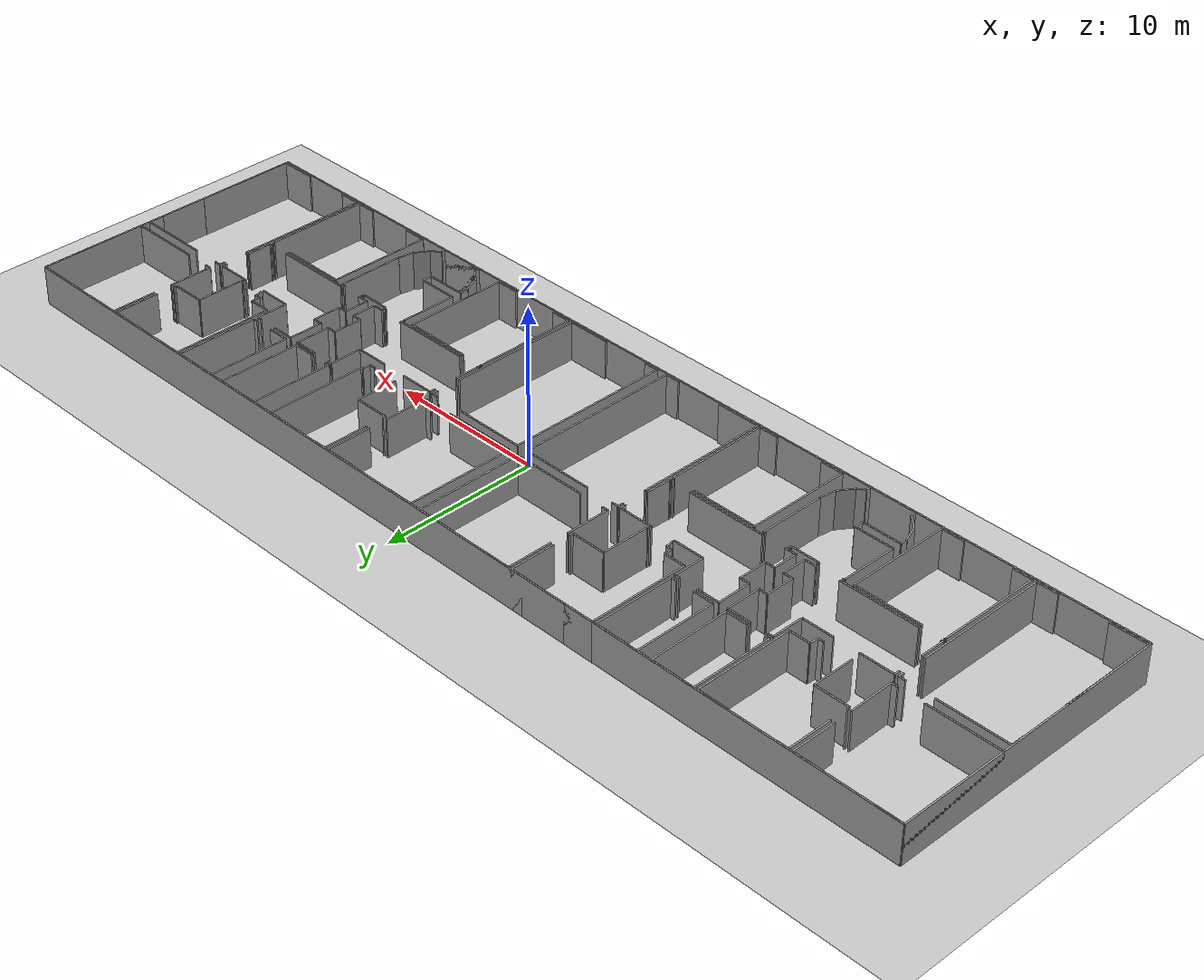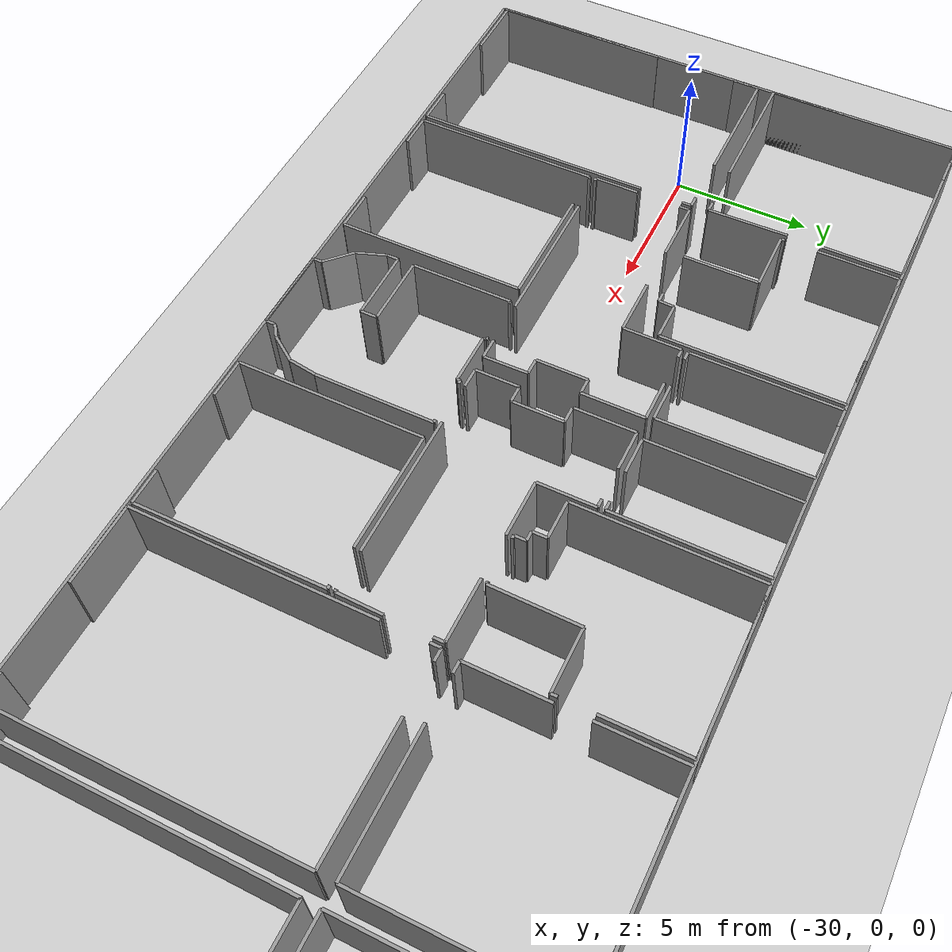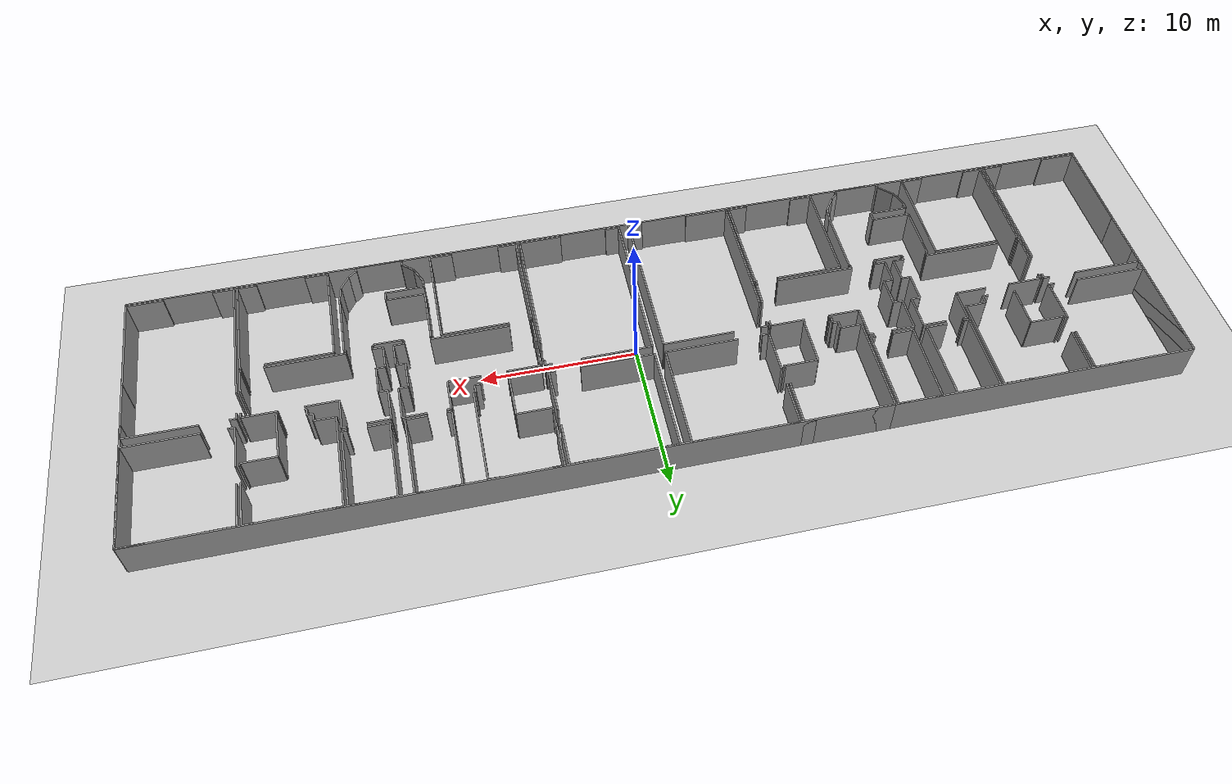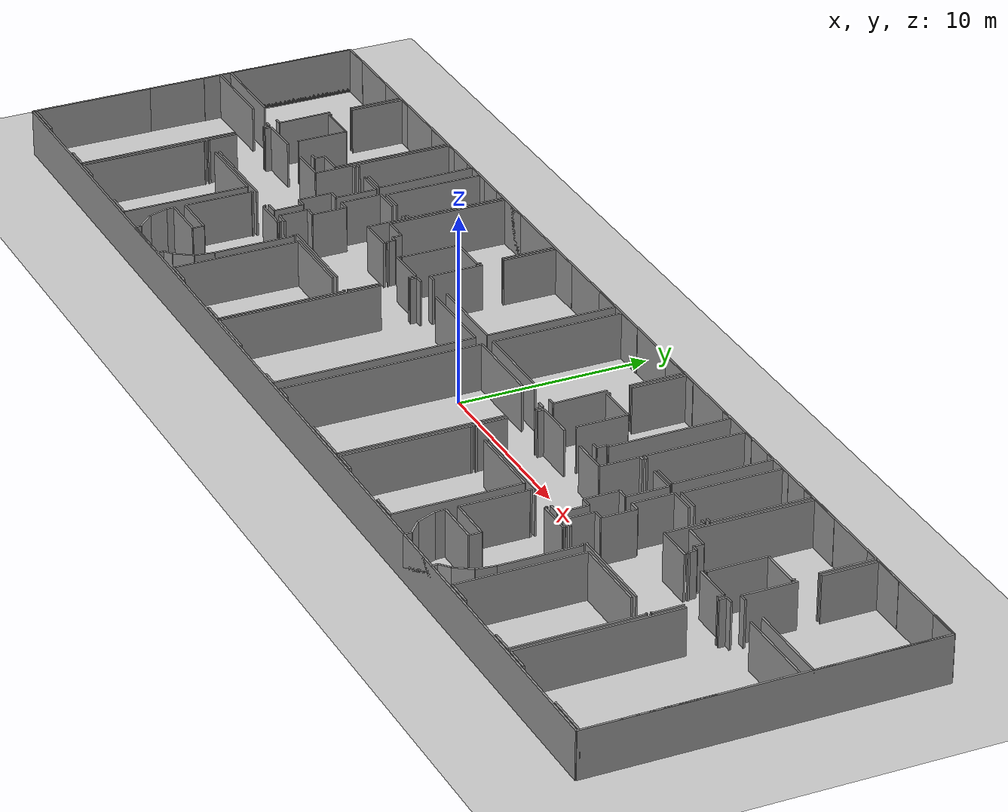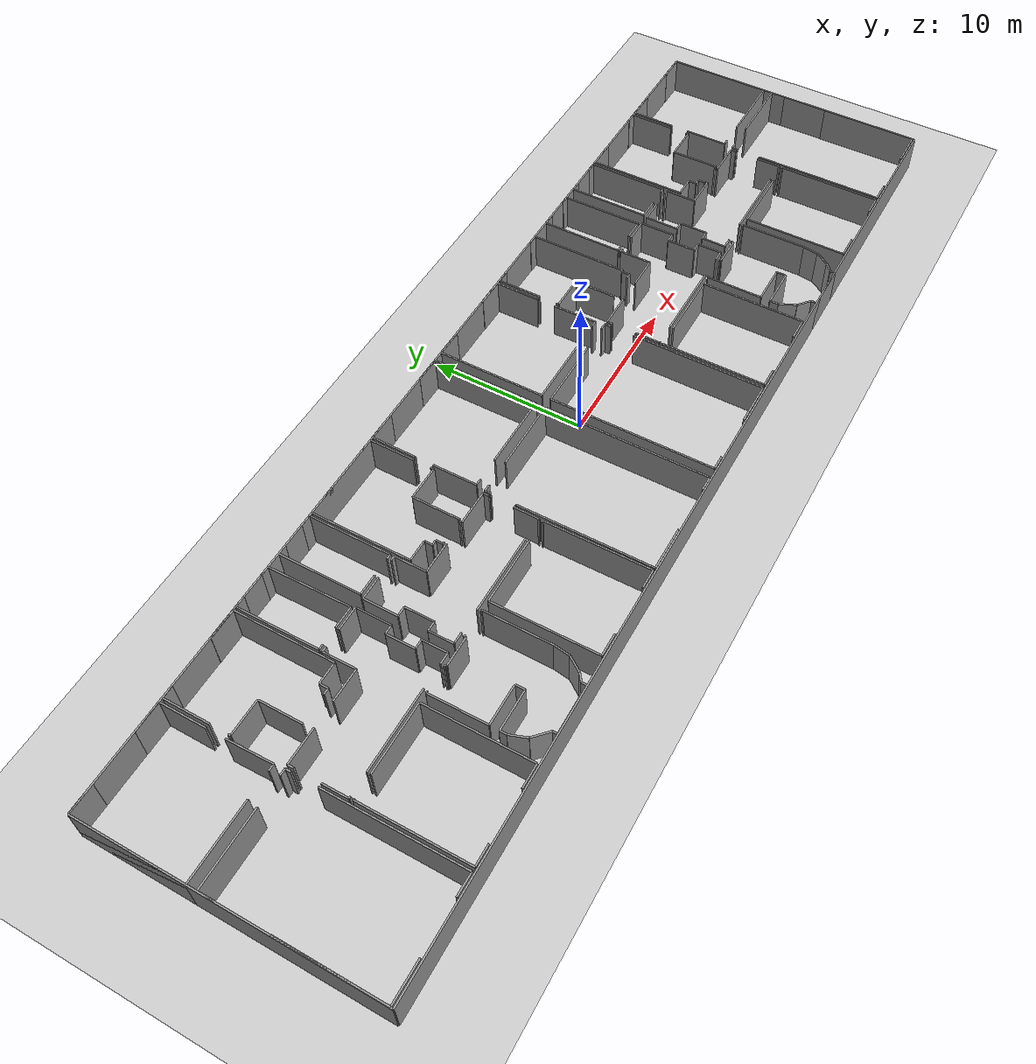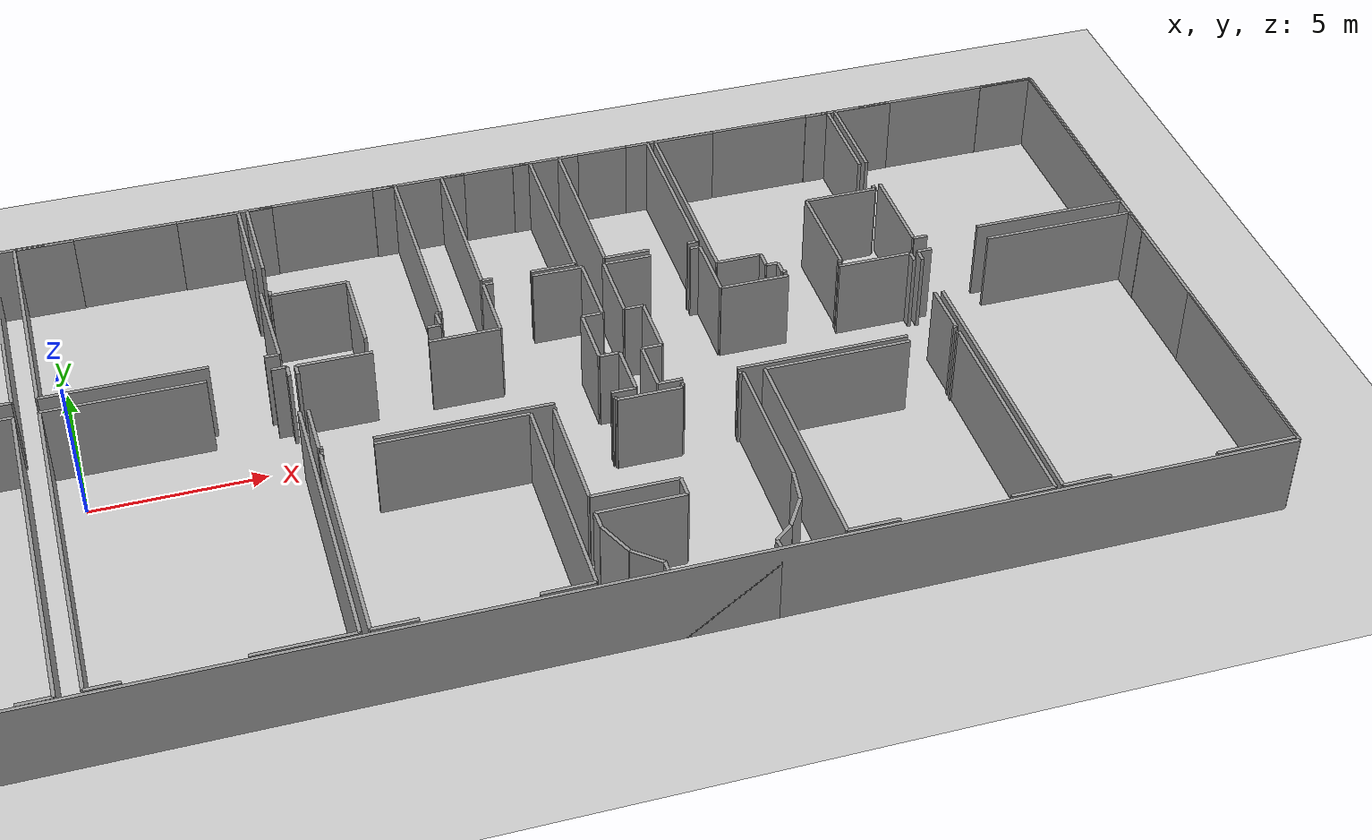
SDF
<sdf version="1.6">
  <world name="default">
    <light name="sun" type="directional">
      <cast_shadows>1</cast_shadows>
      <pose frame="">0 0 10 0 -0 0</pose>
      <diffuse>0.8 0.8 0.8 1</diffuse>
      <specular>0.1 0.1 0.1 1</specular>
      <attenuation>
        <range>1000</range>
        <constant>0.9</constant>
        <linear>0.01</linear>
        <quadratic>0.001</quadratic>
      </attenuation>
      <direction>-0.5 0.5 -1</direction>
    </light>
    <model name="ground_plane">
      <static>1</static>
      <link name="link">
        <collision name="collision">
          <geometry>
            <plane>
              <normal>0 0 1</normal>
              <size>100 100</size>
            </plane>
          </geometry>
          <surface>
            <friction>
              <ode>
                <mu>100</mu>
                <mu2>50</mu2>
              </ode>
              <torsional>
                <ode />
              </torsional>
            </friction>
            <contact>
              <ode />
            </contact>
            <bounce />
          </surface>
          <max_contacts>10</max_contacts>
        </collision>
        <visual name="visual">
          <cast_shadows>0</cast_shadows>
          <geometry>
            <plane>
              <normal>0 0 1</normal>
              <size>100 100</size>
            </plane>
          </geometry>
          <material>
            <script>
              <uri>file://media/materials/scripts/gazebo.material</uri>
              <name>Gazebo/Grey</name>
            </script>
          </material>
        </visual>
        <self_collide>0</self_collide>
        <kinematic>0</kinematic>
        <gravity>1</gravity>
      </link>
    </model>
    <gravity>0 0 -9.8</gravity>
    <magnetic_field>6e-06 2.3e-05 -4.2e-05</magnetic_field>
    <atmosphere type="adiabatic" />
    <physics default="0" name="default_physics" type="ode">
      <max_step_size>0.001</max_step_size>
      <real_time_factor>1</real_time_factor>
      <real_time_update_rate>1000</real_time_update_rate>
    </physics>
    <scene>
      <ambient>0.4 0.4 0.4 1</ambient>
      <background>0.7 0.7 0.7 1</background>
      <shadows>1</shadows>
    </scene>
    <spherical_coordinates>
      <surface_model>EARTH_WGS84</surface_model>
      <latitude_deg>0</latitude_deg>
      <longitude_deg>0</longitude_deg>
      <elevation>0</elevation>
      <heading_deg>0</heading_deg>
    </spherical_coordinates>
  <model name="0510034840_A-40">
		<static>1</static>
		<link name="Wall_0">
			<collision name="Wall_0_Collision">
				<geometry>
					<box>
						<size>0.408471532022 0.1 2.5</size>
					</box>
				</geometry>
				<pose frame="">0.204235766011 0 1.25 0 0 0</pose>
			</collision>
			<visual name="Wall_0_Visual">
				<pose frame="">0.204235766011 0 1.25 0 0 0</pose>
				<geometry>
					<box>
						<size>0.408471532022 0.1 2.5</size>
					</box>
				</geometry>
				<material>
					<script>
						<uri>file://media/materials/scripts/gazebo.material</uri>
						<name>Gazebo/Grey</name>
					</script>
					<ambient>1 1 1 1</ambient>
				</material>
			</visual>
			<pose frame="">6.66679360002 -6.94261977749 0 0 0 3.14159265359</pose>
		</link>
		<link name="Wall_1">
			<collision name="Wall_1_Collision">
				<geometry>
					<box>
						<size>4.6469031435 0.1 2.5</size>
					</box>
				</geometry>
				<pose frame="">2.32345157175 0 1.25 0 0 0</pose>
			</collision>
			<visual name="Wall_1_Visual">
				<pose frame="">2.32345157175 0 1.25 0 0 0</pose>
				<geometry>
					<box>
						<size>4.6469031435 0.1 2.5</size>
					</box>
				</geometry>
				<material>
					<script>
						<uri>file://media/materials/scripts/gazebo.material</uri>
						<name>Gazebo/Grey</name>
					</script>
					<ambient>1 1 1 1</ambient>
				</material>
			</visual>
			<pose frame="">4.6469031435 -6.94261977749 0 0 0 3.14159265359</pose>
		</link>
		<link name="Wall_2">
			<collision name="Wall_2_Collision">
				<geometry>
					<box>
						<size>6.9379232434 0.1 2.5</size>
					</box>
				</geometry>
				<pose frame="">3.4689616217 0 1.25 0 0 0</pose>
			</collision>
			<visual name="Wall_2_Visual">
				<pose frame="">3.4689616217 0 1.25 0 0 0</pose>
				<geometry>
					<box>
						<size>6.9379232434 0.1 2.5</size>
					</box>
				</geometry>
				<material>
					<script>
						<uri>file://media/materials/scripts/gazebo.material</uri>
						<name>Gazebo/Grey</name>
					</script>
					<ambient>1 1 1 1</ambient>
				</material>
			</visual>
			<pose frame="">0.0 -6.94261977749 0 0 0 1.57079632679</pose>
		</link>
		<link name="Wall_3">
			<collision name="Wall_3_Collision">
				<geometry>
					<box>
						<size>1.70877680674 0.1 2.5</size>
					</box>
				</geometry>
				<pose frame="">0.854388403369 0 1.25 0 0 0</pose>
			</collision>
			<visual name="Wall_3_Visual">
				<pose frame="">0.854388403369 0 1.25 0 0 0</pose>
				<geometry>
					<box>
						<size>1.70877680674 0.1 2.5</size>
					</box>
				</geometry>
				<material>
					<script>
						<uri>file://media/materials/scripts/gazebo.material</uri>
						<name>Gazebo/Grey</name>
					</script>
					<ambient>1 1 1 1</ambient>
				</material>
			</visual>
			<pose frame="">0.0 -0.00469653408478 0 0 0 0.0</pose>
		</link>
		<link name="Wall_4">
			<collision name="Wall_4_Collision">
				<geometry>
					<box>
						<size>1.85487709678 0.1 2.5</size>
					</box>
				</geometry>
				<pose frame="">0.92743854839 0 1.25 0 0 0</pose>
			</collision>
			<visual name="Wall_4_Visual">
				<pose frame="">0.92743854839 0 1.25 0 0 0</pose>
				<geometry>
					<box>
						<size>1.85487709678 0.1 2.5</size>
					</box>
				</geometry>
				<material>
					<script>
						<uri>file://media/materials/scripts/gazebo.material</uri>
						<name>Gazebo/Grey</name>
					</script>
					<ambient>1 1 1 1</ambient>
				</material>
			</visual>
			<pose frame="">4.75441569404 -0.00469653408478 0 0 0 0.0</pose>
		</link>
		<link name="Wall_5">
			<collision name="Wall_5_Collision">
				<geometry>
					<box>
						<size>2.89484206317 0.1 2.5</size>
					</box>
				</geometry>
				<pose frame="">1.44742103159 0 1.25 0 0 0</pose>
			</collision>
			<visual name="Wall_5_Visual">
				<pose frame="">1.44742103159 0 1.25 0 0 0</pose>
				<geometry>
					<box>
						<size>2.89484206317 0.1 2.5</size>
					</box>
				</geometry>
				<material>
					<script>
						<uri>file://media/materials/scripts/gazebo.material</uri>
						<name>Gazebo/Grey</name>
					</script>
					<ambient>1 1 1 1</ambient>
				</material>
			</visual>
			<pose frame="">6.60929279082 -0.00469653408478 0 0 0 -1.57079632679</pose>
		</link>
		<link name="Wall_6">
			<collision name="Wall_6_Collision">
				<geometry>
					<box>
						<size>2.86825475186 0.1 2.5</size>
					</box>
				</geometry>
				<pose frame="">1.43412737593 0 1.25 0 0 0</pose>
			</collision>
			<visual name="Wall_6_Visual">
				<pose frame="">1.43412737593 0 1.25 0 0 0</pose>
				<geometry>
					<box>
						<size>2.86825475186 0.1 2.5</size>
					</box>
				</geometry>
				<material>
					<script>
						<uri>file://media/materials/scripts/gazebo.material</uri>
						<name>Gazebo/Grey</name>
					</script>
					<ambient>1 1 1 1</ambient>
				</material>
			</visual>
			<pose frame="">6.60929279082 -4.07494145199 0 0 0 -1.5507476678</pose>
		</link>
		<link name="Wall_7">
			<collision name="Wall_7_Collision">
				<geometry>
					<box>
						<size>0.373184059709 0.1 2.5</size>
					</box>
				</geometry>
				<pose frame="">0.186592029855 0 1.25 0 0 0</pose>
			</collision>
			<visual name="Wall_7_Visual">
				<pose frame="">0.186592029855 0 1.25 0 0 0</pose>
				<geometry>
					<box>
						<size>0.373184059709 0.1 2.5</size>
					</box>
				</geometry>
				<material>
					<script>
						<uri>file://media/materials/scripts/gazebo.material</uri>
						<name>Gazebo/Grey</name>
					</script>
					<ambient>1 1 1 1</ambient>
				</material>
			</visual>
			<pose frame="">11.2253511294 -6.92053337395 0 0 0 3.14159265359</pose>
		</link>
		<link name="Wall_8">
			<collision name="Wall_8_Collision">
				<geometry>
					<box>
						<size>2.704188166 0.1 2.5</size>
					</box>
				</geometry>
				<pose frame="">1.352094083 0 1.25 0 0 0</pose>
			</collision>
			<visual name="Wall_8_Visual">
				<pose frame="">1.352094083 0 1.25 0 0 0</pose>
				<geometry>
					<box>
						<size>2.704188166 0.1 2.5</size>
					</box>
				</geometry>
				<material>
					<script>
						<uri>file://media/materials/scripts/gazebo.material</uri>
						<name>Gazebo/Grey</name>
					</script>
					<ambient>1 1 1 1</ambient>
				</material>
			</visual>
			<pose frame="">9.05085584814 -6.92053337395 0 0 0 1.57079632679</pose>
		</link>
		<link name="Wall_9">
			<collision name="Wall_9_Collision">
				<geometry>
					<box>
						<size>2.1902350171 0.1 2.5</size>
					</box>
				</geometry>
				<pose frame="">1.09511750855 0 1.25 0 0 0</pose>
			</collision>
			<visual name="Wall_9_Visual">
				<pose frame="">1.09511750855 0 1.25 0 0 0</pose>
				<geometry>
					<box>
						<size>2.1902350171 0.1 2.5</size>
					</box>
				</geometry>
				<material>
					<script>
						<uri>file://media/materials/scripts/gazebo.material</uri>
						<name>Gazebo/Grey</name>
					</script>
					<ambient>1 1 1 1</ambient>
				</material>
			</visual>
			<pose frame="">9.05085584814 -4.21634520795 0 0 0 3.14159265359</pose>
		</link>
		<link name="Wall_10">
			<collision name="Wall_10_Collision">
				<geometry>
					<box>
						<size>0.148385090408 0.1 2.5</size>
					</box>
				</geometry>
				<pose frame="">0.0741925452041 0 1.25 0 0 0</pose>
			</collision>
			<visual name="Wall_10_Visual">
				<pose frame="">0.0741925452041 0 1.25 0 0 0</pose>
				<geometry>
					<box>
						<size>0.148385090408 0.1 2.5</size>
					</box>
				</geometry>
				<material>
					<script>
						<uri>file://media/materials/scripts/gazebo.material</uri>
						<name>Gazebo/Grey</name>
					</script>
					<ambient>1 1 1 1</ambient>
				</material>
			</visual>
			<pose frame="">6.86062083103 -4.21634520795 0 0 0 1.57079632679</pose>
		</link>
		<link name="Wall_11">
			<collision name="Wall_11_Collision">
				<geometry>
					<box>
						<size>2.89573059665 0.1 2.5</size>
					</box>
				</geometry>
				<pose frame="">1.44786529833 0 1.25 0 0 0</pose>
			</collision>
			<visual name="Wall_11_Visual">
				<pose frame="">1.44786529833 0 1.25 0 0 0</pose>
				<geometry>
					<box>
						<size>2.89573059665 0.1 2.5</size>
					</box>
				</geometry>
				<material>
					<script>
						<uri>file://media/materials/scripts/gazebo.material</uri>
						<name>Gazebo/Grey</name>
					</script>
					<ambient>1 1 1 1</ambient>
				</material>
			</visual>
			<pose frame="">6.86062083103 -2.91400899957 0 0 0 1.57079632679</pose>
		</link>
		<link name="Wall_12">
			<collision name="Wall_12_Collision">
				<geometry>
					<box>
						<size>0.747510519602 0.1 2.5</size>
					</box>
				</geometry>
				<pose frame="">0.373755259801 0 1.25 0 0 0</pose>
			</collision>
			<visual name="Wall_12_Visual">
				<pose frame="">0.373755259801 0 1.25 0 0 0</pose>
				<geometry>
					<box>
						<size>0.747510519602 0.1 2.5</size>
					</box>
				</geometry>
				<material>
					<script>
						<uri>file://media/materials/scripts/gazebo.material</uri>
						<name>Gazebo/Grey</name>
					</script>
					<ambient>1 1 1 1</ambient>
				</material>
			</visual>
			<pose frame="">6.86062083103 -0.0182784029245 0 0 0 0.0</pose>
		</link>
		<link name="Wall_13">
			<collision name="Wall_13_Collision">
				<geometry>
					<box>
						<size>1.91072777238 0.1 2.5</size>
					</box>
				</geometry>
				<pose frame="">0.955363886192 0 1.25 0 0 0</pose>
			</collision>
			<visual name="Wall_13_Visual">
				<pose frame="">0.955363886192 0 1.25 0 0 0</pose>
				<geometry>
					<box>
						<size>1.91072777238 0.1 2.5</size>
					</box>
				</geometry>
				<material>
					<script>
						<uri>file://media/materials/scripts/gazebo.material</uri>
						<name>Gazebo/Grey</name>
					</script>
					<ambient>1 1 1 1</ambient>
				</material>
			</visual>
			<pose frame="">10.6707793073 -0.0182784029245 0 0 0 0.0</pose>
		</link>
		<link name="Wall_14">
			<collision name="Wall_14_Collision">
				<geometry>
					<box>
						<size>6.35098341616 0.1 2.5</size>
					</box>
				</geometry>
				<pose frame="">3.17549170808 0 1.25 0 0 0</pose>
			</collision>
			<visual name="Wall_14_Visual">
				<pose frame="">3.17549170808 0 1.25 0 0 0</pose>
				<geometry>
					<box>
						<size>6.35098341616 0.1 2.5</size>
					</box>
				</geometry>
				<material>
					<script>
						<uri>file://media/materials/scripts/gazebo.material</uri>
						<name>Gazebo/Grey</name>
					</script>
					<ambient>1 1 1 1</ambient>
				</material>
			</visual>
			<pose frame="">12.5815070797 -0.0182784029245 0 0 0 -1.57079632679</pose>
		</link>
		<link name="Wall_15">
			<collision name="Wall_15_Collision">
				<geometry>
					<box>
						<size>1.33736981398 0.1 2.5</size>
					</box>
				</geometry>
				<pose frame="">0.66868490699 0 1.25 0 0 0</pose>
			</collision>
			<visual name="Wall_15_Visual">
				<pose frame="">0.66868490699 0 1.25 0 0 0</pose>
				<geometry>
					<box>
						<size>1.33736981398 0.1 2.5</size>
					</box>
				</geometry>
				<material>
					<script>
						<uri>file://media/materials/scripts/gazebo.material</uri>
						<name>Gazebo/Grey</name>
					</script>
					<ambient>1 1 1 1</ambient>
				</material>
			</visual>
			<pose frame="">12.5815070797 -6.36926181908 0 0 0 3.14159265359</pose>
		</link>
		<link name="Wall_16">
			<collision name="Wall_16_Collision">
				<geometry>
					<box>
						<size>0.551591557339 0.1 2.5</size>
					</box>
				</geometry>
				<pose frame="">0.275795778669 0 1.25 0 0 0</pose>
			</collision>
			<visual name="Wall_16_Visual">
				<pose frame="">0.275795778669 0 1.25 0 0 0</pose>
				<geometry>
					<box>
						<size>0.551591557339 0.1 2.5</size>
					</box>
				</geometry>
				<material>
					<script>
						<uri>file://media/materials/scripts/gazebo.material</uri>
						<name>Gazebo/Grey</name>
					</script>
					<ambient>1 1 1 1</ambient>
				</material>
			</visual>
			<pose frame="">11.2441372657 -6.36926181908 0 0 0 -1.60486097086</pose>
		</link>
		<link name="Wall_17">
			<collision name="Wall_17_Collision">
				<geometry>
					<box>
						<size>1.34346261495 0.1 2.5</size>
					</box>
				</geometry>
				<pose frame="">0.671731307477 0 1.25 0 0 0</pose>
			</collision>
			<visual name="Wall_17_Visual">
				<pose frame="">0.671731307477 0 1.25 0 0 0</pose>
				<geometry>
					<box>
						<size>1.34346261495 0.1 2.5</size>
					</box>
				</geometry>
				<material>
					<script>
						<uri>file://media/materials/scripts/gazebo.material</uri>
						<name>Gazebo/Grey</name>
					</script>
					<ambient>1 1 1 1</ambient>
				</material>
			</visual>
			<pose frame="">6.74600001269 -18.0086695481 0 0 0 3.14159265359</pose>
		</link>
		<link name="Wall_18">
			<collision name="Wall_18_Collision">
				<geometry>
					<box>
						<size>2.34293584154 0.1 2.5</size>
					</box>
				</geometry>
				<pose frame="">1.17146792077 0 1.25 0 0 0</pose>
			</collision>
			<visual name="Wall_18_Visual">
				<pose frame="">1.17146792077 0 1.25 0 0 0</pose>
				<geometry>
					<box>
						<size>2.34293584154 0.1 2.5</size>
					</box>
				</geometry>
				<material>
					<script>
						<uri>file://media/materials/scripts/gazebo.material</uri>
						<name>Gazebo/Grey</name>
					</script>
					<ambient>1 1 1 1</ambient>
				</material>
			</visual>
			<pose frame="">2.35981797757 -18.0086695481 0 0 0 3.14159265359</pose>
		</link>
		<link name="Wall_19">
			<collision name="Wall_19_Collision">
				<geometry>
					<box>
						<size>6.40746875853 0.1 2.5</size>
					</box>
				</geometry>
				<pose frame="">3.20373437926 0 1.25 0 0 0</pose>
			</collision>
			<visual name="Wall_19_Visual">
				<pose frame="">3.20373437926 0 1.25 0 0 0</pose>
				<geometry>
					<box>
						<size>6.40746875853 0.1 2.5</size>
					</box>
				</geometry>
				<material>
					<script>
						<uri>file://media/materials/scripts/gazebo.material</uri>
						<name>Gazebo/Grey</name>
					</script>
					<ambient>1 1 1 1</ambient>
				</material>
			</visual>
			<pose frame="">0.0168821360345 -18.0086695481 0 0 0 1.57079632679</pose>
		</link>
		<link name="Wall_20">
			<collision name="Wall_20_Collision">
				<geometry>
					<box>
						<size>0.957966019941 0.1 2.5</size>
					</box>
				</geometry>
				<pose frame="">0.478983009971 0 1.25 0 0 0</pose>
			</collision>
			<visual name="Wall_20_Visual">
				<pose frame="">0.478983009971 0 1.25 0 0 0</pose>
				<geometry>
					<box>
						<size>0.957966019941 0.1 2.5</size>
					</box>
				</geometry>
				<material>
					<script>
						<uri>file://media/materials/scripts/gazebo.material</uri>
						<name>Gazebo/Grey</name>
					</script>
					<ambient>1 1 1 1</ambient>
				</material>
			</visual>
			<pose frame="">0.0168821360345 -8.51684722936 0 0 0 1.57079632679</pose>
		</link>
		<link name="Wall_21">
			<collision name="Wall_21_Collision">
				<geometry>
					<box>
						<size>4.52136605675 0.1 2.5</size>
					</box>
				</geometry>
				<pose frame="">2.26068302838 0 1.25 0 0 0</pose>
			</collision>
			<visual name="Wall_21_Visual">
				<pose frame="">2.26068302838 0 1.25 0 0 0</pose>
				<geometry>
					<box>
						<size>4.52136605675 0.1 2.5</size>
					</box>
				</geometry>
				<material>
					<script>
						<uri>file://media/materials/scripts/gazebo.material</uri>
						<name>Gazebo/Grey</name>
					</script>
					<ambient>1 1 1 1</ambient>
				</material>
			</visual>
			<pose frame="">0.0168821360345 -7.55888120942 0 0 0 0.0</pose>
		</link>
		<link name="Wall_22">
			<collision name="Wall_22_Collision">
				<geometry>
					<box>
						<size>0.420022467204 0.1 2.5</size>
					</box>
				</geometry>
				<pose frame="">0.210011233602 0 1.25 0 0 0</pose>
			</collision>
			<visual name="Wall_22_Visual">
				<pose frame="">0.210011233602 0 1.25 0 0 0</pose>
				<geometry>
					<box>
						<size>0.420022467204 0.1 2.5</size>
					</box>
				</geometry>
				<material>
					<script>
						<uri>file://media/materials/scripts/gazebo.material</uri>
						<name>Gazebo/Grey</name>
					</script>
					<ambient>1 1 1 1</ambient>
				</material>
			</visual>
			<pose frame="">6.31404581025 -7.55888120942 0 0 0 0.0</pose>
		</link>
		<link name="Wall_23">
			<collision name="Wall_23_Collision">
				<geometry>
					<box>
						<size>0.35300165648 0.1 2.5</size>
					</box>
				</geometry>
				<pose frame="">0.17650082824 0 1.25 0 0 0</pose>
			</collision>
			<visual name="Wall_23_Visual">
				<pose frame="">0.17650082824 0 1.25 0 0 0</pose>
				<geometry>
					<box>
						<size>0.35300165648 0.1 2.5</size>
					</box>
				</geometry>
				<material>
					<script>
						<uri>file://media/materials/scripts/gazebo.material</uri>
						<name>Gazebo/Grey</name>
					</script>
					<ambient>1 1 1 1</ambient>
				</material>
			</visual>
			<pose frame="">6.73406827745 -7.55888120942 0 0 0 -1.57079632679</pose>
		</link>
		<link name="Wall_24">
			<collision name="Wall_24_Collision">
				<geometry>
					<box>
						<size>8.53386464001 0.1 2.5</size>
					</box>
				</geometry>
				<pose frame="">4.26693232001 0 1.25 0 0 0</pose>
			</collision>
			<visual name="Wall_24_Visual">
				<pose frame="">4.26693232001 0 1.25 0 0 0</pose>
				<geometry>
					<box>
						<size>8.53386464001 0.1 2.5</size>
					</box>
				</geometry>
				<material>
					<script>
						<uri>file://media/materials/scripts/gazebo.material</uri>
						<name>Gazebo/Grey</name>
					</script>
					<ambient>1 1 1 1</ambient>
				</material>
			</visual>
			<pose frame="">6.73406827745 -9.4748132493 0 0 0 -1.56939816317</pose>
		</link>
		<link name="Wall_25">
			<collision name="Wall_25_Collision">
				<geometry>
					<box>
						<size>1.45211756567 0.1 2.5</size>
					</box>
				</geometry>
				<pose frame="">0.726058782836 0 1.25 0 0 0</pose>
			</collision>
			<visual name="Wall_25_Visual">
				<pose frame="">0.726058782836 0 1.25 0 0 0</pose>
				<geometry>
					<box>
						<size>1.45211756567 0.1 2.5</size>
					</box>
				</geometry>
				<material>
					<script>
						<uri>file://media/materials/scripts/gazebo.material</uri>
						<name>Gazebo/Grey</name>
					</script>
					<ambient>1 1 1 1</ambient>
				</material>
			</visual>
			<pose frame="">12.754263374 -18.0183164829 0 0 0 3.14159265359</pose>
		</link>
		<link name="Wall_26">
			<collision name="Wall_26_Collision">
				<geometry>
					<box>
						<size>1.2406465985 0.1 2.5</size>
					</box>
				</geometry>
				<pose frame="">0.620323299252 0 1.25 0 0 0</pose>
			</collision>
			<visual name="Wall_26_Visual">
				<pose frame="">0.620323299252 0 1.25 0 0 0</pose>
				<geometry>
					<box>
						<size>1.2406465985 0.1 2.5</size>
					</box>
				</geometry>
				<material>
					<script>
						<uri>file://media/materials/scripts/gazebo.material</uri>
						<name>Gazebo/Grey</name>
					</script>
					<ambient>1 1 1 1</ambient>
				</material>
			</visual>
			<pose frame="">8.23403971745 -18.0183164829 0 0 0 3.14159265359</pose>
		</link>
		<link name="Wall_27">
			<collision name="Wall_27_Collision">
				<geometry>
					<box>
						<size>6.70487360611 0.1 2.5</size>
					</box>
				</geometry>
				<pose frame="">3.35243680306 0 1.25 0 0 0</pose>
			</collision>
			<visual name="Wall_27_Visual">
				<pose frame="">3.35243680306 0 1.25 0 0 0</pose>
				<geometry>
					<box>
						<size>6.70487360611 0.1 2.5</size>
					</box>
				</geometry>
				<material>
					<script>
						<uri>file://media/materials/scripts/gazebo.material</uri>
						<name>Gazebo/Grey</name>
					</script>
					<ambient>1 1 1 1</ambient>
				</material>
			</visual>
			<pose frame="">6.99339311894 -18.0183164829 0 0 0 1.57079632679</pose>
		</link>
		<link name="Wall_28">
			<collision name="Wall_28_Collision">
				<geometry>
					<box>
						<size>0.0878378807207 0.1 2.5</size>
					</box>
				</geometry>
				<pose frame="">0.0439189403604 0 1.25 0 0 0</pose>
			</collision>
			<visual name="Wall_28_Visual">
				<pose frame="">0.0439189403604 0 1.25 0 0 0</pose>
				<geometry>
					<box>
						<size>0.0878378807207 0.1 2.5</size>
					</box>
				</geometry>
				<material>
					<script>
						<uri>file://media/materials/scripts/gazebo.material</uri>
						<name>Gazebo/Grey</name>
					</script>
					<ambient>1 1 1 1</ambient>
				</material>
			</visual>
			<pose frame="">6.99339311894 -11.3134428768 0 0 0 0.0</pose>
		</link>
		<link name="Wall_29">
			<collision name="Wall_29_Collision">
				<geometry>
					<box>
						<size>4.3191612244 0.1 2.5</size>
					</box>
				</geometry>
				<pose frame="">2.1595806122 0 1.25 0 0 0</pose>
			</collision>
			<visual name="Wall_29_Visual">
				<pose frame="">2.1595806122 0 1.25 0 0 0</pose>
				<geometry>
					<box>
						<size>4.3191612244 0.1 2.5</size>
					</box>
				</geometry>
				<material>
					<script>
						<uri>file://media/materials/scripts/gazebo.material</uri>
						<name>Gazebo/Grey</name>
					</script>
					<ambient>1 1 1 1</ambient>
				</material>
			</visual>
			<pose frame="">8.44474908449 -11.3134428768 0 0 0 0.0</pose>
		</link>
		<link name="Wall_30">
			<collision name="Wall_30_Collision">
				<geometry>
					<box>
						<size>6.70488054609 0.1 2.5</size>
					</box>
				</geometry>
				<pose frame="">3.35244027304 0 1.25 0 0 0</pose>
			</collision>
			<visual name="Wall_30_Visual">
				<pose frame="">3.35244027304 0 1.25 0 0 0</pose>
				<geometry>
					<box>
						<size>6.70488054609 0.1 2.5</size>
					</box>
				</geometry>
				<material>
					<script>
						<uri>file://media/materials/scripts/gazebo.material</uri>
						<name>Gazebo/Grey</name>
					</script>
					<ambient>1 1 1 1</ambient>
				</material>
			</visual>
			<pose frame="">12.7639103089 -11.3134428768 0 0 0 -1.57223512024</pose>
		</link>
		<link name="Wall_31">
			<collision name="Wall_31_Collision">
				<geometry>
					<box>
						<size>0.741671585334 0.1 2.5</size>
					</box>
				</geometry>
				<pose frame="">0.370835792667 0 1.25 0 0 0</pose>
			</collision>
			<visual name="Wall_31_Visual">
				<pose frame="">0.370835792667 0 1.25 0 0 0</pose>
				<geometry>
					<box>
						<size>0.741671585334 0.1 2.5</size>
					</box>
				</geometry>
				<material>
					<script>
						<uri>file://media/materials/scripts/gazebo.material</uri>
						<name>Gazebo/Grey</name>
					</script>
					<ambient>1 1 1 1</ambient>
				</material>
			</visual>
			<pose frame="">15.8059950623 -11.0928327082 0 0 0 3.14159265359</pose>
		</link>
		<link name="Wall_32">
			<collision name="Wall_32_Collision">
				<geometry>
					<box>
						<size>5.05715174248 0.1 2.5</size>
					</box>
				</geometry>
				<pose frame="">2.52857587124 0 1.25 0 0 0</pose>
			</collision>
			<visual name="Wall_32_Visual">
				<pose frame="">2.52857587124 0 1.25 0 0 0</pose>
				<geometry>
					<box>
						<size>5.05715174248 0.1 2.5</size>
					</box>
				</geometry>
				<material>
					<script>
						<uri>file://media/materials/scripts/gazebo.material</uri>
						<name>Gazebo/Grey</name>
					</script>
					<ambient>1 1 1 1</ambient>
				</material>
			</visual>
			<pose frame="">13.5057088276 -11.0928327082 0 0 0 3.14159265359</pose>
		</link>
		<link name="Wall_33">
			<collision name="Wall_33_Collision">
				<geometry>
					<box>
						<size>0.126933353643 0.1 2.5</size>
					</box>
				</geometry>
				<pose frame="">0.0634666768213 0 1.25 0 0 0</pose>
			</collision>
			<visual name="Wall_33_Visual">
				<pose frame="">0.0634666768213 0 1.25 0 0 0</pose>
				<geometry>
					<box>
						<size>0.126933353643 0.1 2.5</size>
					</box>
				</geometry>
				<material>
					<script>
						<uri>file://media/materials/scripts/gazebo.material</uri>
						<name>Gazebo/Grey</name>
					</script>
					<ambient>1 1 1 1</ambient>
				</material>
			</visual>
			<pose frame="">7.08288113326 -11.0928327082 0 0 0 3.14159265359</pose>
		</link>
		<link name="Wall_34">
			<collision name="Wall_34_Collision">
				<geometry>
					<box>
						<size>1.58831705413 0.1 2.5</size>
					</box>
				</geometry>
				<pose frame="">0.794158527065 0 1.25 0 0 0</pose>
			</collision>
			<visual name="Wall_34_Visual">
				<pose frame="">0.794158527065 0 1.25 0 0 0</pose>
				<geometry>
					<box>
						<size>1.58831705413 0.1 2.5</size>
					</box>
				</geometry>
				<material>
					<script>
						<uri>file://media/materials/scripts/gazebo.material</uri>
						<name>Gazebo/Grey</name>
					</script>
					<ambient>1 1 1 1</ambient>
				</material>
			</visual>
			<pose frame="">6.95594777962 -11.0928327082 0 0 0 1.57079632679</pose>
		</link>
		<link name="Wall_35">
			<collision name="Wall_35_Collision">
				<geometry>
					<box>
						<size>0.374326459892 0.1 2.5</size>
					</box>
				</geometry>
				<pose frame="">0.187163229946 0 1.25 0 0 0</pose>
			</collision>
			<visual name="Wall_35_Visual">
				<pose frame="">0.187163229946 0 1.25 0 0 0</pose>
				<geometry>
					<box>
						<size>0.374326459892 0.1 2.5</size>
					</box>
				</geometry>
				<material>
					<script>
						<uri>file://media/materials/scripts/gazebo.material</uri>
						<name>Gazebo/Grey</name>
					</script>
					<ambient>1 1 1 1</ambient>
				</material>
			</visual>
			<pose frame="">6.95594777962 -7.91162899919 0 0 0 1.57079632679</pose>
		</link>
		<link name="Wall_36">
			<collision name="Wall_36_Collision">
				<geometry>
					<box>
						<size>2.19912035186 0.1 2.5</size>
					</box>
				</geometry>
				<pose frame="">1.09956017593 0 1.25 0 0 0</pose>
			</collision>
			<visual name="Wall_36_Visual">
				<pose frame="">1.09956017593 0 1.25 0 0 0</pose>
				<geometry>
					<box>
						<size>2.19912035186 0.1 2.5</size>
					</box>
				</geometry>
				<material>
					<script>
						<uri>file://media/materials/scripts/gazebo.material</uri>
						<name>Gazebo/Grey</name>
					</script>
					<ambient>1 1 1 1</ambient>
				</material>
			</visual>
			<pose frame="">6.95594777962 -7.5373025393 0 0 0 0.0</pose>
		</link>
		<link name="Wall_37">
			<collision name="Wall_37_Collision">
				<geometry>
					<box>
						<size>2.02674485761 0.1 2.5</size>
					</box>
				</geometry>
				<pose frame="">1.01337242881 0 1.25 0 0 0</pose>
			</collision>
			<visual name="Wall_37_Visual">
				<pose frame="">1.01337242881 0 1.25 0 0 0</pose>
				<geometry>
					<box>
						<size>2.02674485761 0.1 2.5</size>
					</box>
				</geometry>
				<material>
					<script>
						<uri>file://media/materials/scripts/gazebo.material</uri>
						<name>Gazebo/Grey</name>
					</script>
					<ambient>1 1 1 1</ambient>
				</material>
			</visual>
			<pose frame="">10.7617905219 -7.5373025393 0 0 0 0.0</pose>
		</link>
		<link name="Wall_38">
			<collision name="Wall_38_Collision">
				<geometry>
					<box>
						<size>2.06863286431 0.1 2.5</size>
					</box>
				</geometry>
				<pose frame="">1.03431643216 0 1.25 0 0 0</pose>
			</collision>
			<visual name="Wall_38_Visual">
				<pose frame="">1.03431643216 0 1.25 0 0 0</pose>
				<geometry>
					<box>
						<size>2.06863286431 0.1 2.5</size>
					</box>
				</geometry>
				<material>
					<script>
						<uri>file://media/materials/scripts/gazebo.material</uri>
						<name>Gazebo/Grey</name>
					</script>
					<ambient>1 1 1 1</ambient>
				</material>
			</visual>
			<pose frame="">12.7885353795 -7.5373025393 0 0 0 1.57079632679</pose>
		</link>
		<link name="Wall_39">
			<collision name="Wall_39_Collision">
				<geometry>
					<box>
						<size>0.33383472008 0.1 2.5</size>
					</box>
				</geometry>
				<pose frame="">0.16691736004 0 1.25 0 0 0</pose>
			</collision>
			<visual name="Wall_39_Visual">
				<pose frame="">0.16691736004 0 1.25 0 0 0</pose>
				<geometry>
					<box>
						<size>0.33383472008 0.1 2.5</size>
					</box>
				</geometry>
				<material>
					<script>
						<uri>file://media/materials/scripts/gazebo.material</uri>
						<name>Gazebo/Grey</name>
					</script>
					<ambient>1 1 1 1</ambient>
				</material>
			</visual>
			<pose frame="">12.7885353795 -5.46866967499 0 0 0 0.0</pose>
		</link>
		<link name="Wall_40">
			<collision name="Wall_40_Collision">
				<geometry>
					<box>
						<size>1.50225624036 0.1 2.5</size>
					</box>
				</geometry>
				<pose frame="">0.75112812018 0 1.25 0 0 0</pose>
			</collision>
			<visual name="Wall_40_Visual">
				<pose frame="">0.75112812018 0 1.25 0 0 0</pose>
				<geometry>
					<box>
						<size>1.50225624036 0.1 2.5</size>
					</box>
				</geometry>
				<material>
					<script>
						<uri>file://media/materials/scripts/gazebo.material</uri>
						<name>Gazebo/Grey</name>
					</script>
					<ambient>1 1 1 1</ambient>
				</material>
			</visual>
			<pose frame="">14.2657857492 -5.46866967499 0 0 0 0.0</pose>
		</link>
		<link name="Wall_41">
			<collision name="Wall_41_Collision">
				<geometry>
					<box>
						<size>2.22450702259 0.1 2.5</size>
					</box>
				</geometry>
				<pose frame="">1.11225351129 0 1.25 0 0 0</pose>
			</collision>
			<visual name="Wall_41_Visual">
				<pose frame="">1.11225351129 0 1.25 0 0 0</pose>
				<geometry>
					<box>
						<size>2.22450702259 0.1 2.5</size>
					</box>
				</geometry>
				<material>
					<script>
						<uri>file://media/materials/scripts/gazebo.material</uri>
						<name>Gazebo/Grey</name>
					</script>
					<ambient>1 1 1 1</ambient>
				</material>
			</visual>
			<pose frame="">15.7680419896 -5.46866967499 0 0 0 -1.57079632679</pose>
		</link>
		<link name="Wall_42">
			<collision name="Wall_42_Collision">
				<geometry>
					<box>
						<size>0.569169157734 0.1 2.5</size>
					</box>
				</geometry>
				<pose frame="">0.284584578867 0 1.25 0 0 0</pose>
			</collision>
			<visual name="Wall_42_Visual">
				<pose frame="">0.284584578867 0 1.25 0 0 0</pose>
				<geometry>
					<box>
						<size>0.569169157734 0.1 2.5</size>
					</box>
				</geometry>
				<material>
					<script>
						<uri>file://media/materials/scripts/gazebo.material</uri>
						<name>Gazebo/Grey</name>
					</script>
					<ambient>1 1 1 1</ambient>
				</material>
			</visual>
			<pose frame="">15.7680419896 -7.69317669757 0 0 0 3.14159265359</pose>
		</link>
		<link name="Wall_43">
			<collision name="Wall_43_Collision">
				<geometry>
					<box>
						<size>1.82123975807 0.1 2.5</size>
					</box>
				</geometry>
				<pose frame="">0.910619879033 0 1.25 0 0 0</pose>
			</collision>
			<visual name="Wall_43_Visual">
				<pose frame="">0.910619879033 0 1.25 0 0 0</pose>
				<geometry>
					<box>
						<size>1.82123975807 0.1 2.5</size>
					</box>
				</geometry>
				<material>
					<script>
						<uri>file://media/materials/scripts/gazebo.material</uri>
						<name>Gazebo/Grey</name>
					</script>
					<ambient>1 1 1 1</ambient>
				</material>
			</visual>
			<pose frame="">15.1988728318 -7.69317669757 0 0 0 -1.57079632679</pose>
		</link>
		<link name="Wall_44">
			<collision name="Wall_44_Collision">
				<geometry>
					<box>
						<size>0.585035826939 0.1 2.5</size>
					</box>
				</geometry>
				<pose frame="">0.29251791347 0 1.25 0 0 0</pose>
			</collision>
			<visual name="Wall_44_Visual">
				<pose frame="">0.29251791347 0 1.25 0 0 0</pose>
				<geometry>
					<box>
						<size>0.585035826939 0.1 2.5</size>
					</box>
				</geometry>
				<material>
					<script>
						<uri>file://media/materials/scripts/gazebo.material</uri>
						<name>Gazebo/Grey</name>
					</script>
					<ambient>1 1 1 1</ambient>
				</material>
			</visual>
			<pose frame="">15.1988728318 -9.51441645564 0 0 0 0.0</pose>
		</link>
		<link name="Wall_45">
			<collision name="Wall_45_Collision">
				<geometry>
					<box>
						<size>1.57857076988 0.1 2.5</size>
					</box>
				</geometry>
				<pose frame="">0.789285384941 0 1.25 0 0 0</pose>
			</collision>
			<visual name="Wall_45_Visual">
				<pose frame="">0.789285384941 0 1.25 0 0 0</pose>
				<geometry>
					<box>
						<size>1.57857076988 0.1 2.5</size>
					</box>
				</geometry>
				<material>
					<script>
						<uri>file://media/materials/scripts/gazebo.material</uri>
						<name>Gazebo/Grey</name>
					</script>
					<ambient>1 1 1 1</ambient>
				</material>
			</visual>
			<pose frame="">15.7839086588 -9.51441645564 0 0 0 -1.55680447757</pose>
		</link>
		<link name="Wall_46">
			<collision name="Wall_46_Collision">
				<geometry>
					<box>
						<size>1.38535062166 0.1 2.5</size>
					</box>
				</geometry>
				<pose frame="">0.692675310828 0 1.25 0 0 0</pose>
			</collision>
			<visual name="Wall_46_Visual">
				<pose frame="">0.692675310828 0 1.25 0 0 0</pose>
				<geometry>
					<box>
						<size>1.38535062166 0.1 2.5</size>
					</box>
				</geometry>
				<material>
					<script>
						<uri>file://media/materials/scripts/gazebo.material</uri>
						<name>Gazebo/Grey</name>
					</script>
					<ambient>1 1 1 1</ambient>
				</material>
			</visual>
			<pose frame="">15.6595139722 -5.25174057361 0 0 0 3.14159265359</pose>
		</link>
		<link name="Wall_47">
			<collision name="Wall_47_Collision">
				<geometry>
					<box>
						<size>0.326345652215 0.1 2.5</size>
					</box>
				</geometry>
				<pose frame="">0.163172826108 0 1.25 0 0 0</pose>
			</collision>
			<visual name="Wall_47_Visual">
				<pose frame="">0.163172826108 0 1.25 0 0 0</pose>
				<geometry>
					<box>
						<size>0.326345652215 0.1 2.5</size>
					</box>
				</geometry>
				<material>
					<script>
						<uri>file://media/materials/scripts/gazebo.material</uri>
						<name>Gazebo/Grey</name>
					</script>
					<ambient>1 1 1 1</ambient>
				</material>
			</visual>
			<pose frame="">13.1285898339 -5.25174057361 0 0 0 3.14159265359</pose>
		</link>
		<link name="Wall_48">
			<collision name="Wall_48_Collision">
				<geometry>
					<box>
						<size>5.247932573 0.1 2.5</size>
					</box>
				</geometry>
				<pose frame="">2.6239662865 0 1.25 0 0 0</pose>
			</collision>
			<visual name="Wall_48_Visual">
				<pose frame="">2.6239662865 0 1.25 0 0 0</pose>
				<geometry>
					<box>
						<size>5.247932573 0.1 2.5</size>
					</box>
				</geometry>
				<material>
					<script>
						<uri>file://media/materials/scripts/gazebo.material</uri>
						<name>Gazebo/Grey</name>
					</script>
					<ambient>1 1 1 1</ambient>
				</material>
			</visual>
			<pose frame="">12.8022441817 -5.25174057361 0 0 0 1.57079632679</pose>
		</link>
		<link name="Wall_49">
			<collision name="Wall_49_Collision">
				<geometry>
					<box>
						<size>0.677189441684 0.1 2.5</size>
					</box>
				</geometry>
				<pose frame="">0.338594720842 0 1.25 0 0 0</pose>
			</collision>
			<visual name="Wall_49_Visual">
				<pose frame="">0.338594720842 0 1.25 0 0 0</pose>
				<geometry>
					<box>
						<size>0.677189441684 0.1 2.5</size>
					</box>
				</geometry>
				<material>
					<script>
						<uri>file://media/materials/scripts/gazebo.material</uri>
						<name>Gazebo/Grey</name>
					</script>
					<ambient>1 1 1 1</ambient>
				</material>
			</visual>
			<pose frame="">12.8022441817 -0.00380800060928 0 0 0 0.0</pose>
		</link>
		<link name="Wall_50">
			<collision name="Wall_50_Collision">
				<geometry>
					<box>
						<size>0.577419825721 0.1 2.5</size>
					</box>
				</geometry>
				<pose frame="">0.28870991286 0 1.25 0 0 0</pose>
			</collision>
			<visual name="Wall_50_Visual">
				<pose frame="">0.28870991286 0 1.25 0 0 0</pose>
				<geometry>
					<box>
						<size>0.577419825721 0.1 2.5</size>
					</box>
				</geometry>
				<material>
					<script>
						<uri>file://media/materials/scripts/gazebo.material</uri>
						<name>Gazebo/Grey</name>
					</script>
					<ambient>1 1 1 1</ambient>
				</material>
			</visual>
			<pose frame="">15.010122935 -0.00380800060928 0 0 0 0.0</pose>
		</link>
		<link name="Wall_51">
			<collision name="Wall_51_Collision">
				<geometry>
					<box>
						<size>5.24842606369 0.1 2.5</size>
					</box>
				</geometry>
				<pose frame="">2.62421303185 0 1.25 0 0 0</pose>
			</collision>
			<visual name="Wall_51_Visual">
				<pose frame="">2.62421303185 0 1.25 0 0 0</pose>
				<geometry>
					<box>
						<size>5.24842606369 0.1 2.5</size>
					</box>
				</geometry>
				<material>
					<script>
						<uri>file://media/materials/scripts/gazebo.material</uri>
						<name>Gazebo/Grey</name>
					</script>
					<ambient>1 1 1 1</ambient>
				</material>
			</visual>
			<pose frame="">15.5875427607 -0.00380800060928 0 0 0 -1.5570829837</pose>
		</link>
		<link name="Wall_52">
			<collision name="Wall_52_Collision">
				<geometry>
					<box>
						<size>2.99740421292 0.1 2.5</size>
					</box>
				</geometry>
				<pose frame="">1.49870210646 0 1.25 0 0 0</pose>
			</collision>
			<visual name="Wall_52_Visual">
				<pose frame="">1.49870210646 0 1.25 0 0 0</pose>
				<geometry>
					<box>
						<size>2.99740421292 0.1 2.5</size>
					</box>
				</geometry>
				<material>
					<script>
						<uri>file://media/materials/scripts/gazebo.material</uri>
						<name>Gazebo/Grey</name>
					</script>
					<ambient>1 1 1 1</ambient>
				</material>
			</visual>
			<pose frame="">17.5726534783 -18.1401725024 0 0 0 3.14159265359</pose>
		</link>
		<link name="Wall_53">
			<collision name="Wall_53_Collision">
				<geometry>
					<box>
						<size>0.304766982096 0.1 2.5</size>
					</box>
				</geometry>
				<pose frame="">0.152383491048 0 1.25 0 0 0</pose>
			</collision>
			<visual name="Wall_53_Visual">
				<pose frame="">0.152383491048 0 1.25 0 0 0</pose>
				<geometry>
					<box>
						<size>0.304766982096 0.1 2.5</size>
					</box>
				</geometry>
				<material>
					<script>
						<uri>file://media/materials/scripts/gazebo.material</uri>
						<name>Gazebo/Grey</name>
					</script>
					<ambient>1 1 1 1</ambient>
				</material>
			</visual>
			<pose frame="">14.5752492654 -18.1401725024 0 0 0 1.57079632679</pose>
		</link>
		<link name="Wall_54">
			<collision name="Wall_54_Collision">
				<geometry>
					<box>
						<size>1.1804613671 0.1 2.5</size>
					</box>
				</geometry>
				<pose frame="">0.590230683552 0 1.25 0 0 0</pose>
			</collision>
			<visual name="Wall_54_Visual">
				<pose frame="">0.590230683552 0 1.25 0 0 0</pose>
				<geometry>
					<box>
						<size>1.1804613671 0.1 2.5</size>
					</box>
				</geometry>
				<material>
					<script>
						<uri>file://media/materials/scripts/gazebo.material</uri>
						<name>Gazebo/Grey</name>
					</script>
					<ambient>1 1 1 1</ambient>
				</material>
			</visual>
			<pose frame="">14.5752492654 -17.8354055203 0 0 0 2.37353115612</pose>
		</link>
		<link name="Wall_55">
			<collision name="Wall_55_Collision">
				<geometry>
					<box>
						<size>1.10183731209 0.1 2.5</size>
					</box>
				</geometry>
				<pose frame="">0.550918656043 0 1.25 0 0 0</pose>
			</collision>
			<visual name="Wall_55_Visual">
				<pose frame="">0.550918656043 0 1.25 0 0 0</pose>
				<geometry>
					<box>
						<size>1.10183731209 0.1 2.5</size>
					</box>
				</geometry>
				<material>
					<script>
						<uri>file://media/materials/scripts/gazebo.material</uri>
						<name>Gazebo/Grey</name>
					</script>
					<ambient>1 1 1 1</ambient>
				</material>
			</visual>
			<pose frame="">13.7261920629 -17.0152891224 0 0 0 1.91338630673</pose>
		</link>
		<link name="Wall_56">
			<collision name="Wall_56_Collision">
				<geometry>
					<box>
						<size>0.420911000679 0.1 2.5</size>
					</box>
				</geometry>
				<pose frame="">0.21045550034 0 1.25 0 0 0</pose>
			</collision>
			<visual name="Wall_56_Visual">
				<pose frame="">0.21045550034 0 1.25 0 0 0</pose>
				<geometry>
					<box>
						<size>0.420911000679 0.1 2.5</size>
					</box>
				</geometry>
				<material>
					<script>
						<uri>file://media/materials/scripts/gazebo.material</uri>
						<name>Gazebo/Grey</name>
					</script>
					<ambient>1 1 1 1</ambient>
				</material>
			</visual>
			<pose frame="">13.3560544036 -15.9774820231 0 0 0 1.57079632679</pose>
		</link>
		<link name="Wall_57">
			<collision name="Wall_57_Collision">
				<geometry>
					<box>
						<size>2.51835773627 0.1 2.5</size>
					</box>
				</geometry>
				<pose frame="">1.25917886814 0 1.25 0 0 0</pose>
			</collision>
			<visual name="Wall_57_Visual">
				<pose frame="">1.25917886814 0 1.25 0 0 0</pose>
				<geometry>
					<box>
						<size>2.51835773627 0.1 2.5</size>
					</box>
				</geometry>
				<material>
					<script>
						<uri>file://media/materials/scripts/gazebo.material</uri>
						<name>Gazebo/Grey</name>
					</script>
					<ambient>1 1 1 1</ambient>
				</material>
			</visual>
			<pose frame="">13.3560544036 -15.5565710224 0 0 0 0.0</pose>
		</link>
		<link name="Wall_58">
			<collision name="Wall_58_Collision">
				<geometry>
					<box>
						<size>0.589097694256 0.1 2.5</size>
					</box>
				</geometry>
				<pose frame="">0.294548847128 0 1.25 0 0 0</pose>
			</collision>
			<visual name="Wall_58_Visual">
				<pose frame="">0.294548847128 0 1.25 0 0 0</pose>
				<geometry>
					<box>
						<size>0.589097694256 0.1 2.5</size>
					</box>
				</geometry>
				<material>
					<script>
						<uri>file://media/materials/scripts/gazebo.material</uri>
						<name>Gazebo/Grey</name>
					</script>
					<ambient>1 1 1 1</ambient>
				</material>
			</visual>
			<pose frame="">15.8744121399 -15.5565710224 0 0 0 1.57079632679</pose>
		</link>
		<link name="Wall_59">
			<collision name="Wall_59_Collision">
				<geometry>
					<box>
						<size>2.50769533456 0.1 2.5</size>
					</box>
				</geometry>
				<pose frame="">1.25384766728 0 1.25 0 0 0</pose>
			</collision>
			<visual name="Wall_59_Visual">
				<pose frame="">1.25384766728 0 1.25 0 0 0</pose>
				<geometry>
					<box>
						<size>2.50769533456 0.1 2.5</size>
					</box>
				</geometry>
				<material>
					<script>
						<uri>file://media/materials/scripts/gazebo.material</uri>
						<name>Gazebo/Grey</name>
					</script>
					<ambient>1 1 1 1</ambient>
				</material>
			</visual>
			<pose frame="">15.8744121399 -14.9674733281 0 0 0 3.14159265359</pose>
		</link>
		<link name="Wall_60">
			<collision name="Wall_60_Collision">
				<geometry>
					<box>
						<size>3.64768378363 0.1 2.5</size>
					</box>
				</geometry>
				<pose frame="">1.82384189181 0 1.25 0 0 0</pose>
			</collision>
			<visual name="Wall_60_Visual">
				<pose frame="">1.82384189181 0 1.25 0 0 0</pose>
				<geometry>
					<box>
						<size>3.64768378363 0.1 2.5</size>
					</box>
				</geometry>
				<material>
					<script>
						<uri>file://media/materials/scripts/gazebo.material</uri>
						<name>Gazebo/Grey</name>
					</script>
					<ambient>1 1 1 1</ambient>
				</material>
			</visual>
			<pose frame="">13.3667168053 -14.9674733281 0 0 0 1.57079632679</pose>
		</link>
		<link name="Wall_61">
			<collision name="Wall_61_Collision">
				<geometry>
					<box>
						<size>0.11360535151 0.1 2.5</size>
					</box>
				</geometry>
				<pose frame="">0.0568026757551 0 1.25 0 0 0</pose>
			</collision>
			<visual name="Wall_61_Visual">
				<pose frame="">0.0568026757551 0 1.25 0 0 0</pose>
				<geometry>
					<box>
						<size>0.11360535151 0.1 2.5</size>
					</box>
				</geometry>
				<material>
					<script>
						<uri>file://media/materials/scripts/gazebo.material</uri>
						<name>Gazebo/Grey</name>
					</script>
					<ambient>1 1 1 1</ambient>
				</material>
			</visual>
			<pose frame="">13.3667168053 -11.3197895445 0 0 0 0.0</pose>
		</link>
		<link name="Wall_62">
			<collision name="Wall_62_Collision">
				<geometry>
					<box>
						<size>0.108781884072 0.1 2.5</size>
					</box>
				</geometry>
				<pose frame="">0.0543909420359 0 1.25 0 0 0</pose>
			</collision>
			<visual name="Wall_62_Visual">
				<pose frame="">0.0543909420359 0 1.25 0 0 0</pose>
				<geometry>
					<box>
						<size>0.108781884072 0.1 2.5</size>
					</box>
				</geometry>
				<material>
					<script>
						<uri>file://media/materials/scripts/gazebo.material</uri>
						<name>Gazebo/Grey</name>
					</script>
					<ambient>1 1 1 1</ambient>
				</material>
			</visual>
			<pose frame="">15.0333517387 -11.3197895445 0 0 0 0.0</pose>
		</link>
		<link name="Wall_63">
			<collision name="Wall_63_Collision">
				<geometry>
					<box>
						<size>0.10802028395 0.1 2.5</size>
					</box>
				</geometry>
				<pose frame="">0.054010141975 0 1.25 0 0 0</pose>
			</collision>
			<visual name="Wall_63_Visual">
				<pose frame="">0.054010141975 0 1.25 0 0 0</pose>
				<geometry>
					<box>
						<size>0.10802028395 0.1 2.5</size>
					</box>
				</geometry>
				<material>
					<script>
						<uri>file://media/materials/scripts/gazebo.material</uri>
						<name>Gazebo/Grey</name>
					</script>
					<ambient>1 1 1 1</ambient>
				</material>
			</visual>
			<pose frame="">15.1421336227 -11.3197895445 0 0 0 -1.57079632679</pose>
		</link>
		<link name="Wall_64">
			<collision name="Wall_64_Collision">
				<geometry>
					<box>
						<size>1.83875656087 0.1 2.5</size>
					</box>
				</geometry>
				<pose frame="">0.919378280434 0 1.25 0 0 0</pose>
			</collision>
			<visual name="Wall_64_Visual">
				<pose frame="">0.919378280434 0 1.25 0 0 0</pose>
				<geometry>
					<box>
						<size>1.83875656087 0.1 2.5</size>
					</box>
				</geometry>
				<material>
					<script>
						<uri>file://media/materials/scripts/gazebo.material</uri>
						<name>Gazebo/Grey</name>
					</script>
					<ambient>1 1 1 1</ambient>
				</material>
			</visual>
			<pose frame="">15.1421336227 -11.4278098284 0 0 0 0.0</pose>
		</link>
		<link name="Wall_65">
			<collision name="Wall_65_Collision">
				<geometry>
					<box>
						<size>0.118428818949 0.1 2.5</size>
					</box>
				</geometry>
				<pose frame="">0.0592144094743 0 1.25 0 0 0</pose>
			</collision>
			<visual name="Wall_65_Visual">
				<pose frame="">0.0592144094743 0 1.25 0 0 0</pose>
				<geometry>
					<box>
						<size>0.118428818949 0.1 2.5</size>
					</box>
				</geometry>
				<material>
					<script>
						<uri>file://media/materials/scripts/gazebo.material</uri>
						<name>Gazebo/Grey</name>
					</script>
					<ambient>1 1 1 1</ambient>
				</material>
			</visual>
			<pose frame="">16.9808901836 -11.4278098284 0 0 0 1.57079632679</pose>
		</link>
		<link name="Wall_66">
			<collision name="Wall_66_Collision">
				<geometry>
					<box>
						<size>0.120840552668 0.1 2.5</size>
					</box>
				</geometry>
				<pose frame="">0.0604202763339 0 1.25 0 0 0</pose>
			</collision>
			<visual name="Wall_66_Visual">
				<pose frame="">0.0604202763339 0 1.25 0 0 0</pose>
				<geometry>
					<box>
						<size>0.120840552668 0.1 2.5</size>
					</box>
				</geometry>
				<material>
					<script>
						<uri>file://media/materials/scripts/gazebo.material</uri>
						<name>Gazebo/Grey</name>
					</script>
					<ambient>1 1 1 1</ambient>
				</material>
			</visual>
			<pose frame="">16.9808901836 -11.3093810095 0 0 0 0.0</pose>
		</link>
		<link name="Wall_67">
			<collision name="Wall_67_Collision">
				<geometry>
					<box>
						<size>0.108781884072 0.1 2.5</size>
					</box>
				</geometry>
				<pose frame="">0.0543909420359 0 1.25 0 0 0</pose>
			</collision>
			<visual name="Wall_67_Visual">
				<pose frame="">0.0543909420359 0 1.25 0 0 0</pose>
				<geometry>
					<box>
						<size>0.108781884072 0.1 2.5</size>
					</box>
				</geometry>
				<material>
					<script>
						<uri>file://media/materials/scripts/gazebo.material</uri>
						<name>Gazebo/Grey</name>
					</script>
					<ambient>1 1 1 1</ambient>
				</material>
			</visual>
			<pose frame="">18.653998718 -11.3093810095 0 0 0 0.0</pose>
		</link>
		<link name="Wall_68">
			<collision name="Wall_68_Collision">
				<geometry>
					<box>
						<size>4.26140654849 0.1 2.5</size>
					</box>
				</geometry>
				<pose frame="">2.13070327425 0 1.25 0 0 0</pose>
			</collision>
			<visual name="Wall_68_Visual">
				<pose frame="">2.13070327425 0 1.25 0 0 0</pose>
				<geometry>
					<box>
						<size>4.26140654849 0.1 2.5</size>
					</box>
				</geometry>
				<material>
					<script>
						<uri>file://media/materials/scripts/gazebo.material</uri>
						<name>Gazebo/Grey</name>
					</script>
					<ambient>1 1 1 1</ambient>
				</material>
			</visual>
			<pose frame="">18.762780602 -11.3093810095 0 0 0 -1.57079632679</pose>
		</link>
		<link name="Wall_69">
			<collision name="Wall_69_Collision">
				<geometry>
					<box>
						<size>1.02752098959 0.1 2.5</size>
					</box>
				</geometry>
				<pose frame="">0.513760494797 0 1.25 0 0 0</pose>
			</collision>
			<visual name="Wall_69_Visual">
				<pose frame="">0.513760494797 0 1.25 0 0 0</pose>
				<geometry>
					<box>
						<size>1.02752098959 0.1 2.5</size>
					</box>
				</geometry>
				<material>
					<script>
						<uri>file://media/materials/scripts/gazebo.material</uri>
						<name>Gazebo/Grey</name>
					</script>
					<ambient>1 1 1 1</ambient>
				</material>
			</visual>
			<pose frame="">18.762780602 -15.570787558 0 0 0 -1.71147046097</pose>
		</link>
		<link name="Wall_70">
			<collision name="Wall_70_Collision">
				<geometry>
					<box>
						<size>1.09154760842 0.1 2.5</size>
					</box>
				</geometry>
				<pose frame="">0.545773804212 0 1.25 0 0 0</pose>
			</collision>
			<visual name="Wall_70_Visual">
				<pose frame="">0.545773804212 0 1.25 0 0 0</pose>
				<geometry>
					<box>
						<size>1.09154760842 0.1 2.5</size>
					</box>
				</geometry>
				<material>
					<script>
						<uri>file://media/materials/scripts/gazebo.material</uri>
						<name>Gazebo/Grey</name>
					</script>
					<ambient>1 1 1 1</ambient>
				</material>
			</visual>
			<pose frame="">18.6187112457 -16.5881583874 0 0 0 -2.16860380256</pose>
		</link>
		<link name="Wall_71">
			<collision name="Wall_71_Collision">
				<geometry>
					<box>
						<size>0.535511781286 0.1 2.5</size>
					</box>
				</geometry>
				<pose frame="">0.267755890643 0 1.25 0 0 0</pose>
			</collision>
			<visual name="Wall_71_Visual">
				<pose frame="">0.267755890643 0 1.25 0 0 0</pose>
				<geometry>
					<box>
						<size>0.535511781286 0.1 2.5</size>
					</box>
				</geometry>
				<material>
					<script>
						<uri>file://media/materials/scripts/gazebo.material</uri>
						<name>Gazebo/Grey</name>
					</script>
					<ambient>1 1 1 1</ambient>
				</material>
			</visual>
			<pose frame="">18.004353814 -17.4904006651 0 0 0 -2.50880558985</pose>
		</link>
		<link name="Wall_72">
			<collision name="Wall_72_Collision">
				<geometry>
					<box>
						<size>0.333073144145 0.1 2.5</size>
					</box>
				</geometry>
				<pose frame="">0.166536572073 0 1.25 0 0 0</pose>
			</collision>
			<visual name="Wall_72_Visual">
				<pose frame="">0.166536572073 0 1.25 0 0 0</pose>
				<geometry>
					<box>
						<size>0.333073144145 0.1 2.5</size>
					</box>
				</geometry>
				<material>
					<script>
						<uri>file://media/materials/scripts/gazebo.material</uri>
						<name>Gazebo/Grey</name>
					</script>
					<ambient>1 1 1 1</ambient>
				</material>
			</visual>
			<pose frame="">17.5725265449 -17.8070993825 0 0 0 -1.57041522925</pose>
		</link>
		<link name="Wall_73">
			<collision name="Wall_73_Collision">
				<geometry>
					<box>
						<size>0.0906304145009 0.1 2.5</size>
					</box>
				</geometry>
				<pose frame="">0.0453152072504 0 1.25 0 0 0</pose>
			</collision>
			<visual name="Wall_73_Visual">
				<pose frame="">0.0453152072504 0 1.25 0 0 0</pose>
				<geometry>
					<box>
						<size>0.0906304145009 0.1 2.5</size>
					</box>
				</geometry>
				<material>
					<script>
						<uri>file://media/materials/scripts/gazebo.material</uri>
						<name>Gazebo/Grey</name>
					</script>
					<ambient>1 1 1 1</ambient>
				</material>
			</visual>
			<pose frame="">25.1599677589 -11.0862321738 0 0 0 3.14159265359</pose>
		</link>
		<link name="Wall_74">
			<collision name="Wall_74_Collision">
				<geometry>
					<box>
						<size>5.06603707723 0.1 2.5</size>
					</box>
				</geometry>
				<pose frame="">2.53301853862 0 1.25 0 0 0</pose>
			</collision>
			<visual name="Wall_74_Visual">
				<pose frame="">2.53301853862 0 1.25 0 0 0</pose>
				<geometry>
					<box>
						<size>5.06603707723 0.1 2.5</size>
					</box>
				</geometry>
				<material>
					<script>
						<uri>file://media/materials/scripts/gazebo.material</uri>
						<name>Gazebo/Grey</name>
					</script>
					<ambient>1 1 1 1</ambient>
				</material>
			</visual>
			<pose frame="">23.7051845928 -11.0862321738 0 0 0 3.14159265359</pose>
		</link>
		<link name="Wall_75">
			<collision name="Wall_75_Collision">
				<geometry>
					<box>
						<size>0.725804916129 0.1 2.5</size>
					</box>
				</geometry>
				<pose frame="">0.362902458064 0 1.25 0 0 0</pose>
			</collision>
			<visual name="Wall_75_Visual">
				<pose frame="">0.362902458064 0 1.25 0 0 0</pose>
				<geometry>
					<box>
						<size>0.725804916129 0.1 2.5</size>
					</box>
				</geometry>
				<material>
					<script>
						<uri>file://media/materials/scripts/gazebo.material</uri>
						<name>Gazebo/Grey</name>
					</script>
					<ambient>1 1 1 1</ambient>
				</material>
			</visual>
			<pose frame="">17.1154395385 -11.0862321738 0 0 0 3.14159265359</pose>
		</link>
		<link name="Wall_76">
			<collision name="Wall_76_Collision">
				<geometry>
					<box>
						<size>1.56788078419 0.1 2.5</size>
					</box>
				</geometry>
				<pose frame="">0.783940392097 0 1.25 0 0 0</pose>
			</collision>
			<visual name="Wall_76_Visual">
				<pose frame="">0.783940392097 0 1.25 0 0 0</pose>
				<geometry>
					<box>
						<size>1.56788078419 0.1 2.5</size>
					</box>
				</geometry>
				<material>
					<script>
						<uri>file://media/materials/scripts/gazebo.material</uri>
						<name>Gazebo/Grey</name>
					</script>
					<ambient>1 1 1 1</ambient>
				</material>
			</visual>
			<pose frame="">16.3896346223 -11.0862321738 0 0 0 1.57079632679</pose>
		</link>
		<link name="Wall_77">
			<collision name="Wall_77_Collision">
				<geometry>
					<box>
						<size>0.609660897546 0.1 2.5</size>
					</box>
				</geometry>
				<pose frame="">0.304830448773 0 1.25 0 0 0</pose>
			</collision>
			<visual name="Wall_77_Visual">
				<pose frame="">0.304830448773 0 1.25 0 0 0</pose>
				<geometry>
					<box>
						<size>0.609660897546 0.1 2.5</size>
					</box>
				</geometry>
				<material>
					<script>
						<uri>file://media/materials/scripts/gazebo.material</uri>
						<name>Gazebo/Grey</name>
					</script>
					<ambient>1 1 1 1</ambient>
				</material>
			</visual>
			<pose frame="">16.3896346223 -9.5183513896 0 0 0 0.0</pose>
		</link>
		<link name="Wall_78">
			<collision name="Wall_78_Collision">
				<geometry>
					<box>
						<size>1.83609096044 0.1 2.5</size>
					</box>
				</geometry>
				<pose frame="">0.918045480221 0 1.25 0 0 0</pose>
			</collision>
			<visual name="Wall_78_Visual">
				<pose frame="">0.918045480221 0 1.25 0 0 0</pose>
				<geometry>
					<box>
						<size>1.83609096044 0.1 2.5</size>
					</box>
				</geometry>
				<material>
					<script>
						<uri>file://media/materials/scripts/gazebo.material</uri>
						<name>Gazebo/Grey</name>
					</script>
					<ambient>1 1 1 1</ambient>
				</material>
			</visual>
			<pose frame="">16.9992955199 -9.5183513896 0 0 0 1.57079632679</pose>
		</link>
		<link name="Wall_79">
			<collision name="Wall_79_Collision">
				<geometry>
					<box>
						<size>0.616896098703 0.1 2.5</size>
					</box>
				</geometry>
				<pose frame="">0.308448049352 0 1.25 0 0 0</pose>
			</collision>
			<visual name="Wall_79_Visual">
				<pose frame="">0.308448049352 0 1.25 0 0 0</pose>
				<geometry>
					<box>
						<size>0.616896098703 0.1 2.5</size>
					</box>
				</geometry>
				<material>
					<script>
						<uri>file://media/materials/scripts/gazebo.material</uri>
						<name>Gazebo/Grey</name>
					</script>
					<ambient>1 1 1 1</ambient>
				</material>
			</visual>
			<pose frame="">16.9992955199 -7.68226042916 0 0 0 3.14159265359</pose>
		</link>
		<link name="Wall_80">
			<collision name="Wall_80_Collision">
				<geometry>
					<box>
						<size>2.17728781503 0.1 2.5</size>
					</box>
				</geometry>
				<pose frame="">1.08864390752 0 1.25 0 0 0</pose>
			</collision>
			<visual name="Wall_80_Visual">
				<pose frame="">1.08864390752 0 1.25 0 0 0</pose>
				<geometry>
					<box>
						<size>2.17728781503 0.1 2.5</size>
					</box>
				</geometry>
				<material>
					<script>
						<uri>file://media/materials/scripts/gazebo.material</uri>
						<name>Gazebo/Grey</name>
					</script>
					<ambient>1 1 1 1</ambient>
				</material>
			</visual>
			<pose frame="">16.3823994212 -7.68226042916 0 0 0 1.57079632679</pose>
		</link>
		<link name="Wall_81">
			<collision name="Wall_81_Collision">
				<geometry>
					<box>
						<size>1.46595330122 0.1 2.5</size>
					</box>
				</geometry>
				<pose frame="">0.73297665061 0 1.25 0 0 0</pose>
			</collision>
			<visual name="Wall_81_Visual">
				<pose frame="">0.73297665061 0 1.25 0 0 0</pose>
				<geometry>
					<box>
						<size>1.46595330122 0.1 2.5</size>
					</box>
				</geometry>
				<material>
					<script>
						<uri>file://media/materials/scripts/gazebo.material</uri>
						<name>Gazebo/Grey</name>
					</script>
					<ambient>1 1 1 1</ambient>
				</material>
			</visual>
			<pose frame="">16.3823994212 -5.50497261413 0 0 0 0.0</pose>
		</link>
		<link name="Wall_82">
			<collision name="Wall_82_Collision">
				<geometry>
					<box>
						<size>0.316698717338 0.1 2.5</size>
					</box>
				</geometry>
				<pose frame="">0.158349358669 0 1.25 0 0 0</pose>
			</collision>
			<visual name="Wall_82_Visual">
				<pose frame="">0.158349358669 0 1.25 0 0 0</pose>
				<geometry>
					<box>
						<size>0.316698717338 0.1 2.5</size>
					</box>
				</geometry>
				<material>
					<script>
						<uri>file://media/materials/scripts/gazebo.material</uri>
						<name>Gazebo/Grey</name>
					</script>
					<ambient>1 1 1 1</ambient>
				</material>
			</visual>
			<pose frame="">19.0505385148 -5.50497261413 0 0 0 0.0</pose>
		</link>
		<link name="Wall_83">
			<collision name="Wall_83_Collision">
				<geometry>
					<box>
						<size>2.0226829903 0.1 2.5</size>
					</box>
				</geometry>
				<pose frame="">1.01134149515 0 1.25 0 0 0</pose>
			</collision>
			<visual name="Wall_83_Visual">
				<pose frame="">1.01134149515 0 1.25 0 0 0</pose>
				<geometry>
					<box>
						<size>2.0226829903 0.1 2.5</size>
					</box>
				</geometry>
				<material>
					<script>
						<uri>file://media/materials/scripts/gazebo.material</uri>
						<name>Gazebo/Grey</name>
					</script>
					<ambient>1 1 1 1</ambient>
				</material>
			</visual>
			<pose frame="">19.3672372321 -5.50497261413 0 0 0 -1.57079632679</pose>
		</link>
		<link name="Wall_84">
			<collision name="Wall_84_Collision">
				<geometry>
					<box>
						<size>2.02065205664 0.1 2.5</size>
					</box>
				</geometry>
				<pose frame="">1.01032602832 0 1.25 0 0 0</pose>
			</collision>
			<visual name="Wall_84_Visual">
				<pose frame="">1.01032602832 0 1.25 0 0 0</pose>
				<geometry>
					<box>
						<size>2.02065205664 0.1 2.5</size>
					</box>
				</geometry>
				<material>
					<script>
						<uri>file://media/materials/scripts/gazebo.material</uri>
						<name>Gazebo/Grey</name>
					</script>
					<ambient>1 1 1 1</ambient>
				</material>
			</visual>
			<pose frame="">19.3672372321 -7.52765560442 0 0 0 0.0</pose>
		</link>
		<link name="Wall_85">
			<collision name="Wall_85_Collision">
				<geometry>
					<box>
						<size>2.22806115649 0.1 2.5</size>
					</box>
				</geometry>
				<pose frame="">1.11403057824 0 1.25 0 0 0</pose>
			</collision>
			<visual name="Wall_85_Visual">
				<pose frame="">1.11403057824 0 1.25 0 0 0</pose>
				<geometry>
					<box>
						<size>2.22806115649 0.1 2.5</size>
					</box>
				</geometry>
				<material>
					<script>
						<uri>file://media/materials/scripts/gazebo.material</uri>
						<name>Gazebo/Grey</name>
					</script>
					<ambient>1 1 1 1</ambient>
				</material>
			</visual>
			<pose frame="">22.9649092744 -7.52765560442 0 0 0 0.0</pose>
		</link>
		<link name="Wall_86">
			<collision name="Wall_86_Collision">
				<geometry>
					<box>
						<size>0.379530727392 0.1 2.5</size>
					</box>
				</geometry>
				<pose frame="">0.189765363696 0 1.25 0 0 0</pose>
			</collision>
			<visual name="Wall_86_Visual">
				<pose frame="">0.189765363696 0 1.25 0 0 0</pose>
				<geometry>
					<box>
						<size>0.379530727392 0.1 2.5</size>
					</box>
				</geometry>
				<material>
					<script>
						<uri>file://media/materials/scripts/gazebo.material</uri>
						<name>Gazebo/Grey</name>
					</script>
					<ambient>1 1 1 1</ambient>
				</material>
			</visual>
			<pose frame="">25.1929704309 -7.52765560442 0 0 0 -1.57079632679</pose>
		</link>
		<link name="Wall_87">
			<collision name="Wall_87_Collision">
				<geometry>
					<box>
						<size>1.60338100902 0.1 2.5</size>
					</box>
				</geometry>
				<pose frame="">0.801690504511 0 1.25 0 0 0</pose>
			</collision>
			<visual name="Wall_87_Visual">
				<pose frame="">0.801690504511 0 1.25 0 0 0</pose>
				<geometry>
					<box>
						<size>1.60338100902 0.1 2.5</size>
					</box>
				</geometry>
				<material>
					<script>
						<uri>file://media/materials/scripts/gazebo.material</uri>
						<name>Gazebo/Grey</name>
					</script>
					<ambient>1 1 1 1</ambient>
				</material>
			</visual>
			<pose frame="">25.1929704309 -9.48319085064 0 0 0 -1.5913809555</pose>
		</link>
		<link name="Wall_88">
			<collision name="Wall_88_Collision">
				<geometry>
					<box>
						<size>0.326599518923 0.1 2.5</size>
					</box>
				</geometry>
				<pose frame="">0.163299759461 0 1.25 0 0 0</pose>
			</collision>
			<visual name="Wall_88_Visual">
				<pose frame="">0.163299759461 0 1.25 0 0 0</pose>
				<geometry>
					<box>
						<size>0.326599518923 0.1 2.5</size>
					</box>
				</geometry>
				<material>
					<script>
						<uri>file://media/materials/scripts/gazebo.material</uri>
						<name>Gazebo/Grey</name>
					</script>
					<ambient>1 1 1 1</ambient>
				</material>
			</visual>
			<pose frame="">19.3507358961 -5.25821417465 0 0 0 3.14159265359</pose>
		</link>
		<link name="Wall_89">
			<collision name="Wall_89_Collision">
				<geometry>
					<box>
						<size>1.33533888032 0.1 2.5</size>
					</box>
				</geometry>
				<pose frame="">0.66766944016 0 1.25 0 0 0</pose>
			</collision>
			<visual name="Wall_89_Visual">
				<pose frame="">0.66766944016 0 1.25 0 0 0</pose>
				<geometry>
					<box>
						<size>1.33533888032 0.1 2.5</size>
					</box>
				</geometry>
				<material>
					<script>
						<uri>file://media/materials/scripts/gazebo.material</uri>
						<name>Gazebo/Grey</name>
					</script>
					<ambient>1 1 1 1</ambient>
				</material>
			</visual>
			<pose frame="">17.8712007261 -5.25821417465 0 0 0 3.14159265359</pose>
		</link>
		<link name="Wall_90">
			<collision name="Wall_90_Collision">
				<geometry>
					<box>
						<size>5.25707177446 0.1 2.5</size>
					</box>
				</geometry>
				<pose frame="">2.62853588723 0 1.25 0 0 0</pose>
			</collision>
			<visual name="Wall_90_Visual">
				<pose frame="">2.62853588723 0 1.25 0 0 0</pose>
				<geometry>
					<box>
						<size>5.25707177446 0.1 2.5</size>
					</box>
				</geometry>
				<material>
					<script>
						<uri>file://media/materials/scripts/gazebo.material</uri>
						<name>Gazebo/Grey</name>
					</script>
					<ambient>1 1 1 1</ambient>
				</material>
			</visual>
			<pose frame="">16.5358618457 -5.25821417465 0 0 0 1.57079632679</pose>
		</link>
		<link name="Wall_91">
			<collision name="Wall_91_Collision">
				<geometry>
					<box>
						<size>0.573865691819 0.1 2.5</size>
					</box>
				</geometry>
				<pose frame="">0.286932845909 0 1.25 0 0 0</pose>
			</collision>
			<visual name="Wall_91_Visual">
				<pose frame="">0.286932845909 0 1.25 0 0 0</pose>
				<geometry>
					<box>
						<size>0.573865691819 0.1 2.5</size>
					</box>
				</geometry>
				<material>
					<script>
						<uri>file://media/materials/scripts/gazebo.material</uri>
						<name>Gazebo/Grey</name>
					</script>
					<ambient>1 1 1 1</ambient>
				</material>
			</visual>
			<pose frame="">16.5358618457 -0.00114240018279 0 0 0 0.0</pose>
		</link>
		<link name="Wall_92">
			<collision name="Wall_92_Collision">
				<geometry>
					<box>
						<size>0.734817184237 0.1 2.5</size>
					</box>
				</geometry>
				<pose frame="">0.367408592119 0 1.25 0 0 0</pose>
			</collision>
			<visual name="Wall_92_Visual">
				<pose frame="">0.367408592119 0 1.25 0 0 0</pose>
				<geometry>
					<box>
						<size>0.734817184237 0.1 2.5</size>
					</box>
				</geometry>
				<material>
					<script>
						<uri>file://media/materials/scripts/gazebo.material</uri>
						<name>Gazebo/Grey</name>
					</script>
					<ambient>1 1 1 1</ambient>
				</material>
			</visual>
			<pose frame="">18.6129992447 -0.00114240018279 0 0 0 0.0</pose>
		</link>
		<link name="Wall_93">
			<collision name="Wall_93_Collision">
				<geometry>
					<box>
						<size>5.25707258511 0.1 2.5</size>
					</box>
				</geometry>
				<pose frame="">2.62853629256 0 1.25 0 0 0</pose>
			</collision>
			<visual name="Wall_93_Visual">
				<pose frame="">2.62853629256 0 1.25 0 0 0</pose>
				<geometry>
					<box>
						<size>5.25707258511 0.1 2.5</size>
					</box>
				</geometry>
				<material>
					<script>
						<uri>file://media/materials/scripts/gazebo.material</uri>
						<name>Gazebo/Grey</name>
					</script>
					<ambient>1 1 1 1</ambient>
				</material>
			</visual>
			<pose frame="">19.347816429 -0.00114240018279 0 0 0 -1.57024098592</pose>
		</link>
		<link name="Wall_94">
			<collision name="Wall_94_Collision">
				<geometry>
					<box>
						<size>0.098754149134 0.1 2.5</size>
					</box>
				</geometry>
				<pose frame="">0.049377074567 0 1.25 0 0 0</pose>
			</collision>
			<visual name="Wall_94_Visual">
				<pose frame="">0.049377074567 0 1.25 0 0 0</pose>
				<geometry>
					<box>
						<size>0.098754149134 0.1 2.5</size>
					</box>
				</geometry>
				<material>
					<script>
						<uri>file://media/materials/scripts/gazebo.material</uri>
						<name>Gazebo/Grey</name>
					</script>
					<ambient>1 1 1 1</ambient>
				</material>
			</visual>
			<pose frame="">23.0722948916 -7.31986570451 0 0 0 3.14159265359</pose>
		</link>
		<link name="Wall_95">
			<collision name="Wall_95_Collision">
				<geometry>
					<box>
						<size>0.120840552668 0.1 2.5</size>
					</box>
				</geometry>
				<pose frame="">0.0604202763339 0 1.25 0 0 0</pose>
			</collision>
			<visual name="Wall_95_Visual">
				<pose frame="">0.0604202763339 0 1.25 0 0 0</pose>
				<geometry>
					<box>
						<size>0.120840552668 0.1 2.5</size>
					</box>
				</geometry>
				<material>
					<script>
						<uri>file://media/materials/scripts/gazebo.material</uri>
						<name>Gazebo/Grey</name>
					</script>
					<ambient>1 1 1 1</ambient>
				</material>
			</visual>
			<pose frame="">21.4150530264 -7.31986570451 0 0 0 3.14159265359</pose>
		</link>
		<link name="Wall_96">
			<collision name="Wall_96_Collision">
				<geometry>
					<box>
						<size>0.41710300007 0.1 2.5</size>
					</box>
				</geometry>
				<pose frame="">0.208551500035 0 1.25 0 0 0</pose>
			</collision>
			<visual name="Wall_96_Visual">
				<pose frame="">0.208551500035 0 1.25 0 0 0</pose>
				<geometry>
					<box>
						<size>0.41710300007 0.1 2.5</size>
					</box>
				</geometry>
				<material>
					<script>
						<uri>file://media/materials/scripts/gazebo.material</uri>
						<name>Gazebo/Grey</name>
					</script>
					<ambient>1 1 1 1</ambient>
				</material>
			</visual>
			<pose frame="">21.2942124737 -7.31986570451 0 0 0 1.57079632679</pose>
		</link>
		<link name="Wall_97">
			<collision name="Wall_97_Collision">
				<geometry>
					<box>
						<size>0.345639521969 0.1 2.5</size>
					</box>
				</geometry>
				<pose frame="">0.172819760984 0 1.25 0 0 0</pose>
			</collision>
			<visual name="Wall_97_Visual">
				<pose frame="">0.172819760984 0 1.25 0 0 0</pose>
				<geometry>
					<box>
						<size>0.345639521969 0.1 2.5</size>
					</box>
				</geometry>
				<material>
					<script>
						<uri>file://media/materials/scripts/gazebo.material</uri>
						<name>Gazebo/Grey</name>
					</script>
					<ambient>1 1 1 1</ambient>
				</material>
			</visual>
			<pose frame="">21.2942124737 -6.90276270444 0 0 0 3.14159265359</pose>
		</link>
		<link name="Wall_98">
			<collision name="Wall_98_Collision">
				<geometry>
					<box>
						<size>0.510399014997 0.1 2.5</size>
					</box>
				</geometry>
				<pose frame="">0.255199507499 0 1.25 0 0 0</pose>
			</collision>
			<visual name="Wall_98_Visual">
				<pose frame="">0.255199507499 0 1.25 0 0 0</pose>
				<geometry>
					<box>
						<size>0.510399014997 0.1 2.5</size>
					</box>
				</geometry>
				<material>
					<script>
						<uri>file://media/materials/scripts/gazebo.material</uri>
						<name>Gazebo/Grey</name>
					</script>
					<ambient>1 1 1 1</ambient>
				</material>
			</visual>
			<pose frame="">20.9485729518 -6.90276270444 0 0 0 1.57079632679</pose>
		</link>
		<link name="Wall_99">
			<collision name="Wall_99_Collision">
				<geometry>
					<box>
						<size>1.38814315544 0.1 2.5</size>
					</box>
				</geometry>
				<pose frame="">0.694071577718 0 1.25 0 0 0</pose>
			</collision>
			<visual name="Wall_99_Visual">
				<pose frame="">0.694071577718 0 1.25 0 0 0</pose>
				<geometry>
					<box>
						<size>1.38814315544 0.1 2.5</size>
					</box>
				</geometry>
				<material>
					<script>
						<uri>file://media/materials/scripts/gazebo.material</uri>
						<name>Gazebo/Grey</name>
					</script>
					<ambient>1 1 1 1</ambient>
				</material>
			</visual>
			<pose frame="">20.9485729518 -6.39236368944 0 0 0 3.14159265359</pose>
		</link>
		<link name="Wall_100">
			<collision name="Wall_100_Collision">
				<geometry>
					<box>
						<size>6.39236368944 0.1 2.5</size>
					</box>
				</geometry>
				<pose frame="">3.19618184472 0 1.25 0 0 0</pose>
			</collision>
			<visual name="Wall_100_Visual">
				<pose frame="">3.19618184472 0 1.25 0 0 0</pose>
				<geometry>
					<box>
						<size>6.39236368944 0.1 2.5</size>
					</box>
				</geometry>
				<material>
					<script>
						<uri>file://media/materials/scripts/gazebo.material</uri>
						<name>Gazebo/Grey</name>
					</script>
					<ambient>1 1 1 1</ambient>
				</material>
			</visual>
			<pose frame="">19.5604297963 -6.39236368944 0 0 0 1.57079632679</pose>
		</link>
		<link name="Wall_101">
			<collision name="Wall_101_Collision">
				<geometry>
					<box>
						<size>1.91885150702 0.1 2.5</size>
					</box>
				</geometry>
				<pose frame="">0.959425753508 0 1.25 0 0 0</pose>
			</collision>
			<visual name="Wall_101_Visual">
				<pose frame="">0.959425753508 0 1.25 0 0 0</pose>
				<geometry>
					<box>
						<size>1.91885150702 0.1 2.5</size>
					</box>
				</geometry>
				<material>
					<script>
						<uri>file://media/materials/scripts/gazebo.material</uri>
						<name>Gazebo/Grey</name>
					</script>
					<ambient>1 1 1 1</ambient>
				</material>
			</visual>
			<pose frame="">19.5604297963 -0.0 0 0 0 0.0</pose>
		</link>
		<link name="Wall_102">
			<collision name="Wall_102_Collision">
				<geometry>
					<box>
						<size>0.78368652539 0.1 2.5</size>
					</box>
				</geometry>
				<pose frame="">0.391843262695 0 1.25 0 0 0</pose>
			</collision>
			<visual name="Wall_102_Visual">
				<pose frame="">0.391843262695 0 1.25 0 0 0</pose>
				<geometry>
					<box>
						<size>0.78368652539 0.1 2.5</size>
					</box>
				</geometry>
				<material>
					<script>
						<uri>file://media/materials/scripts/gazebo.material</uri>
						<name>Gazebo/Grey</name>
					</script>
					<ambient>1 1 1 1</ambient>
				</material>
			</visual>
			<pose frame="">24.5035953872 -0.0 0 0 0 0.0</pose>
		</link>
		<link name="Wall_103">
			<collision name="Wall_103_Collision">
				<geometry>
					<box>
						<size>2.89128792927 0.1 2.5</size>
					</box>
				</geometry>
				<pose frame="">1.44564396464 0 1.25 0 0 0</pose>
			</collision>
			<visual name="Wall_103_Visual">
				<pose frame="">1.44564396464 0 1.25 0 0 0</pose>
				<geometry>
					<box>
						<size>2.89128792927 0.1 2.5</size>
					</box>
				</geometry>
				<material>
					<script>
						<uri>file://media/materials/scripts/gazebo.material</uri>
						<name>Gazebo/Grey</name>
					</script>
					<ambient>1 1 1 1</ambient>
				</material>
			</visual>
			<pose frame="">25.2872819126 -0.0 0 0 0 -1.57079632679</pose>
		</link>
		<link name="Wall_104">
			<collision name="Wall_104_Collision">
				<geometry>
					<box>
						<size>0.21464430101 0.1 2.5</size>
					</box>
				</geometry>
				<pose frame="">0.107322150505 0 1.25 0 0 0</pose>
			</collision>
			<visual name="Wall_104_Visual">
				<pose frame="">0.107322150505 0 1.25 0 0 0</pose>
				<geometry>
					<box>
						<size>0.21464430101 0.1 2.5</size>
					</box>
				</geometry>
				<material>
					<script>
						<uri>file://media/materials/scripts/gazebo.material</uri>
						<name>Gazebo/Grey</name>
					</script>
					<ambient>1 1 1 1</ambient>
				</material>
			</visual>
			<pose frame="">25.2872819126 -4.04333504693 0 0 0 -1.57079632679</pose>
		</link>
		<link name="Wall_105">
			<collision name="Wall_105_Collision">
				<geometry>
					<box>
						<size>2.18921955028 0.1 2.5</size>
					</box>
				</geometry>
				<pose frame="">1.09460977514 0 1.25 0 0 0</pose>
			</collision>
			<visual name="Wall_105_Visual">
				<pose frame="">1.09460977514 0 1.25 0 0 0</pose>
				<geometry>
					<box>
						<size>2.18921955028 0.1 2.5</size>
					</box>
				</geometry>
				<material>
					<script>
						<uri>file://media/materials/scripts/gazebo.material</uri>
						<name>Gazebo/Grey</name>
					</script>
					<ambient>1 1 1 1</ambient>
				</material>
			</visual>
			<pose frame="">25.2872819126 -4.25797934794 0 0 0 3.14159265359</pose>
		</link>
		<link name="Wall_106">
			<collision name="Wall_106_Collision">
				<geometry>
					<box>
						<size>3.06199477842 0.1 2.5</size>
					</box>
				</geometry>
				<pose frame="">1.53099738921 0 1.25 0 0 0</pose>
			</collision>
			<visual name="Wall_106_Visual">
				<pose frame="">1.53099738921 0 1.25 0 0 0</pose>
				<geometry>
					<box>
						<size>3.06199477842 0.1 2.5</size>
					</box>
				</geometry>
				<material>
					<script>
						<uri>file://media/materials/scripts/gazebo.material</uri>
						<name>Gazebo/Grey</name>
					</script>
					<ambient>1 1 1 1</ambient>
				</material>
			</visual>
			<pose frame="">23.0980623624 -4.25797934794 0 0 0 -1.5792116824</pose>
		</link>
		<link name="Wall_107">
			<collision name="Wall_107_Collision">
				<geometry>
					<box>
						<size>1.26451006899 0.1 2.5</size>
					</box>
				</geometry>
				<pose frame="">0.632255034494 0 1.25 0 0 0</pose>
			</collision>
			<visual name="Wall_107_Visual">
				<pose frame="">0.632255034494 0 1.25 0 0 0</pose>
				<geometry>
					<box>
						<size>1.26451006899 0.1 2.5</size>
					</box>
				</geometry>
				<material>
					<script>
						<uri>file://media/materials/scripts/gazebo.material</uri>
						<name>Gazebo/Grey</name>
					</script>
					<ambient>1 1 1 1</ambient>
				</material>
			</visual>
			<pose frame="">25.2101064336 -18.0134930155 0 0 0 3.14159265359</pose>
		</link>
		<link name="Wall_108">
			<collision name="Wall_108_Collision">
				<geometry>
					<box>
						<size>1.43967809702 0.1 2.5</size>
					</box>
				</geometry>
				<pose frame="">0.719839048508 0 1.25 0 0 0</pose>
			</collision>
			<visual name="Wall_108_Visual">
				<pose frame="">0.719839048508 0 1.25 0 0 0</pose>
				<geometry>
					<box>
						<size>1.43967809702 0.1 2.5</size>
					</box>
				</geometry>
				<material>
					<script>
						<uri>file://media/materials/scripts/gazebo.material</uri>
						<name>Gazebo/Grey</name>
					</script>
					<ambient>1 1 1 1</ambient>
				</material>
			</visual>
			<pose frame="">20.8357292004 -18.0134930155 0 0 0 3.14159265359</pose>
		</link>
		<link name="Wall_109">
			<collision name="Wall_109_Collision">
				<geometry>
					<box>
						<size>6.69535360459 0.1 2.5</size>
					</box>
				</geometry>
				<pose frame="">3.34767680229 0 1.25 0 0 0</pose>
			</collision>
			<visual name="Wall_109_Visual">
				<pose frame="">3.34767680229 0 1.25 0 0 0</pose>
				<geometry>
					<box>
						<size>6.69535360459 0.1 2.5</size>
					</box>
				</geometry>
				<material>
					<script>
						<uri>file://media/materials/scripts/gazebo.material</uri>
						<name>Gazebo/Grey</name>
					</script>
					<ambient>1 1 1 1</ambient>
				</material>
			</visual>
			<pose frame="">19.3960511034 -18.0134930155 0 0 0 1.57079632679</pose>
		</link>
		<link name="Wall_110">
			<collision name="Wall_110_Collision">
				<geometry>
					<box>
						<size>4.28006575148 0.1 2.5</size>
					</box>
				</geometry>
				<pose frame="">2.14003287574 0 1.25 0 0 0</pose>
			</collision>
			<visual name="Wall_110_Visual">
				<pose frame="">2.14003287574 0 1.25 0 0 0</pose>
				<geometry>
					<box>
						<size>4.28006575148 0.1 2.5</size>
					</box>
				</geometry>
				<material>
					<script>
						<uri>file://media/materials/scripts/gazebo.material</uri>
						<name>Gazebo/Grey</name>
					</script>
					<ambient>1 1 1 1</ambient>
				</material>
			</visual>
			<pose frame="">19.3960511034 -11.3181394109 0 0 0 0.0</pose>
		</link>
		<link name="Wall_111">
			<collision name="Wall_111_Collision">
				<geometry>
					<box>
						<size>0.125156286692 0.1 2.5</size>
					</box>
				</geometry>
				<pose frame="">0.0625781433458 0 1.25 0 0 0</pose>
			</collision>
			<visual name="Wall_111_Visual">
				<pose frame="">0.0625781433458 0 1.25 0 0 0</pose>
				<geometry>
					<box>
						<size>0.125156286692 0.1 2.5</size>
					</box>
				</geometry>
				<material>
					<script>
						<uri>file://media/materials/scripts/gazebo.material</uri>
						<name>Gazebo/Grey</name>
					</script>
					<ambient>1 1 1 1</ambient>
				</material>
			</visual>
			<pose frame="">25.0405234732 -11.3181394109 0 0 0 0.0</pose>
		</link>
		<link name="Wall_112">
			<collision name="Wall_112_Collision">
				<geometry>
					<box>
						<size>6.69550099842 0.1 2.5</size>
					</box>
				</geometry>
				<pose frame="">3.34775049921 0 1.25 0 0 0</pose>
			</collision>
			<visual name="Wall_112_Visual">
				<pose frame="">3.34775049921 0 1.25 0 0 0</pose>
				<geometry>
					<box>
						<size>6.69550099842 0.1 2.5</size>
					</box>
				</geometry>
				<material>
					<script>
						<uri>file://media/materials/scripts/gazebo.material</uri>
						<name>Gazebo/Grey</name>
					</script>
					<ambient>1 1 1 1</ambient>
				</material>
			</visual>
			<pose frame="">25.1656797598 -11.3181394109 0 0 0 -1.56416097572</pose>
		</link>
		<link name="Wall_113">
			<collision name="Wall_113_Collision">
				<geometry>
					<box>
						<size>0.927502015067 0.1 2.5</size>
					</box>
				</geometry>
				<pose frame="">0.463751007533 0 1.25 0 0 0</pose>
			</collision>
			<visual name="Wall_113_Visual">
				<pose frame="">0.463751007533 0 1.25 0 0 0</pose>
				<geometry>
					<box>
						<size>0.927502015067 0.1 2.5</size>
					</box>
				</geometry>
				<material>
					<script>
						<uri>file://media/materials/scripts/gazebo.material</uri>
						<name>Gazebo/Grey</name>
					</script>
					<ambient>1 1 1 1</ambient>
				</material>
			</visual>
			<pose frame="">32.1674504801 -18.0490343545 0 0 0 3.14159265359</pose>
		</link>
		<link name="Wall_114">
			<collision name="Wall_114_Collision">
				<geometry>
					<box>
						<size>2.82185538483 0.1 2.5</size>
					</box>
				</geometry>
				<pose frame="">1.41092769242 0 1.25 0 0 0</pose>
			</collision>
			<visual name="Wall_114_Visual">
				<pose frame="">1.41092769242 0 1.25 0 0 0</pose>
				<geometry>
					<box>
						<size>2.82185538483 0.1 2.5</size>
					</box>
				</geometry>
				<material>
					<script>
						<uri>file://media/materials/scripts/gazebo.material</uri>
						<name>Gazebo/Grey</name>
					</script>
					<ambient>1 1 1 1</ambient>
				</material>
			</visual>
			<pose frame="">28.1974829116 -18.0490343545 0 0 0 3.14159265359</pose>
		</link>
		<link name="Wall_115">
			<collision name="Wall_115_Collision">
				<geometry>
					<box>
						<size>8.55670430241 0.1 2.5</size>
					</box>
				</geometry>
				<pose frame="">4.2783521512 0 1.25 0 0 0</pose>
			</collision>
			<visual name="Wall_115_Visual">
				<pose frame="">4.2783521512 0 1.25 0 0 0</pose>
				<geometry>
					<box>
						<size>8.55670430241 0.1 2.5</size>
					</box>
				</geometry>
				<material>
					<script>
						<uri>file://media/materials/scripts/gazebo.material</uri>
						<name>Gazebo/Grey</name>
					</script>
					<ambient>1 1 1 1</ambient>
				</material>
			</visual>
			<pose frame="">25.3756275268 -18.0490343545 0 0 0 1.57079632679</pose>
		</link>
		<link name="Wall_116">
			<collision name="Wall_116_Collision">
				<geometry>
					<box>
						<size>0.376992060319 0.1 2.5</size>
					</box>
				</geometry>
				<pose frame="">0.188496030159 0 1.25 0 0 0</pose>
			</collision>
			<visual name="Wall_116_Visual">
				<pose frame="">0.188496030159 0 1.25 0 0 0</pose>
				<geometry>
					<box>
						<size>0.376992060319 0.1 2.5</size>
					</box>
				</geometry>
				<material>
					<script>
						<uri>file://media/materials/scripts/gazebo.material</uri>
						<name>Gazebo/Grey</name>
					</script>
					<ambient>1 1 1 1</ambient>
				</material>
			</visual>
			<pose frame="">25.3756275268 -7.91404073291 0 0 0 1.57079632679</pose>
		</link>
		<link name="Wall_117">
			<collision name="Wall_117_Collision">
				<geometry>
					<box>
						<size>0.448709405127 0.1 2.5</size>
					</box>
				</geometry>
				<pose frame="">0.224354702563 0 1.25 0 0 0</pose>
			</collision>
			<visual name="Wall_117_Visual">
				<pose frame="">0.224354702563 0 1.25 0 0 0</pose>
				<geometry>
					<box>
						<size>0.448709405127 0.1 2.5</size>
					</box>
				</geometry>
				<material>
					<script>
						<uri>file://media/materials/scripts/gazebo.material</uri>
						<name>Gazebo/Grey</name>
					</script>
					<ambient>1 1 1 1</ambient>
				</material>
			</visual>
			<pose frame="">25.3756275268 -7.53704867259 0 0 0 0.0</pose>
		</link>
		<link name="Wall_118">
			<collision name="Wall_118_Collision">
				<geometry>
					<box>
						<size>4.54941832791 0.1 2.5</size>
					</box>
				</geometry>
				<pose frame="">2.27470916395 0 1.25 0 0 0</pose>
			</collision>
			<visual name="Wall_118_Visual">
				<pose frame="">2.27470916395 0 1.25 0 0 0</pose>
				<geometry>
					<box>
						<size>4.54941832791 0.1 2.5</size>
					</box>
				</geometry>
				<material>
					<script>
						<uri>file://media/materials/scripts/gazebo.material</uri>
						<name>Gazebo/Grey</name>
					</script>
					<ambient>1 1 1 1</ambient>
				</material>
			</visual>
			<pose frame="">27.5927724148 -7.53704867259 0 0 0 0.0</pose>
		</link>
		<link name="Wall_119">
			<collision name="Wall_119_Collision">
				<geometry>
					<box>
						<size>10.5120160308 0.1 2.5</size>
					</box>
				</geometry>
				<pose frame="">5.25600801539 0 1.25 0 0 0</pose>
			</collision>
			<visual name="Wall_119_Visual">
				<pose frame="">5.25600801539 0 1.25 0 0 0</pose>
				<geometry>
					<box>
						<size>10.5120160308 0.1 2.5</size>
					</box>
				</geometry>
				<material>
					<script>
						<uri>file://media/materials/scripts/gazebo.material</uri>
						<name>Gazebo/Grey</name>
					</script>
					<ambient>1 1 1 1</ambient>
				</material>
			</visual>
			<pose frame="">32.1421907428 -7.53704867259 0 0 0 -1.56839338509</pose>
		</link>
		<link name="Wall_120">
			<collision name="Wall_120_Collision">
				<geometry>
					<box>
						<size>4.67419381454 0.1 2.5</size>
					</box>
				</geometry>
				<pose frame="">2.33709690727 0 1.25 0 0 0</pose>
			</collision>
			<visual name="Wall_120_Visual">
				<pose frame="">2.33709690727 0 1.25 0 0 0</pose>
				<geometry>
					<box>
						<size>4.67419381454 0.1 2.5</size>
					</box>
				</geometry>
				<material>
					<script>
						<uri>file://media/materials/scripts/gazebo.material</uri>
						<name>Gazebo/Grey</name>
					</script>
					<ambient>1 1 1 1</ambient>
				</material>
			</visual>
			<pose frame="">32.1613576792 -6.91342510615 0 0 0 3.14159265359</pose>
		</link>
		<link name="Wall_121">
			<collision name="Wall_121_Collision">
				<geometry>
					<box>
						<size>0.419387800435 0.1 2.5</size>
					</box>
				</geometry>
				<pose frame="">0.209693900218 0 1.25 0 0 0</pose>
			</collision>
			<visual name="Wall_121_Visual">
				<pose frame="">0.209693900218 0 1.25 0 0 0</pose>
				<geometry>
					<box>
						<size>0.419387800435 0.1 2.5</size>
					</box>
				</geometry>
				<material>
					<script>
						<uri>file://media/materials/scripts/gazebo.material</uri>
						<name>Gazebo/Grey</name>
					</script>
					<ambient>1 1 1 1</ambient>
				</material>
			</visual>
			<pose frame="">25.9164905466 -6.91342510615 0 0 0 3.14159265359</pose>
		</link>
		<link name="Wall_122">
			<collision name="Wall_122_Collision">
				<geometry>
					<box>
						<size>2.85270018977 0.1 2.5</size>
					</box>
				</geometry>
				<pose frame="">1.42635009488 0 1.25 0 0 0</pose>
			</collision>
			<visual name="Wall_122_Visual">
				<pose frame="">1.42635009488 0 1.25 0 0 0</pose>
				<geometry>
					<box>
						<size>2.85270018977 0.1 2.5</size>
					</box>
				</geometry>
				<material>
					<script>
						<uri>file://media/materials/scripts/gazebo.material</uri>
						<name>Gazebo/Grey</name>
					</script>
					<ambient>1 1 1 1</ambient>
				</material>
			</visual>
			<pose frame="">25.4971027462 -6.91342510615 0 0 0 1.57079632679</pose>
		</link>
		<link name="Wall_123">
			<collision name="Wall_123_Collision">
				<geometry>
					<box>
						<size>2.90931246549 0.1 2.5</size>
					</box>
				</geometry>
				<pose frame="">1.45465623274 0 1.25 0 0 0</pose>
			</collision>
			<visual name="Wall_123_Visual">
				<pose frame="">1.45465623274 0 1.25 0 0 0</pose>
				<geometry>
					<box>
						<size>2.90931246549 0.1 2.5</size>
					</box>
				</geometry>
				<material>
					<script>
						<uri>file://media/materials/scripts/gazebo.material</uri>
						<name>Gazebo/Grey</name>
					</script>
					<ambient>1 1 1 1</ambient>
				</material>
			</visual>
			<pose frame="">25.4971027462 -2.91375513287 0 0 0 1.57079632679</pose>
		</link>
		<link name="Wall_124">
			<collision name="Wall_124_Collision">
				<geometry>
					<box>
						<size>1.86071603105 0.1 2.5</size>
					</box>
				</geometry>
				<pose frame="">0.930358015524 0 1.25 0 0 0</pose>
			</collision>
			<visual name="Wall_124_Visual">
				<pose frame="">0.930358015524 0 1.25 0 0 0</pose>
				<geometry>
					<box>
						<size>1.86071603105 0.1 2.5</size>
					</box>
				</geometry>
				<material>
					<script>
						<uri>file://media/materials/scripts/gazebo.material</uri>
						<name>Gazebo/Grey</name>
					</script>
					<ambient>1 1 1 1</ambient>
				</material>
			</visual>
			<pose frame="">25.4971027462 -0.0044426673775 0 0 0 0.0</pose>
		</link>
		<link name="Wall_125">
			<collision name="Wall_125_Collision">
				<geometry>
					<box>
						<size>1.72908614332 0.1 2.5</size>
					</box>
				</geometry>
				<pose frame="">0.86454307166 0 1.25 0 0 0</pose>
			</collision>
			<visual name="Wall_125_Visual">
				<pose frame="">0.86454307166 0 1.25 0 0 0</pose>
				<geometry>
					<box>
						<size>1.72908614332 0.1 2.5</size>
					</box>
				</geometry>
				<material>
					<script>
						<uri>file://media/materials/scripts/gazebo.material</uri>
						<name>Gazebo/Grey</name>
					</script>
					<ambient>1 1 1 1</ambient>
				</material>
			</visual>
			<pose frame="">30.418689667 -0.0044426673775 0 0 0 0.0</pose>
		</link>
		<link name="Wall_126">
			<collision name="Wall_126_Collision">
				<geometry>
					<box>
						<size>6.90899578856 0.1 2.5</size>
					</box>
				</geometry>
				<pose frame="">3.45449789428 0 1.25 0 0 0</pose>
			</collision>
			<visual name="Wall_126_Visual">
				<pose frame="">3.45449789428 0 1.25 0 0 0</pose>
				<geometry>
					<box>
						<size>6.90899578856 0.1 2.5</size>
					</box>
				</geometry>
				<material>
					<script>
						<uri>file://media/materials/scripts/gazebo.material</uri>
						<name>Gazebo/Grey</name>
					</script>
					<ambient>1 1 1 1</ambient>
				</material>
			</visual>
			<pose frame="">32.1477758103 -0.0044426673775 0 0 0 -1.56883050166</pose>
		</link>
		<link name="Wall_127">
			<collision name="Wall_127_Collision">
				<geometry>
					<box>
						<size>0.422307267569 0.1 2.5</size>
					</box>
				</geometry>
				<pose frame="">0.211153633785 0 1.25 0 0 0</pose>
			</collision>
			<visual name="Wall_127_Visual">
				<pose frame="">0.211153633785 0 1.25 0 0 0</pose>
				<geometry>
					<box>
						<size>0.422307267569 0.1 2.5</size>
					</box>
				</geometry>
				<material>
					<script>
						<uri>file://media/materials/scripts/gazebo.material</uri>
						<name>Gazebo/Grey</name>
					</script>
					<ambient>1 1 1 1</ambient>
				</material>
			</visual>
			<pose frame="">39.4942975191 -6.92294510767 0 0 0 3.14159265359</pose>
		</link>
		<link name="Wall_128">
			<collision name="Wall_128_Collision">
				<geometry>
					<box>
						<size>4.67990581545 0.1 2.5</size>
					</box>
				</geometry>
				<pose frame="">2.33995290773 0 1.25 0 0 0</pose>
			</collision>
			<visual name="Wall_128_Visual">
				<pose frame="">2.33995290773 0 1.25 0 0 0</pose>
				<geometry>
					<box>
						<size>4.67990581545 0.1 2.5</size>
					</box>
				</geometry>
				<material>
					<script>
						<uri>file://media/materials/scripts/gazebo.material</uri>
						<name>Gazebo/Grey</name>
					</script>
					<ambient>1 1 1 1</ambient>
				</material>
			</visual>
			<pose frame="">37.5280998712 -6.92294510767 0 0 0 3.14159265359</pose>
		</link>
		<link name="Wall_129">
			<collision name="Wall_129_Collision">
				<geometry>
					<box>
						<size>6.90085870414 0.1 2.5</size>
					</box>
				</geometry>
				<pose frame="">3.45042935207 0 1.25 0 0 0</pose>
			</collision>
			<visual name="Wall_129_Visual">
				<pose frame="">3.45042935207 0 1.25 0 0 0</pose>
				<geometry>
					<box>
						<size>6.90085870414 0.1 2.5</size>
					</box>
				</geometry>
				<material>
					<script>
						<uri>file://media/materials/scripts/gazebo.material</uri>
						<name>Gazebo/Grey</name>
					</script>
					<ambient>1 1 1 1</ambient>
				</material>
			</visual>
			<pose frame="">32.8481940557 -6.92294510767 0 0 0 1.57079632679</pose>
		</link>
		<link name="Wall_130">
			<collision name="Wall_130_Collision">
				<geometry>
					<box>
						<size>1.72235867558 0.1 2.5</size>
					</box>
				</geometry>
				<pose frame="">0.861179337789 0 1.25 0 0 0</pose>
			</collision>
			<visual name="Wall_130_Visual">
				<pose frame="">0.861179337789 0 1.25 0 0 0</pose>
				<geometry>
					<box>
						<size>1.72235867558 0.1 2.5</size>
					</box>
				</geometry>
				<material>
					<script>
						<uri>file://media/materials/scripts/gazebo.material</uri>
						<name>Gazebo/Grey</name>
					</script>
					<ambient>1 1 1 1</ambient>
				</material>
			</visual>
			<pose frame="">32.8481940557 -0.0220864035338 0 0 0 0.0</pose>
		</link>
		<link name="Wall_131">
			<collision name="Wall_131_Collision">
				<geometry>
					<box>
						<size>1.8364717605 0.1 2.5</size>
					</box>
				</geometry>
				<pose frame="">0.918235880251 0 1.25 0 0 0</pose>
			</collision>
			<visual name="Wall_131_Visual">
				<pose frame="">0.918235880251 0 1.25 0 0 0</pose>
				<geometry>
					<box>
						<size>1.8364717605 0.1 2.5</size>
					</box>
				</geometry>
				<material>
					<script>
						<uri>file://media/materials/scripts/gazebo.material</uri>
						<name>Gazebo/Grey</name>
					</script>
					<ambient>1 1 1 1</ambient>
				</material>
			</visual>
			<pose frame="">37.6066716171 -0.0220864035338 0 0 0 0.0</pose>
		</link>
		<link name="Wall_132">
			<collision name="Wall_132_Collision">
				<geometry>
					<box>
						<size>2.87935619403 0.1 2.5</size>
					</box>
				</geometry>
				<pose frame="">1.43967809702 0 1.25 0 0 0</pose>
			</collision>
			<visual name="Wall_132_Visual">
				<pose frame="">1.43967809702 0 1.25 0 0 0</pose>
				<geometry>
					<box>
						<size>2.87935619403 0.1 2.5</size>
					</box>
				</geometry>
				<material>
					<script>
						<uri>file://media/materials/scripts/gazebo.material</uri>
						<name>Gazebo/Grey</name>
					</script>
					<ambient>1 1 1 1</ambient>
				</material>
			</visual>
			<pose frame="">39.4431433776 -0.0220864035338 0 0 0 -1.57079632679</pose>
		</link>
		<link name="Wall_133">
			<collision name="Wall_133_Collision">
				<geometry>
					<box>
						<size>2.8394522086 0.1 2.5</size>
					</box>
				</geometry>
				<pose frame="">1.4197261043 0 1.25 0 0 0</pose>
			</collision>
			<visual name="Wall_133_Visual">
				<pose frame="">1.4197261043 0 1.25 0 0 0</pose>
				<geometry>
					<box>
						<size>2.8394522086 0.1 2.5</size>
					</box>
				</geometry>
				<material>
					<script>
						<uri>file://media/materials/scripts/gazebo.material</uri>
						<name>Gazebo/Grey</name>
					</script>
					<ambient>1 1 1 1</ambient>
				</material>
			</visual>
			<pose frame="">39.4431433776 -4.0839537201 0 0 0 -1.55277985557</pose>
		</link>
		<link name="Wall_134">
			<collision name="Wall_134_Collision">
				<geometry>
					<box>
						<size>0.378134460502 0.1 2.5</size>
					</box>
				</geometry>
				<pose frame="">0.189067230251 0 1.25 0 0 0</pose>
			</collision>
			<visual name="Wall_134_Visual">
				<pose frame="">0.189067230251 0 1.25 0 0 0</pose>
				<geometry>
					<box>
						<size>0.378134460502 0.1 2.5</size>
					</box>
				</geometry>
				<material>
					<script>
						<uri>file://media/materials/scripts/gazebo.material</uri>
						<name>Gazebo/Grey</name>
					</script>
					<ambient>1 1 1 1</ambient>
				</material>
			</visual>
			<pose frame="">44.0840806535 -6.92015257389 0 0 0 3.14159265359</pose>
		</link>
		<link name="Wall_135">
			<collision name="Wall_135_Collision">
				<geometry>
					<box>
						<size>2.67829376186 0.1 2.5</size>
					</box>
				</geometry>
				<pose frame="">1.33914688093 0 1.25 0 0 0</pose>
			</collision>
			<visual name="Wall_135_Visual">
				<pose frame="">1.33914688093 0 1.25 0 0 0</pose>
				<geometry>
					<box>
						<size>2.67829376186 0.1 2.5</size>
					</box>
				</geometry>
				<material>
					<script>
						<uri>file://media/materials/scripts/gazebo.material</uri>
						<name>Gazebo/Grey</name>
					</script>
					<ambient>1 1 1 1</ambient>
				</material>
			</visual>
			<pose frame="">41.9329411093 -6.92015257389 0 0 0 1.57079632679</pose>
		</link>
		<link name="Wall_136">
			<collision name="Wall_136_Collision">
				<geometry>
					<box>
						<size>2.2283150232 0.1 2.5</size>
					</box>
				</geometry>
				<pose frame="">1.1141575116 0 1.25 0 0 0</pose>
			</collision>
			<visual name="Wall_136_Visual">
				<pose frame="">1.1141575116 0 1.25 0 0 0</pose>
				<geometry>
					<box>
						<size>2.2283150232 0.1 2.5</size>
					</box>
				</geometry>
				<material>
					<script>
						<uri>file://media/materials/scripts/gazebo.material</uri>
						<name>Gazebo/Grey</name>
					</script>
					<ambient>1 1 1 1</ambient>
				</material>
			</visual>
			<pose frame="">41.9329411093 -4.24185881203 0 0 0 3.14159265359</pose>
		</link>
		<link name="Wall_137">
			<collision name="Wall_137_Collision">
				<geometry>
					<box>
						<size>0.183672562721 0.1 2.5</size>
					</box>
				</geometry>
				<pose frame="">0.0918362813605 0 1.25 0 0 0</pose>
			</collision>
			<visual name="Wall_137_Visual">
				<pose frame="">0.0918362813605 0 1.25 0 0 0</pose>
				<geometry>
					<box>
						<size>0.183672562721 0.1 2.5</size>
					</box>
				</geometry>
				<material>
					<script>
						<uri>file://media/materials/scripts/gazebo.material</uri>
						<name>Gazebo/Grey</name>
					</script>
					<ambient>1 1 1 1</ambient>
				</material>
			</visual>
			<pose frame="">39.7046260861 -4.24185881203 0 0 0 1.57079632679</pose>
		</link>
		<link name="Wall_138">
			<collision name="Wall_138_Collision">
				<geometry>
					<box>
						<size>2.89649219677 0.1 2.5</size>
					</box>
				</geometry>
				<pose frame="">1.44824609839 0 1.25 0 0 0</pose>
			</collision>
			<visual name="Wall_138_Visual">
				<pose frame="">1.44824609839 0 1.25 0 0 0</pose>
				<geometry>
					<box>
						<size>2.89649219677 0.1 2.5</size>
					</box>
				</geometry>
				<material>
					<script>
						<uri>file://media/materials/scripts/gazebo.material</uri>
						<name>Gazebo/Grey</name>
					</script>
					<ambient>1 1 1 1</ambient>
				</material>
			</visual>
			<pose frame="">39.7046260861 -2.92314820104 0 0 0 1.57079632679</pose>
		</link>
		<link name="Wall_139">
			<collision name="Wall_139_Collision">
				<geometry>
					<box>
						<size>0.747129719541 0.1 2.5</size>
					</box>
				</geometry>
				<pose frame="">0.37356485977 0 1.25 0 0 0</pose>
			</collision>
			<visual name="Wall_139_Visual">
				<pose frame="">0.37356485977 0 1.25 0 0 0</pose>
				<geometry>
					<box>
						<size>0.747129719541 0.1 2.5</size>
					</box>
				</geometry>
				<material>
					<script>
						<uri>file://media/materials/scripts/gazebo.material</uri>
						<name>Gazebo/Grey</name>
					</script>
					<ambient>1 1 1 1</ambient>
				</material>
			</visual>
			<pose frame="">39.7046260861 -0.026656004265 0 0 0 0.0</pose>
		</link>
		<link name="Wall_140">
			<collision name="Wall_140_Collision">
				<geometry>
					<box>
						<size>0.696864111498 0.1 2.5</size>
					</box>
				</geometry>
				<pose frame="">0.348432055749 0 1.25 0 0 0</pose>
			</collision>
			<visual name="Wall_140_Visual">
				<pose frame="">0.348432055749 0 1.25 0 0 0</pose>
				<geometry>
					<box>
						<size>0.696864111498 0.1 2.5</size>
					</box>
				</geometry>
				<material>
					<script>
						<uri>file://media/materials/scripts/gazebo.material</uri>
						<name>Gazebo/Grey</name>
					</script>
					<ambient>1 1 1 1</ambient>
				</material>
			</visual>
			<pose frame="">43.5138960289 -0.026656004265 0 0 0 0.0</pose>
		</link>
		<link name="Wall_141">
			<collision name="Wall_141_Collision">
				<geometry>
					<box>
						<size>6.34920634921 0.1 2.5</size>
					</box>
				</geometry>
				<pose frame="">3.1746031746 0 1.25 0 0 0</pose>
			</collision>
			<visual name="Wall_141_Visual">
				<pose frame="">3.1746031746 0 1.25 0 0 0</pose>
				<geometry>
					<box>
						<size>6.34920634921 0.1 2.5</size>
					</box>
				</geometry>
				<material>
					<script>
						<uri>file://media/materials/scripts/gazebo.material</uri>
						<name>Gazebo/Grey</name>
					</script>
					<ambient>1 1 1 1</ambient>
				</material>
			</visual>
			<pose frame="">44.2107601404 -0.026656004265 0 0 0 -1.57079632679</pose>
		</link>
		<link name="Wall_142">
			<collision name="Wall_142_Collision">
				<geometry>
					<box>
						<size>0.147877356994 0.1 2.5</size>
					</box>
				</geometry>
				<pose frame="">0.0739386784969 0 1.25 0 0 0</pose>
			</collision>
			<visual name="Wall_142_Visual">
				<pose frame="">0.0739386784969 0 1.25 0 0 0</pose>
				<geometry>
					<box>
						<size>0.147877356994 0.1 2.5</size>
					</box>
				</geometry>
				<material>
					<script>
						<uri>file://media/materials/scripts/gazebo.material</uri>
						<name>Gazebo/Grey</name>
					</script>
					<ambient>1 1 1 1</ambient>
				</material>
			</visual>
			<pose frame="">44.2107601404 -6.37586235347 0 0 0 3.14159265359</pose>
		</link>
		<link name="Wall_143">
			<collision name="Wall_143_Collision">
				<geometry>
					<box>
						<size>0.544702849028 0.1 2.5</size>
					</box>
				</geometry>
				<pose frame="">0.272351424514 0 1.25 0 0 0</pose>
			</collision>
			<visual name="Wall_143_Visual">
				<pose frame="">0.272351424514 0 1.25 0 0 0</pose>
				<geometry>
					<box>
						<size>0.544702849028 0.1 2.5</size>
					</box>
				</geometry>
				<material>
					<script>
						<uri>file://media/materials/scripts/gazebo.material</uri>
						<name>Gazebo/Grey</name>
					</script>
					<ambient>1 1 1 1</ambient>
				</material>
			</visual>
			<pose frame="">44.0628827834 -6.37586235347 0 0 0 -1.53187010419</pose>
		</link>
		<link name="Wall_144">
			<collision name="Wall_144_Collision">
				<geometry>
					<box>
						<size>2.74239510545 0.1 2.5</size>
					</box>
				</geometry>
				<pose frame="">1.37119755272 0 1.25 0 0 0</pose>
			</collision>
			<visual name="Wall_144_Visual">
				<pose frame="">1.37119755272 0 1.25 0 0 0</pose>
				<geometry>
					<box>
						<size>2.74239510545 0.1 2.5</size>
					</box>
				</geometry>
				<material>
					<script>
						<uri>file://media/materials/scripts/gazebo.material</uri>
						<name>Gazebo/Grey</name>
					</script>
					<ambient>1 1 1 1</ambient>
				</material>
			</visual>
			<pose frame="">39.5778196658 -18.0217436835 0 0 0 3.14159265359</pose>
		</link>
		<link name="Wall_145">
			<collision name="Wall_145_Collision">
				<geometry>
					<box>
						<size>0.927375081713 0.1 2.5</size>
					</box>
				</geometry>
				<pose frame="">0.463687540857 0 1.25 0 0 0</pose>
			</collision>
			<visual name="Wall_145_Visual">
				<pose frame="">0.463687540857 0 1.25 0 0 0</pose>
				<geometry>
					<box>
						<size>0.927375081713 0.1 2.5</size>
					</box>
				</geometry>
				<material>
					<script>
						<uri>file://media/materials/scripts/gazebo.material</uri>
						<name>Gazebo/Grey</name>
					</script>
					<ambient>1 1 1 1</ambient>
				</material>
			</visual>
			<pose frame="">33.7787424713 -18.0217436835 0 0 0 3.14159265359</pose>
		</link>
		<link name="Wall_146">
			<collision name="Wall_146_Collision">
				<geometry>
					<box>
						<size>10.5051312808 0.1 2.5</size>
					</box>
				</geometry>
				<pose frame="">5.25256564041 0 1.25 0 0 0</pose>
			</collision>
			<visual name="Wall_146_Visual">
				<pose frame="">5.25256564041 0 1.25 0 0 0</pose>
				<geometry>
					<box>
						<size>10.5051312808 0.1 2.5</size>
					</box>
				</geometry>
				<material>
					<script>
						<uri>file://media/materials/scripts/gazebo.material</uri>
						<name>Gazebo/Grey</name>
					</script>
					<ambient>1 1 1 1</ambient>
				</material>
			</visual>
			<pose frame="">32.8513673896 -18.0217436835 0 0 0 1.57079632679</pose>
		</link>
		<link name="Wall_147">
			<collision name="Wall_147_Collision">
				<geometry>
					<box>
						<size>4.53329779199 0.1 2.5</size>
					</box>
				</geometry>
				<pose frame="">2.266648896 0 1.25 0 0 0</pose>
			</collision>
			<visual name="Wall_147_Visual">
				<pose frame="">2.266648896 0 1.25 0 0 0</pose>
				<geometry>
					<box>
						<size>4.53329779199 0.1 2.5</size>
					</box>
				</geometry>
				<material>
					<script>
						<uri>file://media/materials/scripts/gazebo.material</uri>
						<name>Gazebo/Grey</name>
					</script>
					<ambient>1 1 1 1</ambient>
				</material>
			</visual>
			<pose frame="">32.8513673896 -7.51661240266 0 0 0 0.0</pose>
		</link>
		<link name="Wall_148">
			<collision name="Wall_148_Collision">
				<geometry>
					<box>
						<size>0.444266737749 0.1 2.5</size>
					</box>
				</geometry>
				<pose frame="">0.222133368875 0 1.25 0 0 0</pose>
			</collision>
			<visual name="Wall_148_Visual">
				<pose frame="">0.222133368875 0 1.25 0 0 0</pose>
				<geometry>
					<box>
						<size>0.444266737749 0.1 2.5</size>
					</box>
				</geometry>
				<material>
					<script>
						<uri>file://media/materials/scripts/gazebo.material</uri>
						<name>Gazebo/Grey</name>
					</script>
					<ambient>1 1 1 1</ambient>
				</material>
			</visual>
			<pose frame="">39.1589395988 -7.51661240266 0 0 0 0.0</pose>
		</link>
		<link name="Wall_149">
			<collision name="Wall_149_Collision">
				<geometry>
					<box>
						<size>0.413929666229 0.1 2.5</size>
					</box>
				</geometry>
				<pose frame="">0.206964833114 0 1.25 0 0 0</pose>
			</collision>
			<visual name="Wall_149_Visual">
				<pose frame="">0.206964833114 0 1.25 0 0 0</pose>
				<geometry>
					<box>
						<size>0.413929666229 0.1 2.5</size>
					</box>
				</geometry>
				<material>
					<script>
						<uri>file://media/materials/scripts/gazebo.material</uri>
						<name>Gazebo/Grey</name>
					</script>
					<ambient>1 1 1 1</ambient>
				</material>
			</visual>
			<pose frame="">39.6032063365 -7.51661240266 0 0 0 -1.57079632679</pose>
		</link>
		<link name="Wall_150">
			<collision name="Wall_150_Collision">
				<geometry>
					<box>
						<size>8.54265242172 0.1 2.5</size>
					</box>
				</geometry>
				<pose frame="">4.27132621086 0 1.25 0 0 0</pose>
			</collision>
			<visual name="Wall_150_Visual">
				<pose frame="">4.27132621086 0 1.25 0 0 0</pose>
				<geometry>
					<box>
						<size>8.54265242172 0.1 2.5</size>
					</box>
				</geometry>
				<material>
					<script>
						<uri>file://media/materials/scripts/gazebo.material</uri>
						<name>Gazebo/Grey</name>
					</script>
					<ambient>1 1 1 1</ambient>
				</material>
			</visual>
			<pose frame="">39.6032063365 -9.47912898333 0 0 0 -1.57376808625</pose>
		</link>
		<link name="Wall_151">
			<collision name="Wall_151_Collision">
				<geometry>
					<box>
						<size>1.45808343329 0.1 2.5</size>
					</box>
				</geometry>
				<pose frame="">0.729041716647 0 1.25 0 0 0</pose>
			</collision>
			<visual name="Wall_151_Visual">
				<pose frame="">0.729041716647 0 1.25 0 0 0</pose>
				<geometry>
					<box>
						<size>1.45808343329 0.1 2.5</size>
					</box>
				</geometry>
				<material>
					<script>
						<uri>file://media/materials/scripts/gazebo.material</uri>
						<name>Gazebo/Grey</name>
					</script>
					<ambient>1 1 1 1</ambient>
				</material>
			</visual>
			<pose frame="">45.5944606284 -17.9963570128 0 0 0 3.14159265359</pose>
		</link>
		<link name="Wall_152">
			<collision name="Wall_152_Collision">
				<geometry>
					<box>
						<size>1.2351884643 0.1 2.5</size>
					</box>
				</geometry>
				<pose frame="">0.617594232148 0 1.25 0 0 0</pose>
			</collision>
			<visual name="Wall_152_Visual">
				<pose frame="">0.617594232148 0 1.25 0 0 0</pose>
				<geometry>
					<box>
						<size>1.2351884643 0.1 2.5</size>
					</box>
				</geometry>
				<material>
					<script>
						<uri>file://media/materials/scripts/gazebo.material</uri>
						<name>Gazebo/Grey</name>
					</script>
					<ambient>1 1 1 1</ambient>
				</material>
			</visual>
			<pose frame="">41.0733484384 -17.9963570128 0 0 0 3.14159265359</pose>
		</link>
		<link name="Wall_153">
			<collision name="Wall_153_Collision">
				<geometry>
					<box>
						<size>6.67707520167 0.1 2.5</size>
					</box>
				</geometry>
				<pose frame="">3.33853760083 0 1.25 0 0 0</pose>
			</collision>
			<visual name="Wall_153_Visual">
				<pose frame="">3.33853760083 0 1.25 0 0 0</pose>
				<geometry>
					<box>
						<size>6.67707520167 0.1 2.5</size>
					</box>
				</geometry>
				<material>
					<script>
						<uri>file://media/materials/scripts/gazebo.material</uri>
						<name>Gazebo/Grey</name>
					</script>
					<ambient>1 1 1 1</ambient>
				</material>
			</visual>
			<pose frame="">39.8381599741 -17.9963570128 0 0 0 1.57079632679</pose>
		</link>
		<link name="Wall_154">
			<collision name="Wall_154_Collision">
				<geometry>
					<box>
						<size>0.0833952133432 0.1 2.5</size>
					</box>
				</geometry>
				<pose frame="">0.0416976066716 0 1.25 0 0 0</pose>
			</collision>
			<visual name="Wall_154_Visual">
				<pose frame="">0.0416976066716 0 1.25 0 0 0</pose>
				<geometry>
					<box>
						<size>0.0833952133432 0.1 2.5</size>
					</box>
				</geometry>
				<material>
					<script>
						<uri>file://media/materials/scripts/gazebo.material</uri>
						<name>Gazebo/Grey</name>
					</script>
					<ambient>1 1 1 1</ambient>
				</material>
			</visual>
			<pose frame="">39.8381599741 -11.3192818111 0 0 0 0.0</pose>
		</link>
		<link name="Wall_155">
			<collision name="Wall_155_Collision">
				<geometry>
					<box>
						<size>4.30659482239 0.1 2.5</size>
					</box>
				</geometry>
				<pose frame="">2.15329741119 0 1.25 0 0 0</pose>
			</collision>
			<visual name="Wall_155_Visual">
				<pose frame="">2.15329741119 0 1.25 0 0 0</pose>
				<geometry>
					<box>
						<size>4.30659482239 0.1 2.5</size>
					</box>
				</geometry>
				<material>
					<script>
						<uri>file://media/materials/scripts/gazebo.material</uri>
						<name>Gazebo/Grey</name>
					</script>
					<ambient>1 1 1 1</ambient>
				</material>
			</visual>
			<pose frame="">41.2820268718 -11.3192818111 0 0 0 0.0</pose>
		</link>
		<link name="Wall_156">
			<collision name="Wall_156_Collision">
				<geometry>
					<box>
						<size>6.67707775467 0.1 2.5</size>
					</box>
				</geometry>
				<pose frame="">3.33853887733 0 1.25 0 0 0</pose>
			</collision>
			<visual name="Wall_156_Visual">
				<pose frame="">3.33853887733 0 1.25 0 0 0</pose>
				<geometry>
					<box>
						<size>6.67707775467 0.1 2.5</size>
					</box>
				</geometry>
				<material>
					<script>
						<uri>file://media/materials/scripts/gazebo.material</uri>
						<name>Gazebo/Grey</name>
					</script>
					<ambient>1 1 1 1</ambient>
				</material>
			</visual>
			<pose frame="">45.5886216942 -11.3192818111 0 0 0 -1.56992185218</pose>
		</link>
		<link name="Wall_157">
			<collision name="Wall_157_Collision">
				<geometry>
					<box>
						<size>0.703464645888 0.1 2.5</size>
					</box>
				</geometry>
				<pose frame="">0.351732322944 0 1.25 0 0 0</pose>
			</collision>
			<visual name="Wall_157_Visual">
				<pose frame="">0.351732322944 0 1.25 0 0 0</pose>
				<geometry>
					<box>
						<size>0.703464645888 0.1 2.5</size>
					</box>
				</geometry>
				<material>
					<script>
						<uri>file://media/materials/scripts/gazebo.material</uri>
						<name>Gazebo/Grey</name>
					</script>
					<ambient>1 1 1 1</ambient>
				</material>
			</visual>
			<pose frame="">48.6123011113 -11.098163909 0 0 0 3.14159265359</pose>
		</link>
		<link name="Wall_158">
			<collision name="Wall_158_Collision">
				<geometry>
					<box>
						<size>5.00307813383 0.1 2.5</size>
					</box>
				</geometry>
				<pose frame="">2.50153906691 0 1.25 0 0 0</pose>
			</collision>
			<visual name="Wall_158_Visual">
				<pose frame="">2.50153906691 0 1.25 0 0 0</pose>
				<geometry>
					<box>
						<size>5.00307813383 0.1 2.5</size>
					</box>
				</geometry>
				<material>
					<script>
						<uri>file://media/materials/scripts/gazebo.material</uri>
						<name>Gazebo/Grey</name>
					</script>
					<ambient>1 1 1 1</ambient>
				</material>
			</visual>
			<pose frame="">46.3141727436 -11.098163909 0 0 0 3.14159265359</pose>
		</link>
		<link name="Wall_159">
			<collision name="Wall_159_Collision">
				<geometry>
					<box>
						<size>0.098754149134 0.1 2.5</size>
					</box>
				</geometry>
				<pose frame="">0.049377074567 0 1.25 0 0 0</pose>
			</collision>
			<visual name="Wall_159_Visual">
				<pose frame="">0.049377074567 0 1.25 0 0 0</pose>
				<geometry>
					<box>
						<size>0.098754149134 0.1 2.5</size>
					</box>
				</geometry>
				<material>
					<script>
						<uri>file://media/materials/scripts/gazebo.material</uri>
						<name>Gazebo/Grey</name>
					</script>
					<ambient>1 1 1 1</ambient>
				</material>
			</visual>
			<pose frame="">39.9413567906 -11.098163909 0 0 0 3.14159265359</pose>
		</link>
		<link name="Wall_160">
			<collision name="Wall_160_Collision">
				<geometry>
					<box>
						<size>1.61624239193 0.1 2.5</size>
					</box>
				</geometry>
				<pose frame="">0.808121195966 0 1.25 0 0 0</pose>
			</collision>
			<visual name="Wall_160_Visual">
				<pose frame="">0.808121195966 0 1.25 0 0 0</pose>
				<geometry>
					<box>
						<size>1.61624239193 0.1 2.5</size>
					</box>
				</geometry>
				<material>
					<script>
						<uri>file://media/materials/scripts/gazebo.material</uri>
						<name>Gazebo/Grey</name>
					</script>
					<ambient>1 1 1 1</ambient>
				</material>
			</visual>
			<pose frame="">39.8426026415 -11.098163909 0 0 0 1.57079632679</pose>
		</link>
		<link name="Wall_161">
			<collision name="Wall_161_Collision">
				<geometry>
					<box>
						<size>0.362902458064 0.1 2.5</size>
					</box>
				</geometry>
				<pose frame="">0.181451229032 0 1.25 0 0 0</pose>
			</collision>
			<visual name="Wall_161_Visual">
				<pose frame="">0.181451229032 0 1.25 0 0 0</pose>
				<geometry>
					<box>
						<size>0.362902458064 0.1 2.5</size>
					</box>
				</geometry>
				<material>
					<script>
						<uri>file://media/materials/scripts/gazebo.material</uri>
						<name>Gazebo/Grey</name>
					</script>
					<ambient>1 1 1 1</ambient>
				</material>
			</visual>
			<pose frame="">39.8426026415 -7.91442153297 0 0 0 1.57079632679</pose>
		</link>
		<link name="Wall_162">
			<collision name="Wall_162_Collision">
				<geometry>
					<box>
						<size>2.1658638132 0.1 2.5</size>
					</box>
				</geometry>
				<pose frame="">1.0829319066 0 1.25 0 0 0</pose>
			</collision>
			<visual name="Wall_162_Visual">
				<pose frame="">1.0829319066 0 1.25 0 0 0</pose>
				<geometry>
					<box>
						<size>2.1658638132 0.1 2.5</size>
					</box>
				</geometry>
				<material>
					<script>
						<uri>file://media/materials/scripts/gazebo.material</uri>
						<name>Gazebo/Grey</name>
					</script>
					<ambient>1 1 1 1</ambient>
				</material>
			</visual>
			<pose frame="">39.8426026415 -7.55151907491 0 0 0 0.0</pose>
		</link>
		<link name="Wall_163">
			<collision name="Wall_163_Collision">
				<geometry>
					<box>
						<size>2.06406326358 0.1 2.5</size>
					</box>
				</geometry>
				<pose frame="">1.03203163179 0 1.25 0 0 0</pose>
			</collision>
			<visual name="Wall_163_Visual">
				<pose frame="">1.03203163179 0 1.25 0 0 0</pose>
				<geometry>
					<box>
						<size>2.06406326358 0.1 2.5</size>
					</box>
				</geometry>
				<material>
					<script>
						<uri>file://media/materials/scripts/gazebo.material</uri>
						<name>Gazebo/Grey</name>
					</script>
					<ambient>1 1 1 1</ambient>
				</material>
			</visual>
			<pose frame="">43.5988144425 -7.55151907491 0 0 0 0.0</pose>
		</link>
		<link name="Wall_164">
			<collision name="Wall_164_Collision">
				<geometry>
					<box>
						<size>2.08183393309 0.1 2.5</size>
					</box>
				</geometry>
				<pose frame="">1.04091696655 0 1.25 0 0 0</pose>
			</collision>
			<visual name="Wall_164_Visual">
				<pose frame="">1.04091696655 0 1.25 0 0 0</pose>
				<geometry>
					<box>
						<size>2.08183393309 0.1 2.5</size>
					</box>
				</geometry>
				<material>
					<script>
						<uri>file://media/materials/scripts/gazebo.material</uri>
						<name>Gazebo/Grey</name>
					</script>
					<ambient>1 1 1 1</ambient>
				</material>
			</visual>
			<pose frame="">45.6628777061 -7.55151907491 0 0 0 1.57079632679</pose>
		</link>
		<link name="Wall_165">
			<collision name="Wall_165_Collision">
				<geometry>
					<box>
						<size>0.286742445879 0.1 2.5</size>
					</box>
				</geometry>
				<pose frame="">0.143371222939 0 1.25 0 0 0</pose>
			</collision>
			<visual name="Wall_165_Visual">
				<pose frame="">0.143371222939 0 1.25 0 0 0</pose>
				<geometry>
					<box>
						<size>0.286742445879 0.1 2.5</size>
					</box>
				</geometry>
				<material>
					<script>
						<uri>file://media/materials/scripts/gazebo.material</uri>
						<name>Gazebo/Grey</name>
					</script>
					<ambient>1 1 1 1</ambient>
				</material>
			</visual>
			<pose frame="">45.6628777061 -5.46968514182 0 0 0 0.0</pose>
		</link>
		<link name="Wall_166">
			<collision name="Wall_166_Collision">
				<geometry>
					<box>
						<size>1.50200237365 0.1 2.5</size>
					</box>
				</geometry>
				<pose frame="">0.751001186827 0 1.25 0 0 0</pose>
			</collision>
			<visual name="Wall_166_Visual">
				<pose frame="">0.751001186827 0 1.25 0 0 0</pose>
				<geometry>
					<box>
						<size>1.50200237365 0.1 2.5</size>
					</box>
				</geometry>
				<material>
					<script>
						<uri>file://media/materials/scripts/gazebo.material</uri>
						<name>Gazebo/Grey</name>
					</script>
					<ambient>1 1 1 1</ambient>
				</material>
			</visual>
			<pose frame="">47.1108064711 -5.46968514182 0 0 0 0.0</pose>
		</link>
		<link name="Wall_167">
			<collision name="Wall_167_Collision">
				<geometry>
					<box>
						<size>2.2198104885 0.1 2.5</size>
					</box>
				</geometry>
				<pose frame="">1.10990524425 0 1.25 0 0 0</pose>
			</collision>
			<visual name="Wall_167_Visual">
				<pose frame="">1.10990524425 0 1.25 0 0 0</pose>
				<geometry>
					<box>
						<size>2.2198104885 0.1 2.5</size>
					</box>
				</geometry>
				<material>
					<script>
						<uri>file://media/materials/scripts/gazebo.material</uri>
						<name>Gazebo/Grey</name>
					</script>
					<ambient>1 1 1 1</ambient>
				</material>
			</visual>
			<pose frame="">48.6128088447 -5.46968514182 0 0 0 -1.57079632679</pose>
		</link>
		<link name="Wall_168">
			<collision name="Wall_168_Collision">
				<geometry>
					<box>
						<size>0.602425696388 0.1 2.5</size>
					</box>
				</geometry>
				<pose frame="">0.301212848194 0 1.25 0 0 0</pose>
			</collision>
			<visual name="Wall_168_Visual">
				<pose frame="">0.301212848194 0 1.25 0 0 0</pose>
				<geometry>
					<box>
						<size>0.602425696388 0.1 2.5</size>
					</box>
				</geometry>
				<material>
					<script>
						<uri>file://media/materials/scripts/gazebo.material</uri>
						<name>Gazebo/Grey</name>
					</script>
					<ambient>1 1 1 1</ambient>
				</material>
			</visual>
			<pose frame="">48.6128088447 -7.68949563032 0 0 0 3.14159265359</pose>
		</link>
		<link name="Wall_169">
			<collision name="Wall_169_Collision">
				<geometry>
					<box>
						<size>1.82885575928 0.1 2.5</size>
					</box>
				</geometry>
				<pose frame="">0.914427879642 0 1.25 0 0 0</pose>
			</collision>
			<visual name="Wall_169_Visual">
				<pose frame="">0.914427879642 0 1.25 0 0 0</pose>
				<geometry>
					<box>
						<size>1.82885575928 0.1 2.5</size>
					</box>
				</geometry>
				<material>
					<script>
						<uri>file://media/materials/scripts/gazebo.material</uri>
						<name>Gazebo/Grey</name>
					</script>
					<ambient>1 1 1 1</ambient>
				</material>
			</visual>
			<pose frame="">48.0103831483 -7.68949563032 0 0 0 -1.57079632679</pose>
		</link>
		<link name="Wall_170">
			<collision name="Wall_170_Collision">
				<geometry>
					<box>
						<size>0.595063561877 0.1 2.5</size>
					</box>
				</geometry>
				<pose frame="">0.297531780938 0 1.25 0 0 0</pose>
			</collision>
			<visual name="Wall_170_Visual">
				<pose frame="">0.297531780938 0 1.25 0 0 0</pose>
				<geometry>
					<box>
						<size>0.595063561877 0.1 2.5</size>
					</box>
				</geometry>
				<material>
					<script>
						<uri>file://media/materials/scripts/gazebo.material</uri>
						<name>Gazebo/Grey</name>
					</script>
					<ambient>1 1 1 1</ambient>
				</material>
			</visual>
			<pose frame="">48.0103831483 -9.5183513896 0 0 0 0.0</pose>
		</link>
		<link name="Wall_171">
			<collision name="Wall_171_Collision">
				<geometry>
					<box>
						<size>1.57982738911 0.1 2.5</size>
					</box>
				</geometry>
				<pose frame="">0.789913694555 0 1.25 0 0 0</pose>
			</collision>
			<visual name="Wall_171_Visual">
				<pose frame="">0.789913694555 0 1.25 0 0 0</pose>
				<geometry>
					<box>
						<size>1.57982738911 0.1 2.5</size>
					</box>
				</geometry>
				<material>
					<script>
						<uri>file://media/materials/scripts/gazebo.material</uri>
						<name>Gazebo/Grey</name>
					</script>
					<ambient>1 1 1 1</ambient>
				</material>
			</visual>
			<pose frame="">48.6054467102 -9.5183513896 0 0 0 -1.56645761065</pose>
		</link>
		<link name="Wall_172">
			<collision name="Wall_172_Collision">
				<geometry>
					<box>
						<size>1.33775061404 0.1 2.5</size>
					</box>
				</geometry>
				<pose frame="">0.66887530702 0 1.25 0 0 0</pose>
			</collision>
			<visual name="Wall_172_Visual">
				<pose frame="">0.66887530702 0 1.25 0 0 0</pose>
				<geometry>
					<box>
						<size>1.33775061404 0.1 2.5</size>
					</box>
				</geometry>
				<material>
					<script>
						<uri>file://media/materials/scripts/gazebo.material</uri>
						<name>Gazebo/Grey</name>
					</script>
					<ambient>1 1 1 1</ambient>
				</material>
			</visual>
			<pose frame="">48.4554114862 -5.27598484416 0 0 0 3.14159265359</pose>
		</link>
		<link name="Wall_173">
			<collision name="Wall_173_Collision">
				<geometry>
					<box>
						<size>0.32545711874 0.1 2.5</size>
					</box>
				</geometry>
				<pose frame="">0.16272855937 0 1.25 0 0 0</pose>
			</collision>
			<visual name="Wall_173_Visual">
				<pose frame="">0.16272855937 0 1.25 0 0 0</pose>
				<geometry>
					<box>
						<size>0.32545711874 0.1 2.5</size>
					</box>
				</geometry>
				<material>
					<script>
						<uri>file://media/materials/scripts/gazebo.material</uri>
						<name>Gazebo/Grey</name>
					</script>
					<ambient>1 1 1 1</ambient>
				</material>
			</visual>
			<pose frame="">45.9808457569 -5.27598484416 0 0 0 3.14159265359</pose>
		</link>
		<link name="Wall_174">
			<collision name="Wall_174_Collision">
				<geometry>
					<box>
						<size>5.26570324251 0.1 2.5</size>
					</box>
				</geometry>
				<pose frame="">2.63285162126 0 1.25 0 0 0</pose>
			</collision>
			<visual name="Wall_174_Visual">
				<pose frame="">2.63285162126 0 1.25 0 0 0</pose>
				<geometry>
					<box>
						<size>5.26570324251 0.1 2.5</size>
					</box>
				</geometry>
				<material>
					<script>
						<uri>file://media/materials/scripts/gazebo.material</uri>
						<name>Gazebo/Grey</name>
					</script>
					<ambient>1 1 1 1</ambient>
				</material>
			</visual>
			<pose frame="">45.6553886382 -5.27598484416 0 0 0 1.57079632679</pose>
		</link>
		<link name="Wall_175">
			<collision name="Wall_175_Collision">
				<geometry>
					<box>
						<size>0.690136643755 0.1 2.5</size>
					</box>
				</geometry>
				<pose frame="">0.345068321878 0 1.25 0 0 0</pose>
			</collision>
			<visual name="Wall_175_Visual">
				<pose frame="">0.345068321878 0 1.25 0 0 0</pose>
				<geometry>
					<box>
						<size>0.690136643755 0.1 2.5</size>
					</box>
				</geometry>
				<material>
					<script>
						<uri>file://media/materials/scripts/gazebo.material</uri>
						<name>Gazebo/Grey</name>
					</script>
					<ambient>1 1 1 1</ambient>
				</material>
			</visual>
			<pose frame="">45.6553886382 -0.0102816016451 0 0 0 0.0</pose>
		</link>
		<link name="Wall_176">
			<collision name="Wall_176_Collision">
				<geometry>
					<box>
						<size>0.554191022004 0.1 2.5</size>
					</box>
				</geometry>
				<pose frame="">0.277095511002 0 1.25 0 0 0</pose>
			</collision>
			<visual name="Wall_176_Visual">
				<pose frame="">0.277095511002 0 1.25 0 0 0</pose>
				<geometry>
					<box>
						<size>0.554191022004 0.1 2.5</size>
					</box>
				</geometry>
				<material>
					<script>
						<uri>file://media/materials/scripts/gazebo.material</uri>
						<name>Gazebo/Grey</name>
					</script>
					<ambient>1 1 1 1</ambient>
				</material>
			</visual>
			<pose frame="">47.8711372594 -0.0102816016451 0 0 0 0.0</pose>
		</link>
		<link name="Wall_177">
			<collision name="Wall_177_Collision">
				<geometry>
					<box>
						<size>5.26578917518 0.1 2.5</size>
					</box>
				</geometry>
				<pose frame="">2.63289458759 0 1.25 0 0 0</pose>
			</collision>
			<visual name="Wall_177_Visual">
				<pose frame="">2.63289458759 0 1.25 0 0 0</pose>
				<geometry>
					<box>
						<size>5.26578917518 0.1 2.5</size>
					</box>
				</geometry>
				<material>
					<script>
						<uri>file://media/materials/scripts/gazebo.material</uri>
						<name>Gazebo/Grey</name>
					</script>
					<ambient>1 1 1 1</ambient>
				</material>
			</visual>
			<pose frame="">48.4253282814 -0.0102816016451 0 0 0 -1.56508334296</pose>
		</link>
		<link name="Wall_178">
			<collision name="Wall_178_Collision">
				<geometry>
					<box>
						<size>3.00222768036 0.1 2.5</size>
					</box>
				</geometry>
				<pose frame="">1.50111384018 0 1.25 0 0 0</pose>
			</collision>
			<visual name="Wall_178_Visual">
				<pose frame="">1.50111384018 0 1.25 0 0 0</pose>
				<geometry>
					<box>
						<size>3.00222768036 0.1 2.5</size>
					</box>
				</geometry>
				<material>
					<script>
						<uri>file://media/materials/scripts/gazebo.material</uri>
						<name>Gazebo/Grey</name>
					</script>
					<ambient>1 1 1 1</ambient>
				</material>
			</visual>
			<pose frame="">50.4421723374 -18.1569277051 0 0 0 3.14159265359</pose>
		</link>
		<link name="Wall_179">
			<collision name="Wall_179_Collision">
				<geometry>
					<box>
						<size>0.364171791601 0.1 2.5</size>
					</box>
				</geometry>
				<pose frame="">0.1820858958 0 1.25 0 0 0</pose>
			</collision>
			<visual name="Wall_179_Visual">
				<pose frame="">0.1820858958 0 1.25 0 0 0</pose>
				<geometry>
					<box>
						<size>0.364171791601 0.1 2.5</size>
					</box>
				</geometry>
				<material>
					<script>
						<uri>file://media/materials/scripts/gazebo.material</uri>
						<name>Gazebo/Grey</name>
					</script>
					<ambient>1 1 1 1</ambient>
				</material>
			</visual>
			<pose frame="">47.4399446571 -18.1569277051 0 0 0 1.57079632679</pose>
		</link>
		<link name="Wall_180">
			<collision name="Wall_180_Collision">
				<geometry>
					<box>
						<size>0.975477347334 0.1 2.5</size>
					</box>
				</geometry>
				<pose frame="">0.487738673667 0 1.25 0 0 0</pose>
			</collision>
			<visual name="Wall_180_Visual">
				<pose frame="">0.487738673667 0 1.25 0 0 0</pose>
				<geometry>
					<box>
						<size>0.975477347334 0.1 2.5</size>
					</box>
				</geometry>
				<material>
					<script>
						<uri>file://media/materials/scripts/gazebo.material</uri>
						<name>Gazebo/Grey</name>
					</script>
					<ambient>1 1 1 1</ambient>
				</material>
			</visual>
			<pose frame="">47.4399446571 -17.7927559135 0 0 0 2.42820995659</pose>
		</link>
		<link name="Wall_181">
			<collision name="Wall_181_Collision">
				<geometry>
					<box>
						<size>1.1431065953 0.1 2.5</size>
					</box>
				</geometry>
				<pose frame="">0.571553297652 0 1.25 0 0 0</pose>
			</collision>
			<visual name="Wall_181_Visual">
				<pose frame="">0.571553297652 0 1.25 0 0 0</pose>
				<geometry>
					<box>
						<size>1.1431065953 0.1 2.5</size>
					</box>
				</geometry>
				<material>
					<script>
						<uri>file://media/materials/scripts/gazebo.material</uri>
						<name>Gazebo/Grey</name>
					</script>
					<ambient>1 1 1 1</ambient>
				</material>
			</visual>
			<pose frame="">46.702334939 -17.154408078 0 0 0 1.98555933121</pose>
		</link>
		<link name="Wall_182">
			<collision name="Wall_182_Collision">
				<geometry>
					<box>
						<size>0.547422865208 0.1 2.5</size>
					</box>
				</geometry>
				<pose frame="">0.273711432604 0 1.25 0 0 0</pose>
			</collision>
			<visual name="Wall_182_Visual">
				<pose frame="">0.273711432604 0 1.25 0 0 0</pose>
				<geometry>
					<box>
						<size>0.547422865208 0.1 2.5</size>
					</box>
				</geometry>
				<material>
					<script>
						<uri>file://media/materials/scripts/gazebo.material</uri>
						<name>Gazebo/Grey</name>
					</script>
					<ambient>1 1 1 1</ambient>
				</material>
			</visual>
			<pose frame="">46.2416937987 -16.1082233773 0 0 0 1.60604853802</pose>
		</link>
		<link name="Wall_183">
			<collision name="Wall_183_Collision">
				<geometry>
					<box>
						<size>2.50515666749 0.1 2.5</size>
					</box>
				</geometry>
				<pose frame="">1.25257833375 0 1.25 0 0 0</pose>
			</collision>
			<visual name="Wall_183_Visual">
				<pose frame="">1.25257833375 0 1.25 0 0 0</pose>
				<geometry>
					<box>
						<size>2.50515666749 0.1 2.5</size>
					</box>
				</geometry>
				<material>
					<script>
						<uri>file://media/materials/scripts/gazebo.material</uri>
						<name>Gazebo/Grey</name>
					</script>
					<ambient>1 1 1 1</ambient>
				</material>
			</visual>
			<pose frame="">46.2223999289 -15.5611406231 0 0 0 0.0</pose>
		</link>
		<link name="Wall_184">
			<collision name="Wall_184_Collision">
				<geometry>
					<box>
						<size>0.624385166568 0.1 2.5</size>
					</box>
				</geometry>
				<pose frame="">0.312192583284 0 1.25 0 0 0</pose>
			</collision>
			<visual name="Wall_184_Visual">
				<pose frame="">0.312192583284 0 1.25 0 0 0</pose>
				<geometry>
					<box>
						<size>0.624385166568 0.1 2.5</size>
					</box>
				</geometry>
				<material>
					<script>
						<uri>file://media/materials/scripts/gazebo.material</uri>
						<name>Gazebo/Grey</name>
					</script>
					<ambient>1 1 1 1</ambient>
				</material>
			</visual>
			<pose frame="">48.7275565964 -15.5611406231 0 0 0 1.57079632679</pose>
		</link>
		<link name="Wall_185">
			<collision name="Wall_185_Collision">
				<geometry>
					<box>
						<size>2.4862435978 0.1 2.5</size>
					</box>
				</geometry>
				<pose frame="">1.2431217989 0 1.25 0 0 0</pose>
			</collision>
			<visual name="Wall_185_Visual">
				<pose frame="">1.2431217989 0 1.25 0 0 0</pose>
				<geometry>
					<box>
						<size>2.4862435978 0.1 2.5</size>
					</box>
				</geometry>
				<material>
					<script>
						<uri>file://media/materials/scripts/gazebo.material</uri>
						<name>Gazebo/Grey</name>
					</script>
					<ambient>1 1 1 1</ambient>
				</material>
			</visual>
			<pose frame="">48.7275565964 -14.9367554565 0 0 0 3.14159265359</pose>
		</link>
		<link name="Wall_186">
			<collision name="Wall_186_Collision">
				<geometry>
					<box>
						<size>3.61645817863 0.1 2.5</size>
					</box>
				</geometry>
				<pose frame="">1.80822908932 0 1.25 0 0 0</pose>
			</collision>
			<visual name="Wall_186_Visual">
				<pose frame="">1.80822908932 0 1.25 0 0 0</pose>
				<geometry>
					<box>
						<size>3.61645817863 0.1 2.5</size>
					</box>
				</geometry>
				<material>
					<script>
						<uri>file://media/materials/scripts/gazebo.material</uri>
						<name>Gazebo/Grey</name>
					</script>
					<ambient>1 1 1 1</ambient>
				</material>
			</visual>
			<pose frame="">46.2413129986 -14.9367554565 0 0 0 1.57079632679</pose>
		</link>
		<link name="Wall_187">
			<collision name="Wall_187_Collision">
				<geometry>
					<box>
						<size>0.0713365447472 0.1 2.5</size>
					</box>
				</geometry>
				<pose frame="">0.0356682723736 0 1.25 0 0 0</pose>
			</collision>
			<visual name="Wall_187_Visual">
				<pose frame="">0.0356682723736 0 1.25 0 0 0</pose>
				<geometry>
					<box>
						<size>0.0713365447472 0.1 2.5</size>
					</box>
				</geometry>
				<material>
					<script>
						<uri>file://media/materials/scripts/gazebo.material</uri>
						<name>Gazebo/Grey</name>
					</script>
					<ambient>1 1 1 1</ambient>
				</material>
			</visual>
			<pose frame="">46.2413129986 -11.3202972779 0 0 0 0.0</pose>
		</link>
		<link name="Wall_188">
			<collision name="Wall_188_Collision">
				<geometry>
					<box>
						<size>0.0954538819393 0.1 2.5</size>
					</box>
				</geometry>
				<pose frame="">0.0477269409696 0 1.25 0 0 0</pose>
			</collision>
			<visual name="Wall_188_Visual">
				<pose frame="">0.0477269409696 0 1.25 0 0 0</pose>
				<geometry>
					<box>
						<size>0.0954538819393 0.1 2.5</size>
					</box>
				</geometry>
				<material>
					<script>
						<uri>file://media/materials/scripts/gazebo.material</uri>
						<name>Gazebo/Grey</name>
					</script>
					<ambient>1 1 1 1</ambient>
				</material>
			</visual>
			<pose frame="">47.8885271288 -11.3202972779 0 0 0 0.0</pose>
		</link>
		<link name="Wall_189">
			<collision name="Wall_189_Collision">
				<geometry>
					<box>
						<size>0.109543484194 0.1 2.5</size>
					</box>
				</geometry>
				<pose frame="">0.0547717420968 0 1.25 0 0 0</pose>
			</collision>
			<visual name="Wall_189_Visual">
				<pose frame="">0.0547717420968 0 1.25 0 0 0</pose>
				<geometry>
					<box>
						<size>0.109543484194 0.1 2.5</size>
					</box>
				</geometry>
				<material>
					<script>
						<uri>file://media/materials/scripts/gazebo.material</uri>
						<name>Gazebo/Grey</name>
					</script>
					<ambient>1 1 1 1</ambient>
				</material>
			</visual>
			<pose frame="">47.9839810108 -11.3202972779 0 0 0 -1.57079632679</pose>
		</link>
		<link name="Wall_190">
			<collision name="Wall_190_Collision">
				<geometry>
					<box>
						<size>1.86579336519 0.1 2.5</size>
					</box>
				</geometry>
				<pose frame="">0.932896682597 0 1.25 0 0 0</pose>
			</collision>
			<visual name="Wall_190_Visual">
				<pose frame="">0.932896682597 0 1.25 0 0 0</pose>
				<geometry>
					<box>
						<size>1.86579336519 0.1 2.5</size>
					</box>
				</geometry>
				<material>
					<script>
						<uri>file://media/materials/scripts/gazebo.material</uri>
						<name>Gazebo/Grey</name>
					</script>
					<ambient>1 1 1 1</ambient>
				</material>
			</visual>
			<pose frame="">47.9839810108 -11.4298407621 0 0 0 0.0</pose>
		</link>
		<link name="Wall_191">
			<collision name="Wall_191_Collision">
				<geometry>
					<box>
						<size>0.124013886509 0.1 2.5</size>
					</box>
				</geometry>
				<pose frame="">0.0620069432544 0 1.25 0 0 0</pose>
			</collision>
			<visual name="Wall_191_Visual">
				<pose frame="">0.0620069432544 0 1.25 0 0 0</pose>
				<geometry>
					<box>
						<size>0.124013886509 0.1 2.5</size>
					</box>
				</geometry>
				<material>
					<script>
						<uri>file://media/materials/scripts/gazebo.material</uri>
						<name>Gazebo/Grey</name>
					</script>
					<ambient>1 1 1 1</ambient>
				</material>
			</visual>
			<pose frame="">49.849774376 -11.4298407621 0 0 0 1.57079632679</pose>
		</link>
		<link name="Wall_192">
			<collision name="Wall_192_Collision">
				<geometry>
					<box>
						<size>0.0906304145009 0.1 2.5</size>
					</box>
				</geometry>
				<pose frame="">0.0453152072504 0 1.25 0 0 0</pose>
			</collision>
			<visual name="Wall_192_Visual">
				<pose frame="">0.0453152072504 0 1.25 0 0 0</pose>
				<geometry>
					<box>
						<size>0.0906304145009 0.1 2.5</size>
					</box>
				</geometry>
				<material>
					<script>
						<uri>file://media/materials/scripts/gazebo.material</uri>
						<name>Gazebo/Grey</name>
					</script>
					<ambient>1 1 1 1</ambient>
				</material>
			</visual>
			<pose frame="">49.849774376 -11.3058268756 0 0 0 0.0</pose>
		</link>
		<link name="Wall_193">
			<collision name="Wall_193_Collision">
				<geometry>
					<box>
						<size>0.130741354252 0.1 2.5</size>
					</box>
				</geometry>
				<pose frame="">0.065370677126 0 1.25 0 0 0</pose>
			</collision>
			<visual name="Wall_193_Visual">
				<pose frame="">0.065370677126 0 1.25 0 0 0</pose>
				<geometry>
					<box>
						<size>0.130741354252 0.1 2.5</size>
					</box>
				</geometry>
				<material>
					<script>
						<uri>file://media/materials/scripts/gazebo.material</uri>
						<name>Gazebo/Grey</name>
					</script>
					<ambient>1 1 1 1</ambient>
				</material>
			</visual>
			<pose frame="">51.5011773069 -11.3058268756 0 0 0 0.0</pose>
		</link>
		<link name="Wall_194">
			<collision name="Wall_194_Collision">
				<geometry>
					<box>
						<size>4.25531374752 0.1 2.5</size>
					</box>
				</geometry>
				<pose frame="">2.12765687376 0 1.25 0 0 0</pose>
			</collision>
			<visual name="Wall_194_Visual">
				<pose frame="">2.12765687376 0 1.25 0 0 0</pose>
				<geometry>
					<box>
						<size>4.25531374752 0.1 2.5</size>
					</box>
				</geometry>
				<material>
					<script>
						<uri>file://media/materials/scripts/gazebo.material</uri>
						<name>Gazebo/Grey</name>
					</script>
					<ambient>1 1 1 1</ambient>
				</material>
			</visual>
			<pose frame="">51.6319186611 -11.3058268756 0 0 0 -1.57079632679</pose>
		</link>
		<link name="Wall_195">
			<collision name="Wall_195_Collision">
				<geometry>
					<box>
						<size>0.999965145568 0.1 2.5</size>
					</box>
				</geometry>
				<pose frame="">0.499982572784 0 1.25 0 0 0</pose>
			</collision>
			<visual name="Wall_195_Visual">
				<pose frame="">0.499982572784 0 1.25 0 0 0</pose>
				<geometry>
					<box>
						<size>0.999965145568 0.1 2.5</size>
					</box>
				</geometry>
				<material>
					<script>
						<uri>file://media/materials/scripts/gazebo.material</uri>
						<name>Gazebo/Grey</name>
					</script>
					<ambient>1 1 1 1</ambient>
				</material>
			</visual>
			<pose frame="">51.6319186611 -15.5611406231 0 0 0 -1.72114873884</pose>
		</link>
		<link name="Wall_196">
			<collision name="Wall_196_Collision">
				<geometry>
					<box>
						<size>1.03566568426 0.1 2.5</size>
					</box>
				</geometry>
				<pose frame="">0.517832842129 0 1.25 0 0 0</pose>
			</collision>
			<visual name="Wall_196_Visual">
				<pose frame="">0.517832842129 0 1.25 0 0 0</pose>
				<geometry>
					<box>
						<size>1.03566568426 0.1 2.5</size>
					</box>
				</geometry>
				<material>
					<script>
						<uri>file://media/materials/scripts/gazebo.material</uri>
						<name>Gazebo/Grey</name>
					</script>
					<ambient>1 1 1 1</ambient>
				</material>
			</visual>
			<pose frame="">51.4821373038 -16.5498245146 0 0 0 -2.13833395158</pose>
		</link>
		<link name="Wall_197">
			<collision name="Wall_197_Collision">
				<geometry>
					<box>
						<size>0.68201579128 0.1 2.5</size>
					</box>
				</geometry>
				<pose frame="">0.34100789564 0 1.25 0 0 0</pose>
			</collision>
			<visual name="Wall_197_Visual">
				<pose frame="">0.34100789564 0 1.25 0 0 0</pose>
				<geometry>
					<box>
						<size>0.68201579128 0.1 2.5</size>
					</box>
				</geometry>
				<material>
					<script>
						<uri>file://media/materials/scripts/gazebo.material</uri>
						<name>Gazebo/Grey</name>
					</script>
					<ambient>1 1 1 1</ambient>
				</material>
			</visual>
			<pose frame="">50.9254076147 -17.4231259877 0 0 0 -2.45571909764</pose>
		</link>
		<link name="Wall_198">
			<collision name="Wall_198_Collision">
				<geometry>
					<box>
						<size>0.305117921789 0.1 2.5</size>
					</box>
				</geometry>
				<pose frame="">0.152558960895 0 1.25 0 0 0</pose>
			</collision>
			<visual name="Wall_198_Visual">
				<pose frame="">0.152558960895 0 1.25 0 0 0</pose>
				<geometry>
					<box>
						<size>0.305117921789 0.1 2.5</size>
					</box>
				</geometry>
				<material>
					<script>
						<uri>file://media/materials/scripts/gazebo.material</uri>
						<name>Gazebo/Grey</name>
					</script>
					<ambient>1 1 1 1</ambient>
				</material>
			</visual>
			<pose frame="">50.3976187303 -17.8550801901 0 0 0 -1.42425142662</pose>
		</link>
		<link name="Wall_199">
			<collision name="Wall_199_Collision">
				<geometry>
					<box>
						<size>0.1010389495 0.1 2.5</size>
					</box>
				</geometry>
				<pose frame="">0.0505194747498 0 1.25 0 0 0</pose>
			</collision>
			<visual name="Wall_199_Visual">
				<pose frame="">0.0505194747498 0 1.25 0 0 0</pose>
				<geometry>
					<box>
						<size>0.1010389495 0.1 2.5</size>
					</box>
				</geometry>
				<material>
					<script>
						<uri>file://media/materials/scripts/gazebo.material</uri>
						<name>Gazebo/Grey</name>
					</script>
					<ambient>1 1 1 1</ambient>
				</material>
			</visual>
			<pose frame="">58.0222514169 -11.0989255092 0 0 0 3.14159265359</pose>
		</link>
		<link name="Wall_200">
			<collision name="Wall_200_Collision">
				<geometry>
					<box>
						<size>5.01589840254 0.1 2.5</size>
					</box>
				</geometry>
				<pose frame="">2.50794920127 0 1.25 0 0 0</pose>
			</collision>
			<visual name="Wall_200_Visual">
				<pose frame="">2.50794920127 0 1.25 0 0 0</pose>
				<geometry>
					<box>
						<size>5.01589840254 0.1 2.5</size>
					</box>
				</geometry>
				<material>
					<script>
						<uri>file://media/materials/scripts/gazebo.material</uri>
						<name>Gazebo/Grey</name>
					</script>
					<ambient>1 1 1 1</ambient>
				</material>
			</visual>
			<pose frame="">56.5469050475 -11.0989255092 0 0 0 3.14159265359</pose>
		</link>
		<link name="Wall_201">
			<collision name="Wall_201_Collision">
				<geometry>
					<box>
						<size>0.701052912168 0.1 2.5</size>
					</box>
				</geometry>
				<pose frame="">0.350526456084 0 1.25 0 0 0</pose>
			</collision>
			<visual name="Wall_201_Visual">
				<pose frame="">0.350526456084 0 1.25 0 0 0</pose>
				<geometry>
					<box>
						<size>0.701052912168 0.1 2.5</size>
					</box>
				</geometry>
				<material>
					<script>
						<uri>file://media/materials/scripts/gazebo.material</uri>
						<name>Gazebo/Grey</name>
					</script>
					<ambient>1 1 1 1</ambient>
				</material>
			</visual>
			<pose frame="">49.9452282579 -11.0989255092 0 0 0 3.14159265359</pose>
		</link>
		<link name="Wall_202">
			<collision name="Wall_202_Collision">
				<geometry>
					<box>
						<size>1.57778158578 0.1 2.5</size>
					</box>
				</geometry>
				<pose frame="">0.788890792889 0 1.25 0 0 0</pose>
			</collision>
			<visual name="Wall_202_Visual">
				<pose frame="">0.788890792889 0 1.25 0 0 0</pose>
				<geometry>
					<box>
						<size>1.57778158578 0.1 2.5</size>
					</box>
				</geometry>
				<material>
					<script>
						<uri>file://media/materials/scripts/gazebo.material</uri>
						<name>Gazebo/Grey</name>
					</script>
					<ambient>1 1 1 1</ambient>
				</material>
			</visual>
			<pose frame="">49.2441753457 -11.0989255092 0 0 0 1.57079632679</pose>
		</link>
		<link name="Wall_203">
			<collision name="Wall_203_Collision">
				<geometry>
					<box>
						<size>0.573992625172 0.1 2.5</size>
					</box>
				</geometry>
				<pose frame="">0.286996312586 0 1.25 0 0 0</pose>
			</collision>
			<visual name="Wall_203_Visual">
				<pose frame="">0.286996312586 0 1.25 0 0 0</pose>
				<geometry>
					<box>
						<size>0.573992625172 0.1 2.5</size>
					</box>
				</geometry>
				<material>
					<script>
						<uri>file://media/materials/scripts/gazebo.material</uri>
						<name>Gazebo/Grey</name>
					</script>
					<ambient>1 1 1 1</ambient>
				</material>
			</visual>
			<pose frame="">49.2441753457 -9.52114392338 0 0 0 0.0</pose>
		</link>
		<link name="Wall_204">
			<collision name="Wall_204_Collision">
				<geometry>
					<box>
						<size>1.82377842514 0.1 2.5</size>
					</box>
				</geometry>
				<pose frame="">0.911889212569 0 1.25 0 0 0</pose>
			</collision>
			<visual name="Wall_204_Visual">
				<pose frame="">0.911889212569 0 1.25 0 0 0</pose>
				<geometry>
					<box>
						<size>1.82377842514 0.1 2.5</size>
					</box>
				</geometry>
				<material>
					<script>
						<uri>file://media/materials/scripts/gazebo.material</uri>
						<name>Gazebo/Grey</name>
					</script>
					<ambient>1 1 1 1</ambient>
				</material>
			</visual>
			<pose frame="">49.8181679709 -9.52114392338 0 0 0 1.57079632679</pose>
		</link>
		<link name="Wall_205">
			<collision name="Wall_205_Collision">
				<geometry>
					<box>
						<size>0.568026757551 0.1 2.5</size>
					</box>
				</geometry>
				<pose frame="">0.284013378775 0 1.25 0 0 0</pose>
			</collision>
			<visual name="Wall_205_Visual">
				<pose frame="">0.284013378775 0 1.25 0 0 0</pose>
				<geometry>
					<box>
						<size>0.568026757551 0.1 2.5</size>
					</box>
				</geometry>
				<material>
					<script>
						<uri>file://media/materials/scripts/gazebo.material</uri>
						<name>Gazebo/Grey</name>
					</script>
					<ambient>1 1 1 1</ambient>
				</material>
			</visual>
			<pose frame="">49.8181679709 -7.69736549825 0 0 0 3.14159265359</pose>
		</link>
		<link name="Wall_206">
			<collision name="Wall_206_Collision">
				<geometry>
					<box>
						<size>2.18350754936 0.1 2.5</size>
					</box>
				</geometry>
				<pose frame="">1.09175377468 0 1.25 0 0 0</pose>
			</collision>
			<visual name="Wall_206_Visual">
				<pose frame="">1.09175377468 0 1.25 0 0 0</pose>
				<geometry>
					<box>
						<size>2.18350754936 0.1 2.5</size>
					</box>
				</geometry>
				<material>
					<script>
						<uri>file://media/materials/scripts/gazebo.material</uri>
						<name>Gazebo/Grey</name>
					</script>
					<ambient>1 1 1 1</ambient>
				</material>
			</visual>
			<pose frame="">49.2501412134 -7.69736549825 0 0 0 1.57079632679</pose>
		</link>
		<link name="Wall_207">
			<collision name="Wall_207_Collision">
				<geometry>
					<box>
						<size>1.43256982921 0.1 2.5</size>
					</box>
				</geometry>
				<pose frame="">0.716284914606 0 1.25 0 0 0</pose>
			</collision>
			<visual name="Wall_207_Visual">
				<pose frame="">0.716284914606 0 1.25 0 0 0</pose>
				<geometry>
					<box>
						<size>1.43256982921 0.1 2.5</size>
					</box>
				</geometry>
				<material>
					<script>
						<uri>file://media/materials/scripts/gazebo.material</uri>
						<name>Gazebo/Grey</name>
					</script>
					<ambient>1 1 1 1</ambient>
				</material>
			</visual>
			<pose frame="">49.2501412134 -5.51385794888 0 0 0 0.0</pose>
		</link>
		<link name="Wall_208">
			<collision name="Wall_208_Collision">
				<geometry>
					<box>
						<size>0.297531780938 0.1 2.5</size>
					</box>
				</geometry>
				<pose frame="">0.148765890469 0 1.25 0 0 0</pose>
			</collision>
			<visual name="Wall_208_Visual">
				<pose frame="">0.148765890469 0 1.25 0 0 0</pose>
				<geometry>
					<box>
						<size>0.297531780938 0.1 2.5</size>
					</box>
				</geometry>
				<material>
					<script>
						<uri>file://media/materials/scripts/gazebo.material</uri>
						<name>Gazebo/Grey</name>
					</script>
					<ambient>1 1 1 1</ambient>
				</material>
			</visual>
			<pose frame="">51.885277635 -5.51385794888 0 0 0 0.0</pose>
		</link>
		<link name="Wall_209">
			<collision name="Wall_209_Collision">
				<geometry>
					<box>
						<size>2.03296459194 0.1 2.5</size>
					</box>
				</geometry>
				<pose frame="">1.01648229597 0 1.25 0 0 0</pose>
			</collision>
			<visual name="Wall_209_Visual">
				<pose frame="">1.01648229597 0 1.25 0 0 0</pose>
				<geometry>
					<box>
						<size>2.03296459194 0.1 2.5</size>
					</box>
				</geometry>
				<material>
					<script>
						<uri>file://media/materials/scripts/gazebo.material</uri>
						<name>Gazebo/Grey</name>
					</script>
					<ambient>1 1 1 1</ambient>
				</material>
			</visual>
			<pose frame="">52.1828094159 -5.51385794888 0 0 0 -1.57079632679</pose>
		</link>
		<link name="Wall_210">
			<collision name="Wall_210_Collision">
				<geometry>
					<box>
						<size>2.05390859529 0.1 2.5</size>
					</box>
				</geometry>
				<pose frame="">1.02695429765 0 1.25 0 0 0</pose>
			</collision>
			<visual name="Wall_210_Visual">
				<pose frame="">1.02695429765 0 1.25 0 0 0</pose>
				<geometry>
					<box>
						<size>2.05390859529 0.1 2.5</size>
					</box>
				</geometry>
				<material>
					<script>
						<uri>file://media/materials/scripts/gazebo.material</uri>
						<name>Gazebo/Grey</name>
					</script>
					<ambient>1 1 1 1</ambient>
				</material>
			</visual>
			<pose frame="">52.1828094159 -7.54682254082 0 0 0 0.0</pose>
		</link>
		<link name="Wall_211">
			<collision name="Wall_211_Collision">
				<geometry>
					<box>
						<size>2.20330915253 0.1 2.5</size>
					</box>
				</geometry>
				<pose frame="">1.10165457626 0 1.25 0 0 0</pose>
			</collision>
			<visual name="Wall_211_Visual">
				<pose frame="">1.10165457626 0 1.25 0 0 0</pose>
				<geometry>
					<box>
						<size>2.20330915253 0.1 2.5</size>
					</box>
				</geometry>
				<material>
					<script>
						<uri>file://media/materials/scripts/gazebo.material</uri>
						<name>Gazebo/Grey</name>
					</script>
					<ambient>1 1 1 1</ambient>
				</material>
			</visual>
			<pose frame="">55.795840394 -7.54682254082 0 0 0 0.0</pose>
		</link>
		<link name="Wall_212">
			<collision name="Wall_212_Collision">
				<geometry>
					<box>
						<size>0.342212321421 0.1 2.5</size>
					</box>
				</geometry>
				<pose frame="">0.17110616071 0 1.25 0 0 0</pose>
			</collision>
			<visual name="Wall_212_Visual">
				<pose frame="">0.17110616071 0 1.25 0 0 0</pose>
				<geometry>
					<box>
						<size>0.342212321421 0.1 2.5</size>
					</box>
				</geometry>
				<material>
					<script>
						<uri>file://media/materials/scripts/gazebo.material</uri>
						<name>Gazebo/Grey</name>
					</script>
					<ambient>1 1 1 1</ambient>
				</material>
			</visual>
			<pose frame="">57.9991495465 -7.54682254082 0 0 0 -1.57079632679</pose>
		</link>
		<link name="Wall_213">
			<collision name="Wall_213_Collision">
				<geometry>
					<box>
						<size>1.60764998561 0.1 2.5</size>
					</box>
				</geometry>
				<pose frame="">0.803824992804 0 1.25 0 0 0</pose>
			</collision>
			<visual name="Wall_213_Visual">
				<pose frame="">0.803824992804 0 1.25 0 0 0</pose>
				<geometry>
					<box>
						<size>1.60764998561 0.1 2.5</size>
					</box>
				</geometry>
				<material>
					<script>
						<uri>file://media/materials/scripts/gazebo.material</uri>
						<name>Gazebo/Grey</name>
					</script>
					<ambient>1 1 1 1</ambient>
				</material>
			</visual>
			<pose frame="">57.9991495465 -9.49144151863 0 0 0 -1.55642586947</pose>
		</link>
		<link name="Wall_214">
			<collision name="Wall_214_Collision">
				<geometry>
					<box>
						<size>0.319364317765 0.1 2.5</size>
					</box>
				</geometry>
				<pose frame="">0.159682158882 0 1.25 0 0 0</pose>
			</collision>
			<visual name="Wall_214_Visual">
				<pose frame="">0.159682158882 0 1.25 0 0 0</pose>
				<geometry>
					<box>
						<size>0.319364317765 0.1 2.5</size>
					</box>
				</geometry>
				<material>
					<script>
						<uri>file://media/materials/scripts/gazebo.material</uri>
						<name>Gazebo/Grey</name>
					</script>
					<ambient>1 1 1 1</ambient>
				</material>
			</visual>
			<pose frame="">52.197914485 -5.24374377233 0 0 0 3.14159265359</pose>
		</link>
		<link name="Wall_215">
			<collision name="Wall_215_Collision">
				<geometry>
					<box>
						<size>1.35196714965 0.1 2.5</size>
					</box>
				</geometry>
				<pose frame="">0.675983574824 0 1.25 0 0 0</pose>
			</collision>
			<visual name="Wall_215_Visual">
				<pose frame="">0.675983574824 0 1.25 0 0 0</pose>
				<geometry>
					<box>
						<size>1.35196714965 0.1 2.5</size>
					</box>
				</geometry>
				<material>
					<script>
						<uri>file://media/materials/scripts/gazebo.material</uri>
						<name>Gazebo/Grey</name>
					</script>
					<ambient>1 1 1 1</ambient>
				</material>
			</visual>
			<pose frame="">50.7046705127 -5.24374377233 0 0 0 3.14159265359</pose>
		</link>
		<link name="Wall_216">
			<collision name="Wall_216_Collision">
				<geometry>
					<box>
						<size>5.23333523733 0.1 2.5</size>
					</box>
				</geometry>
				<pose frame="">2.61666761867 0 1.25 0 0 0</pose>
			</collision>
			<visual name="Wall_216_Visual">
				<pose frame="">2.61666761867 0 1.25 0 0 0</pose>
				<geometry>
					<box>
						<size>5.23333523733 0.1 2.5</size>
					</box>
				</geometry>
				<material>
					<script>
						<uri>file://media/materials/scripts/gazebo.material</uri>
						<name>Gazebo/Grey</name>
					</script>
					<ambient>1 1 1 1</ambient>
				</material>
			</visual>
			<pose frame="">49.3527033631 -5.24374377233 0 0 0 1.57079632679</pose>
		</link>
		<link name="Wall_217">
			<collision name="Wall_217_Collision">
				<geometry>
					<box>
						<size>0.592778761511 0.1 2.5</size>
					</box>
				</geometry>
				<pose frame="">0.296389380756 0 1.25 0 0 0</pose>
			</collision>
			<visual name="Wall_217_Visual">
				<pose frame="">0.296389380756 0 1.25 0 0 0</pose>
				<geometry>
					<box>
						<size>0.592778761511 0.1 2.5</size>
					</box>
				</geometry>
				<material>
					<script>
						<uri>file://media/materials/scripts/gazebo.material</uri>
						<name>Gazebo/Grey</name>
					</script>
					<ambient>1 1 1 1</ambient>
				</material>
			</visual>
			<pose frame="">49.3527033631 -0.0104085349987 0 0 0 0.0</pose>
		</link>
		<link name="Wall_218">
			<collision name="Wall_218_Collision">
				<geometry>
					<box>
						<size>0.713365447472 0.1 2.5</size>
					</box>
				</geometry>
				<pose frame="">0.356682723736 0 1.25 0 0 0</pose>
			</collision>
			<visual name="Wall_218_Visual">
				<pose frame="">0.356682723736 0 1.25 0 0 0</pose>
				<geometry>
					<box>
						<size>0.713365447472 0.1 2.5</size>
					</box>
				</geometry>
				<material>
					<script>
						<uri>file://media/materials/scripts/gazebo.material</uri>
						<name>Gazebo/Grey</name>
					</script>
					<ambient>1 1 1 1</ambient>
				</material>
			</visual>
			<pose frame="">51.4765522362 -0.0104085349987 0 0 0 0.0</pose>
		</link>
		<link name="Wall_219">
			<collision name="Wall_219_Collision">
				<geometry>
					<box>
						<size>5.23334134709 0.1 2.5</size>
					</box>
				</geometry>
				<pose frame="">2.61667067354 0 1.25 0 0 0</pose>
			</collision>
			<visual name="Wall_219_Visual">
				<pose frame="">2.61667067354 0 1.25 0 0 0</pose>
				<geometry>
					<box>
						<size>5.23334134709 0.1 2.5</size>
					</box>
				</geometry>
				<material>
					<script>
						<uri>file://media/materials/scripts/gazebo.material</uri>
						<name>Gazebo/Grey</name>
					</script>
					<ambient>1 1 1 1</ambient>
				</material>
			</visual>
			<pose frame="">52.1899176837 -0.0104085349987 0 0 0 -1.56926827734</pose>
		</link>
		<link name="Wall_220">
			<collision name="Wall_220_Collision">
				<geometry>
					<box>
						<size>0.115890151876 0.1 2.5</size>
					</box>
				</geometry>
				<pose frame="">0.0579450759379 0 1.25 0 0 0</pose>
			</collision>
			<visual name="Wall_220_Visual">
				<pose frame="">0.0579450759379 0 1.25 0 0 0</pose>
				<geometry>
					<box>
						<size>0.115890151876 0.1 2.5</size>
					</box>
				</geometry>
				<material>
					<script>
						<uri>file://media/materials/scripts/gazebo.material</uri>
						<name>Gazebo/Grey</name>
					</script>
					<ambient>1 1 1 1</ambient>
				</material>
			</visual>
			<pose frame="">55.9355940164 -7.33573237372 0 0 0 3.14159265359</pose>
		</link>
		<link name="Wall_221">
			<collision name="Wall_221_Collision">
				<geometry>
					<box>
						<size>0.125156286692 0.1 2.5</size>
					</box>
				</geometry>
				<pose frame="">0.0625781433458 0 1.25 0 0 0</pose>
			</collision>
			<visual name="Wall_221_Visual">
				<pose frame="">0.0625781433458 0 1.25 0 0 0</pose>
				<geometry>
					<box>
						<size>0.125156286692 0.1 2.5</size>
					</box>
				</geometry>
				<material>
					<script>
						<uri>file://media/materials/scripts/gazebo.material</uri>
						<name>Gazebo/Grey</name>
					</script>
					<ambient>1 1 1 1</ambient>
				</material>
			</visual>
			<pose frame="">54.2518230803 -7.33573237372 0 0 0 3.14159265359</pose>
		</link>
		<link name="Wall_222">
			<collision name="Wall_222_Collision">
				<geometry>
					<box>
						<size>0.431573402385 0.1 2.5</size>
					</box>
				</geometry>
				<pose frame="">0.215786701193 0 1.25 0 0 0</pose>
			</collision>
			<visual name="Wall_222_Visual">
				<pose frame="">0.215786701193 0 1.25 0 0 0</pose>
				<geometry>
					<box>
						<size>0.431573402385 0.1 2.5</size>
					</box>
				</geometry>
				<material>
					<script>
						<uri>file://media/materials/scripts/gazebo.material</uri>
						<name>Gazebo/Grey</name>
					</script>
					<ambient>1 1 1 1</ambient>
				</material>
			</visual>
			<pose frame="">54.1266667936 -7.33573237372 0 0 0 1.57079632679</pose>
		</link>
		<link name="Wall_223">
			<collision name="Wall_223_Collision">
				<geometry>
					<box>
						<size>0.350589922761 0.1 2.5</size>
					</box>
				</geometry>
				<pose frame="">0.175294961381 0 1.25 0 0 0</pose>
			</collision>
			<visual name="Wall_223_Visual">
				<pose frame="">0.175294961381 0 1.25 0 0 0</pose>
				<geometry>
					<box>
						<size>0.350589922761 0.1 2.5</size>
					</box>
				</geometry>
				<material>
					<script>
						<uri>file://media/materials/scripts/gazebo.material</uri>
						<name>Gazebo/Grey</name>
					</script>
					<ambient>1 1 1 1</ambient>
				</material>
			</visual>
			<pose frame="">54.1266667936 -6.90415897133 0 0 0 3.14159265359</pose>
		</link>
		<link name="Wall_224">
			<collision name="Wall_224_Collision">
				<geometry>
					<box>
						<size>0.525757950788 0.1 2.5</size>
					</box>
				</geometry>
				<pose frame="">0.262878975394 0 1.25 0 0 0</pose>
			</collision>
			<visual name="Wall_224_Visual">
				<pose frame="">0.262878975394 0 1.25 0 0 0</pose>
				<geometry>
					<box>
						<size>0.525757950788 0.1 2.5</size>
					</box>
				</geometry>
				<material>
					<script>
						<uri>file://media/materials/scripts/gazebo.material</uri>
						<name>Gazebo/Grey</name>
					</script>
					<ambient>1 1 1 1</ambient>
				</material>
			</visual>
			<pose frame="">53.7760768708 -6.90415897133 0 0 0 1.57079632679</pose>
		</link>
		<link name="Wall_225">
			<collision name="Wall_225_Collision">
				<geometry>
					<box>
						<size>1.34371648166 0.1 2.5</size>
					</box>
				</geometry>
				<pose frame="">0.671858240831 0 1.25 0 0 0</pose>
			</collision>
			<visual name="Wall_225_Visual">
				<pose frame="">0.671858240831 0 1.25 0 0 0</pose>
				<geometry>
					<box>
						<size>1.34371648166 0.1 2.5</size>
					</box>
				</geometry>
				<material>
					<script>
						<uri>file://media/materials/scripts/gazebo.material</uri>
						<name>Gazebo/Grey</name>
					</script>
					<ambient>1 1 1 1</ambient>
				</material>
			</visual>
			<pose frame="">53.7760768708 -6.37840102054 0 0 0 3.14159265359</pose>
		</link>
		<link name="Wall_226">
			<collision name="Wall_226_Collision">
				<geometry>
					<box>
						<size>6.3629151514 0.1 2.5</size>
					</box>
				</geometry>
				<pose frame="">3.1814575757 0 1.25 0 0 0</pose>
			</collision>
			<visual name="Wall_226_Visual">
				<pose frame="">3.1814575757 0 1.25 0 0 0</pose>
				<geometry>
					<box>
						<size>6.3629151514 0.1 2.5</size>
					</box>
				</geometry>
				<material>
					<script>
						<uri>file://media/materials/scripts/gazebo.material</uri>
						<name>Gazebo/Grey</name>
					</script>
					<ambient>1 1 1 1</ambient>
				</material>
			</visual>
			<pose frame="">52.4323603892 -6.37840102054 0 0 0 1.57079632679</pose>
		</link>
		<link name="Wall_227">
			<collision name="Wall_227_Collision">
				<geometry>
					<box>
						<size>1.87912136733 0.1 2.5</size>
					</box>
				</geometry>
				<pose frame="">0.939560683663 0 1.25 0 0 0</pose>
			</collision>
			<visual name="Wall_227_Visual">
				<pose frame="">0.939560683663 0 1.25 0 0 0</pose>
				<geometry>
					<box>
						<size>1.87912136733 0.1 2.5</size>
					</box>
				</geometry>
				<material>
					<script>
						<uri>file://media/materials/scripts/gazebo.material</uri>
						<name>Gazebo/Grey</name>
					</script>
					<ambient>1 1 1 1</ambient>
				</material>
			</visual>
			<pose frame="">52.4323603892 -0.0154858691444 0 0 0 0.0</pose>
		</link>
		<link name="Wall_228">
			<collision name="Wall_228_Collision">
				<geometry>
					<box>
						<size>0.749160653199 0.1 2.5</size>
					</box>
				</geometry>
				<pose frame="">0.3745803266 0 1.25 0 0 0</pose>
			</collision>
			<visual name="Wall_228_Visual">
				<pose frame="">0.3745803266 0 1.25 0 0 0</pose>
				<geometry>
					<box>
						<size>0.749160653199 0.1 2.5</size>
					</box>
				</geometry>
				<material>
					<script>
						<uri>file://media/materials/scripts/gazebo.material</uri>
						<name>Gazebo/Grey</name>
					</script>
					<ambient>1 1 1 1</ambient>
				</material>
			</visual>
			<pose frame="">57.3703217126 -0.0154858691444 0 0 0 0.0</pose>
		</link>
		<link name="Wall_229">
			<collision name="Wall_229_Collision">
				<geometry>
					<box>
						<size>2.89928473055 0.1 2.5</size>
					</box>
				</geometry>
				<pose frame="">1.44964236528 0 1.25 0 0 0</pose>
			</collision>
			<visual name="Wall_229_Visual">
				<pose frame="">1.44964236528 0 1.25 0 0 0</pose>
				<geometry>
					<box>
						<size>2.89928473055 0.1 2.5</size>
					</box>
				</geometry>
				<material>
					<script>
						<uri>file://media/materials/scripts/gazebo.material</uri>
						<name>Gazebo/Grey</name>
					</script>
					<ambient>1 1 1 1</ambient>
				</material>
			</visual>
			<pose frame="">58.1194823658 -0.0154858691444 0 0 0 -1.57079632679</pose>
		</link>
		<link name="Wall_230">
			<collision name="Wall_230_Collision">
				<geometry>
					<box>
						<size>0.172756294308 0.1 2.5</size>
					</box>
				</geometry>
				<pose frame="">0.0863781471538 0 1.25 0 0 0</pose>
			</collision>
			<visual name="Wall_230_Visual">
				<pose frame="">0.0863781471538 0 1.25 0 0 0</pose>
				<geometry>
					<box>
						<size>0.172756294308 0.1 2.5</size>
					</box>
				</geometry>
				<material>
					<script>
						<uri>file://media/materials/scripts/gazebo.material</uri>
						<name>Gazebo/Grey</name>
					</script>
					<ambient>1 1 1 1</ambient>
				</material>
			</visual>
			<pose frame="">58.1194823658 -4.08204971979 0 0 0 -1.57079632679</pose>
		</link>
		<link name="Wall_231">
			<collision name="Wall_231_Collision">
				<geometry>
					<box>
						<size>2.19340835095 0.1 2.5</size>
					</box>
				</geometry>
				<pose frame="">1.09670417547 0 1.25 0 0 0</pose>
			</collision>
			<visual name="Wall_231_Visual">
				<pose frame="">1.09670417547 0 1.25 0 0 0</pose>
				<geometry>
					<box>
						<size>2.19340835095 0.1 2.5</size>
					</box>
				</geometry>
				<material>
					<script>
						<uri>file://media/materials/scripts/gazebo.material</uri>
						<name>Gazebo/Grey</name>
					</script>
					<ambient>1 1 1 1</ambient>
				</material>
			</visual>
			<pose frame="">58.1194823658 -4.2548060141 0 0 0 3.14159265359</pose>
		</link>
		<link name="Wall_232">
			<collision name="Wall_232_Collision">
				<geometry>
					<box>
						<size>3.08094106789 0.1 2.5</size>
					</box>
				</geometry>
				<pose frame="">1.54047053394 0 1.25 0 0 0</pose>
			</collision>
			<visual name="Wall_232_Visual">
				<pose frame="">1.54047053394 0 1.25 0 0 0</pose>
				<geometry>
					<box>
						<size>3.08094106789 0.1 2.5</size>
					</box>
				</geometry>
				<material>
					<script>
						<uri>file://media/materials/scripts/gazebo.material</uri>
						<name>Gazebo/Grey</name>
					</script>
					<ambient>1 1 1 1</ambient>
				</material>
			</visual>
			<pose frame="">55.9260740148 -4.2548060141 0 0 0 -1.56770635641</pose>
		</link>
		<link name="Wall_233">
			<collision name="Wall_233_Collision">
				<geometry>
					<box>
						<size>4.65667701173 0.1 2.5</size>
					</box>
				</geometry>
				<pose frame="">2.32833850587 0 1.25 0 0 0</pose>
			</collision>
			<visual name="Wall_233_Visual">
				<pose frame="">2.32833850587 0 1.25 0 0 0</pose>
				<geometry>
					<box>
						<size>4.65667701173 0.1 2.5</size>
					</box>
				</geometry>
				<material>
					<script>
						<uri>file://media/materials/scripts/gazebo.material</uri>
						<name>Gazebo/Grey</name>
					</script>
					<ambient>1 1 1 1</ambient>
				</material>
			</visual>
			<pose frame="">65.0119634686 -6.89857390377 0 0 0 3.14159265359</pose>
		</link>
		<link name="Wall_234">
			<collision name="Wall_234_Collision">
				<geometry>
					<box>
						<size>0.418880067021 0.1 2.5</size>
					</box>
				</geometry>
				<pose frame="">0.20944003351 0 1.25 0 0 0</pose>
			</collision>
			<visual name="Wall_234_Visual">
				<pose frame="">0.20944003351 0 1.25 0 0 0</pose>
				<geometry>
					<box>
						<size>0.418880067021 0.1 2.5</size>
					</box>
				</geometry>
				<material>
					<script>
						<uri>file://media/materials/scripts/gazebo.material</uri>
						<name>Gazebo/Grey</name>
					</script>
					<ambient>1 1 1 1</ambient>
				</material>
			</visual>
			<pose frame="">58.7701427366 -6.89857390377 0 0 0 3.14159265359</pose>
		</link>
		<link name="Wall_235">
			<collision name="Wall_235_Collision">
				<geometry>
					<box>
						<size>2.82680578562 0.1 2.5</size>
					</box>
				</geometry>
				<pose frame="">1.41340289281 0 1.25 0 0 0</pose>
			</collision>
			<visual name="Wall_235_Visual">
				<pose frame="">1.41340289281 0 1.25 0 0 0</pose>
				<geometry>
					<box>
						<size>2.82680578562 0.1 2.5</size>
					</box>
				</geometry>
				<material>
					<script>
						<uri>file://media/materials/scripts/gazebo.material</uri>
						<name>Gazebo/Grey</name>
					</script>
					<ambient>1 1 1 1</ambient>
				</material>
			</visual>
			<pose frame="">58.3512626695 -6.89857390377 0 0 0 1.57079632679</pose>
		</link>
		<link name="Wall_236">
			<collision name="Wall_236_Collision">
				<geometry>
					<box>
						<size>2.89598446336 0.1 2.5</size>
					</box>
				</geometry>
				<pose frame="">1.44799223168 0 1.25 0 0 0</pose>
			</collision>
			<visual name="Wall_236_Visual">
				<pose frame="">1.44799223168 0 1.25 0 0 0</pose>
				<geometry>
					<box>
						<size>2.89598446336 0.1 2.5</size>
					</box>
				</geometry>
				<material>
					<script>
						<uri>file://media/materials/scripts/gazebo.material</uri>
						<name>Gazebo/Grey</name>
					</script>
					<ambient>1 1 1 1</ambient>
				</material>
			</visual>
			<pose frame="">58.3512626695 -2.90639299836 0 0 0 1.57079632679</pose>
		</link>
		<link name="Wall_237">
			<collision name="Wall_237_Collision">
				<geometry>
					<box>
						<size>1.85132296288 0.1 2.5</size>
					</box>
				</geometry>
				<pose frame="">0.925661481439 0 1.25 0 0 0</pose>
			</collision>
			<visual name="Wall_237_Visual">
				<pose frame="">0.925661481439 0 1.25 0 0 0</pose>
				<geometry>
					<box>
						<size>1.85132296288 0.1 2.5</size>
					</box>
				</geometry>
				<material>
					<script>
						<uri>file://media/materials/scripts/gazebo.material</uri>
						<name>Gazebo/Grey</name>
					</script>
					<ambient>1 1 1 1</ambient>
				</material>
			</visual>
			<pose frame="">58.3512626695 -0.0104085349987 0 0 0 0.0</pose>
		</link>
		<link name="Wall_238">
			<collision name="Wall_238_Collision">
				<geometry>
					<box>
						<size>1.71931227509 0.1 2.5</size>
					</box>
				</geometry>
				<pose frame="">0.859656137545 0 1.25 0 0 0</pose>
			</collision>
			<visual name="Wall_238_Visual">
				<pose frame="">0.859656137545 0 1.25 0 0 0</pose>
				<geometry>
					<box>
						<size>1.71931227509 0.1 2.5</size>
					</box>
				</geometry>
				<material>
					<script>
						<uri>file://media/materials/scripts/gazebo.material</uri>
						<name>Gazebo/Grey</name>
					</script>
					<ambient>1 1 1 1</ambient>
				</material>
			</visual>
			<pose frame="">63.2738650572 -0.0104085349987 0 0 0 0.0</pose>
		</link>
		<link name="Wall_239">
			<collision name="Wall_239_Collision">
				<geometry>
					<box>
						<size>6.8881909865 0.1 2.5</size>
					</box>
				</geometry>
				<pose frame="">3.44409549325 0 1.25 0 0 0</pose>
			</collision>
			<visual name="Wall_239_Visual">
				<pose frame="">3.44409549325 0 1.25 0 0 0</pose>
				<geometry>
					<box>
						<size>6.8881909865 0.1 2.5</size>
					</box>
				</geometry>
				<material>
					<script>
						<uri>file://media/materials/scripts/gazebo.material</uri>
						<name>Gazebo/Grey</name>
					</script>
					<ambient>1 1 1 1</ambient>
				</material>
			</visual>
			<pose frame="">64.9931773322 -0.0104085349987 0 0 0 -1.56806902732</pose>
		</link>
		<link name="Wall_240">
			<collision name="Wall_240_Collision">
				<geometry>
					<box>
						<size>2.34496677519 0.1 2.5</size>
					</box>
				</geometry>
				<pose frame="">1.1724833876 0 1.25 0 0 0</pose>
			</collision>
			<visual name="Wall_240_Visual">
				<pose frame="">1.1724833876 0 1.25 0 0 0</pose>
				<geometry>
					<box>
						<size>2.34496677519 0.1 2.5</size>
					</box>
				</geometry>
				<material>
					<script>
						<uri>file://media/materials/scripts/gazebo.material</uri>
						<name>Gazebo/Grey</name>
					</script>
					<ambient>1 1 1 1</ambient>
				</material>
			</visual>
			<pose frame="">65.0119634686 -18.0134930155 0 0 0 3.14159265359</pose>
		</link>
		<link name="Wall_241">
			<collision name="Wall_241_Collision">
				<geometry>
					<box>
						<size>1.36313728477 0.1 2.5</size>
					</box>
				</geometry>
				<pose frame="">0.681568642384 0 1.25 0 0 0</pose>
			</collision>
			<visual name="Wall_241_Visual">
				<pose frame="">0.681568642384 0 1.25 0 0 0</pose>
				<geometry>
					<box>
						<size>1.36313728477 0.1 2.5</size>
					</box>
				</geometry>
				<material>
					<script>
						<uri>file://media/materials/scripts/gazebo.material</uri>
						<name>Gazebo/Grey</name>
					</script>
					<ambient>1 1 1 1</ambient>
				</material>
			</visual>
			<pose frame="">59.5999060693 -18.0134930155 0 0 0 3.14159265359</pose>
		</link>
		<link name="Wall_242">
			<collision name="Wall_242_Collision">
				<geometry>
					<box>
						<size>8.5096120282 0.1 2.5</size>
					</box>
				</geometry>
				<pose frame="">4.2548060141 0 1.25 0 0 0</pose>
			</collision>
			<visual name="Wall_242_Visual">
				<pose frame="">4.2548060141 0 1.25 0 0 0</pose>
				<geometry>
					<box>
						<size>8.5096120282 0.1 2.5</size>
					</box>
				</geometry>
				<material>
					<script>
						<uri>file://media/materials/scripts/gazebo.material</uri>
						<name>Gazebo/Grey</name>
					</script>
					<ambient>1 1 1 1</ambient>
				</material>
			</visual>
			<pose frame="">58.2367687845 -18.0134930155 0 0 0 1.57079632679</pose>
		</link>
		<link name="Wall_243">
			<collision name="Wall_243_Collision">
				<geometry>
					<box>
						<size>0.397428330255 0.1 2.5</size>
					</box>
				</geometry>
				<pose frame="">0.198714165128 0 1.25 0 0 0</pose>
			</collision>
			<visual name="Wall_243_Visual">
				<pose frame="">0.198714165128 0 1.25 0 0 0</pose>
				<geometry>
					<box>
						<size>0.397428330255 0.1 2.5</size>
					</box>
				</geometry>
				<material>
					<script>
						<uri>file://media/materials/scripts/gazebo.material</uri>
						<name>Gazebo/Grey</name>
					</script>
					<ambient>1 1 1 1</ambient>
				</material>
			</visual>
			<pose frame="">58.2367687845 -7.92508393468 0 0 0 1.57079632679</pose>
		</link>
		<link name="Wall_244">
			<collision name="Wall_244_Collision">
				<geometry>
					<box>
						<size>0.428527001898 0.1 2.5</size>
					</box>
				</geometry>
				<pose frame="">0.214263500949 0 1.25 0 0 0</pose>
			</collision>
			<visual name="Wall_244_Visual">
				<pose frame="">0.214263500949 0 1.25 0 0 0</pose>
				<geometry>
					<box>
						<size>0.428527001898 0.1 2.5</size>
					</box>
				</geometry>
				<material>
					<script>
						<uri>file://media/materials/scripts/gazebo.material</uri>
						<name>Gazebo/Grey</name>
					</script>
					<ambient>1 1 1 1</ambient>
				</material>
			</visual>
			<pose frame="">58.2367687845 -7.52765560442 0 0 0 0.0</pose>
		</link>
		<link name="Wall_245">
			<collision name="Wall_245_Collision">
				<geometry>
					<box>
						<size>4.55690739577 0.1 2.5</size>
					</box>
				</geometry>
				<pose frame="">2.27845369789 0 1.25 0 0 0</pose>
			</collision>
			<visual name="Wall_245_Visual">
				<pose frame="">2.27845369789 0 1.25 0 0 0</pose>
				<geometry>
					<box>
						<size>4.55690739577 0.1 2.5</size>
					</box>
				</geometry>
				<material>
					<script>
						<uri>file://media/materials/scripts/gazebo.material</uri>
						<name>Gazebo/Grey</name>
					</script>
					<ambient>1 1 1 1</ambient>
				</material>
			</visual>
			<pose frame="">60.4456630046 -7.52765560442 0 0 0 0.0</pose>
		</link>
		<link name="Wall_246">
			<collision name="Wall_246_Collision">
				<geometry>
					<box>
						<size>0.969390021769 0.1 2.5</size>
					</box>
				</geometry>
				<pose frame="">0.484695010885 0 1.25 0 0 0</pose>
			</collision>
			<visual name="Wall_246_Visual">
				<pose frame="">0.484695010885 0 1.25 0 0 0</pose>
				<geometry>
					<box>
						<size>0.969390021769 0.1 2.5</size>
					</box>
				</geometry>
				<material>
					<script>
						<uri>file://media/materials/scripts/gazebo.material</uri>
						<name>Gazebo/Grey</name>
					</script>
					<ambient>1 1 1 1</ambient>
				</material>
			</visual>
			<pose frame="">65.0025704004 -7.52765560442 0 0 0 -1.57079632679</pose>
		</link>
		<link name="Wall_247">
			<collision name="Wall_247_Collision">
				<geometry>
					<box>
						<size>6.45469480063 0.1 2.5</size>
					</box>
				</geometry>
				<pose frame="">3.22734740031 0 1.25 0 0 0</pose>
			</collision>
			<visual name="Wall_247_Visual">
				<pose frame="">3.22734740031 0 1.25 0 0 0</pose>
				<geometry>
					<box>
						<size>6.45469480063 0.1 2.5</size>
					</box>
				</geometry>
				<material>
					<script>
						<uri>file://media/materials/scripts/gazebo.material</uri>
						<name>Gazebo/Grey</name>
					</script>
					<ambient>1 1 1 1</ambient>
				</material>
			</visual>
			<pose frame="">65.0025704004 -11.5588050494 0 0 0 -1.56934109587</pose>
		</link>
		<link name="Wall_248">
			<collision name="Wall_248_Collision">
				<geometry>
					<box>
						<size>1.24356606564 0.1 2.5</size>
					</box>
				</geometry>
				<pose frame="">0.621783032819 0 1.25 0 0 0</pose>
			</collision>
			<visual name="Wall_248_Visual">
				<pose frame="">0.621783032819 0 1.25 0 0 0</pose>
				<geometry>
					<box>
						<size>1.24356606564 0.1 2.5</size>
					</box>
				</geometry>
				<material>
					<script>
						<uri>file://media/materials/scripts/gazebo.material</uri>
						<name>Gazebo/Grey</name>
					</script>
					<ambient>1 1 1 1</ambient>
				</material>
			</visual>
			<pose frame="">58.0242823506 -18.0128583487 0 0 0 3.14159265359</pose>
		</link>
		<link name="Wall_249">
			<collision name="Wall_249_Collision">
				<geometry>
					<box>
						<size>1.47077676866 0.1 2.5</size>
					</box>
				</geometry>
				<pose frame="">0.735388384329 0 1.25 0 0 0</pose>
			</collision>
			<visual name="Wall_249_Visual">
				<pose frame="">0.735388384329 0 1.25 0 0 0</pose>
				<geometry>
					<box>
						<size>1.47077676866 0.1 2.5</size>
					</box>
				</geometry>
				<material>
					<script>
						<uri>file://media/materials/scripts/gazebo.material</uri>
						<name>Gazebo/Grey</name>
					</script>
					<ambient>1 1 1 1</ambient>
				</material>
			</visual>
			<pose frame="">53.7209877954 -18.0128583487 0 0 0 3.14159265359</pose>
		</link>
		<link name="Wall_250">
			<collision name="Wall_250_Collision">
				<geometry>
					<box>
						<size>6.68012160215 0.1 2.5</size>
					</box>
				</geometry>
				<pose frame="">3.34006080108 0 1.25 0 0 0</pose>
			</collision>
			<visual name="Wall_250_Visual">
				<pose frame="">3.34006080108 0 1.25 0 0 0</pose>
				<geometry>
					<box>
						<size>6.68012160215 0.1 2.5</size>
					</box>
				</geometry>
				<material>
					<script>
						<uri>file://media/materials/scripts/gazebo.material</uri>
						<name>Gazebo/Grey</name>
					</script>
					<ambient>1 1 1 1</ambient>
				</material>
			</visual>
			<pose frame="">52.2502110267 -18.0128583487 0 0 0 1.57079632679</pose>
		</link>
		<link name="Wall_251">
			<collision name="Wall_251_Collision">
				<geometry>
					<box>
						<size>4.28044655154 0.1 2.5</size>
					</box>
				</geometry>
				<pose frame="">2.14022327577 0 1.25 0 0 0</pose>
			</collision>
			<visual name="Wall_251_Visual">
				<pose frame="">2.14022327577 0 1.25 0 0 0</pose>
				<geometry>
					<box>
						<size>4.28044655154 0.1 2.5</size>
					</box>
				</geometry>
				<material>
					<script>
						<uri>file://media/materials/scripts/gazebo.material</uri>
						<name>Gazebo/Grey</name>
					</script>
					<ambient>1 1 1 1</ambient>
				</material>
			</visual>
			<pose frame="">52.2502110267 -11.3327367466 0 0 0 0.0</pose>
		</link>
		<link name="Wall_252">
			<collision name="Wall_252_Collision">
				<geometry>
					<box>
						<size>0.0943114817565 0.1 2.5</size>
					</box>
				</geometry>
				<pose frame="">0.0471557408783 0 1.25 0 0 0</pose>
			</collision>
			<visual name="Wall_252_Visual">
				<pose frame="">0.0471557408783 0 1.25 0 0 0</pose>
				<geometry>
					<box>
						<size>0.0943114817565 0.1 2.5</size>
					</box>
				</geometry>
				<material>
					<script>
						<uri>file://media/materials/scripts/gazebo.material</uri>
						<name>Gazebo/Grey</name>
					</script>
					<ambient>1 1 1 1</ambient>
				</material>
			</visual>
			<pose frame="">57.9095345989 -11.3327367466 0 0 0 0.0</pose>
		</link>
		<link name="Wall_253">
			<collision name="Wall_253_Collision">
				<geometry>
					<box>
						<size>6.68015286207 0.1 2.5</size>
					</box>
				</geometry>
				<pose frame="">3.34007643104 0 1.25 0 0 0</pose>
			</collision>
			<visual name="Wall_253_Visual">
				<pose frame="">3.34007643104 0 1.25 0 0 0</pose>
				<geometry>
					<box>
						<size>6.68015286207 0.1 2.5</size>
					</box>
				</geometry>
				<material>
					<script>
						<uri>file://media/materials/scripts/gazebo.material</uri>
						<name>Gazebo/Grey</name>
					</script>
					<ambient>1 1 1 1</ambient>
				</material>
			</visual>
			<pose frame="">58.0038460806 -11.3327367466 0 0 0 -1.56773707018</pose>
		</link>
		<link name="Wall_254">
			<collision name="Wall_254_Collision">
				<geometry>
					<box>
						<size>18.1569277051 0.1 2.5</size>
					</box>
				</geometry>
				<pose frame="">9.07846385255 0 1.25 0 0 0</pose>
			</collision>
			<visual name="Wall_254_Visual">
				<pose frame="">9.07846385255 0 1.25 0 0 0</pose>
				<geometry>
					<box>
						<size>18.1569277051 0.1 2.5</size>
					</box>
				</geometry>
				<material>
					<script>
						<uri>file://media/materials/scripts/gazebo.material</uri>
						<name>Gazebo/Grey</name>
					</script>
					<ambient>1 1 1 1</ambient>
				</material>
			</visual>
			<pose frame="">65.0119634686 -18.1569277051 0 0 0 1.57079632679</pose>
		</link>
		<link name="Wall_255">
			<collision name="Wall_255_Collision">
				<geometry>
					<box>
						<size>65.0119634686 0.1 2.5</size>
					</box>
				</geometry>
				<pose frame="">32.5059817343 0 1.25 0 0 0</pose>
			</collision>
			<visual name="Wall_255_Visual">
				<pose frame="">32.5059817343 0 1.25 0 0 0</pose>
				<geometry>
					<box>
						<size>65.0119634686 0.1 2.5</size>
					</box>
				</geometry>
				<material>
					<script>
						<uri>file://media/materials/scripts/gazebo.material</uri>
						<name>Gazebo/Grey</name>
					</script>
					<ambient>1 1 1 1</ambient>
				</material>
			</visual>
			<pose frame="">65.0119634686 -18.1569277051 0 0 0 3.14159265359</pose>
		</link>
		<link name="Wall_256">
			<collision name="Wall_256_Collision">
				<geometry>
					<box>
						<size>18.1569277051 0.1 2.5</size>
					</box>
				</geometry>
				<pose frame="">9.07846385255 0 1.25 0 0 0</pose>
			</collision>
			<visual name="Wall_256_Visual">
				<pose frame="">9.07846385255 0 1.25 0 0 0</pose>
				<geometry>
					<box>
						<size>18.1569277051 0.1 2.5</size>
					</box>
				</geometry>
				<material>
					<script>
						<uri>file://media/materials/scripts/gazebo.material</uri>
						<name>Gazebo/Grey</name>
					</script>
					<ambient>1 1 1 1</ambient>
				</material>
			</visual>
			<pose frame="">0.0 -18.1569277051 0 0 0 1.57079632679</pose>
		</link>
		<link name="Wall_257">
			<collision name="Wall_257_Collision">
				<geometry>
					<box>
						<size>65.0119634686 0.1 2.5</size>
					</box>
				</geometry>
				<pose frame="">32.5059817343 0 1.25 0 0 0</pose>
			</collision>
			<visual name="Wall_257_Visual">
				<pose frame="">32.5059817343 0 1.25 0 0 0</pose>
				<geometry>
					<box>
						<size>65.0119634686 0.1 2.5</size>
					</box>
				</geometry>
				<material>
					<script>
						<uri>file://media/materials/scripts/gazebo.material</uri>
						<name>Gazebo/Grey</name>
					</script>
					<ambient>1 1 1 1</ambient>
				</material>
			</visual>
			<pose frame="">0.0 -0.0 0 0 0 0.0</pose>
		</link>
		<pose frame="">-33.6 9.05692770511 0 0 0 0</pose>
	</model>
</world>
</sdf>
